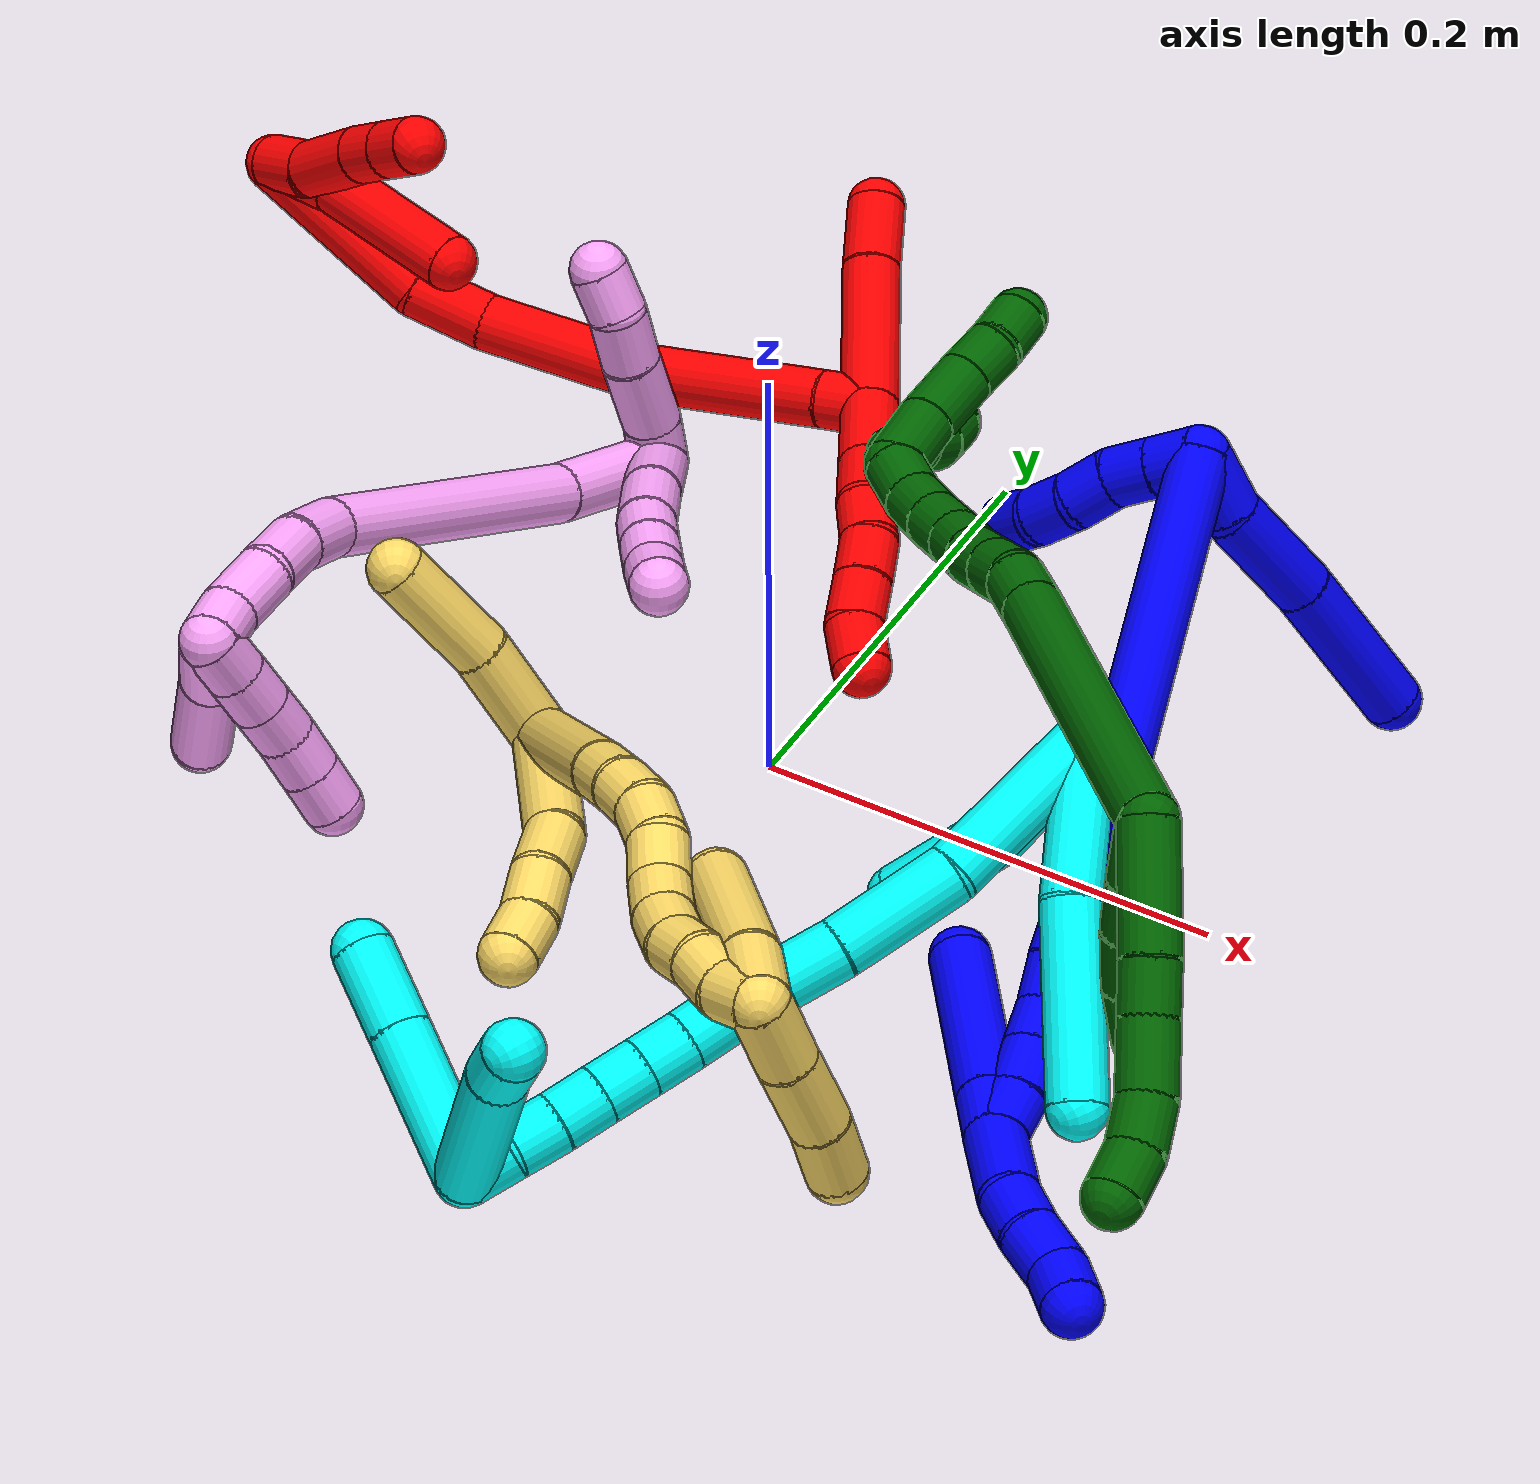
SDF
<sdf version="1.7">
 <world name="default">
  <plugin name="TubeGeneratorPlugin" filename="libtube_generator_plugin.so"/>
  <model name="photoneo_s_sensor">
   <static>1</static>
   <pose>0 0 2 1.57079 1.57079 3.14159</pose>
   <link name="link">
    <inertial><mass>0.1</mass></inertial>
    <sensor name="sensor" type="depth">
     <update_rate>30</update_rate>
     <camera>
      <horizontal_fov>1.22</horizontal_fov>
      <image><width>1920</width><height>1200</height><format>B8G8R8</format></image>
      <clip><near>0.1</near><far>4</far></clip>
      <depth_camera><output>points</output></depth_camera>
     </camera>
     <plugin name="camera_plugin" filename="libgazebo_ros_depth_camera.so">
      <baseline>0.2</baseline>
      <alwaysOn>1</alwaysOn>
      <updateRate>0.0</updateRate>
      <cameraName>camera_ir</cameraName>
      <imageTopicName>/camera/color/image_raw</imageTopicName>
      <cameraInfoTopicName>/camera/color/camera_info</cameraInfoTopicName>
      <depthImageTopicName>/camera/depth/image_raw</depthImageTopicName>
      <depthImageCameraInfoTopicName>/camera/depth/camera_info</depthImageCameraInfoTopicName>
      <pointCloudTopicName>/camera/depth/points</pointCloudTopicName>
      <frameName>fr_optical</frameName>
      <pointCloudCutoff>0.1</pointCloudCutoff>
      <pointCloudCutoffMax>2.0</pointCloudCutoffMax>
      <distortionK1>0</distortionK1>
      <distortionK2>0</distortionK2>
      <distortionK3>0</distortionK3>
      <distortionT1>0</distortionT1>
      <distortionT2>0</distortionT2>
      <CxPrime>0</CxPrime>
      <Cx>0</Cx>
      <Cy>0</Cy>
      <focalLength>0</focalLength>
      <hackBaseline>0</hackBaseline>
     </plugin>
    </sensor>
   </link>
  </model>
  <gravity>0 0 -9.8</gravity>
  <magnetic_field>6e-06 2.3e-05 -4.2e-05</magnetic_field>
  <atmosphere type="adiabatic"/>
  <physics name="default_physics" default="0" type="ode">
   <max_step_size>0.003</max_step_size>
   <real_time_factor>1</real_time_factor>
   <real_time_update_rate>1000</real_time_update_rate>
   <max_contacts>10000</max_contacts>
   <ode>
    <solver>
     <type>quick</type>
     <iters>100</iters>
     <sor>1.3</sor>
     <use_dynamic_moi_rescaling>0</use_dynamic_moi_rescaling>
    </solver>
    <constraints>
     <contact_max_correcting_vel>0</contact_max_correcting_vel>
     <contact_surface_layer>0.001</contact_surface_layer>
     <cfm>0</cfm>
     <erp>0.2</erp>
    </constraints>
   </ode>
  </physics>
  <scene><ambient>0.4 0.4 0.4 1</ambient><background>0.7 0.7 0.7 1</background><shadows>0</shadows></scene>
  <audio><device>default</device></audio>
  <spherical_coordinates>
   <surface_model>EARTH_WGS84</surface_model>
   <latitude_deg>0</latitude_deg>
   <longitude_deg>0</longitude_deg>
   <elevation>0</elevation>
   <heading_deg>0</heading_deg>
  </spherical_coordinates>
  <model name="bin">
   <static>1</static>
   <link name="bottom">
    <collision name="collision-bottom">
     <pose>0 0 -0.01 0 -0 0</pose>
     <geometry><box><size>0.8 0.6 0.02</size></box></geometry>
     <surface>
      <friction><ode><mu>100</mu><mu2>100</mu2></ode></friction>
      <contact><collide_bitmask>65535</collide_bitmask></contact>
     </surface>
    </collision>
   </link>
   <link name="west_wall">
    <collision name="collision-west_wall">
     <pose>-0.41 0 0.1 0 -0 0</pose>
     <geometry><box><size>0.02 0.6 0.2</size></box></geometry>
     <surface>
      <friction><ode><mu>100</mu><mu2>100</mu2></ode></friction>
      <contact><collide_bitmask>65535</collide_bitmask></contact>
     </surface>
    </collision>
   </link>
   <link name="east_wall">
    <collision name="collision-east_wall">
     <pose>0.41 0 0.1 0 -0 0</pose>
     <geometry><box><size>0.02 0.6 0.2</size></box></geometry>
     <surface>
      <friction><ode><mu>100</mu><mu2>100</mu2></ode></friction>
      <contact><collide_bitmask>65535</collide_bitmask></contact>
     </surface>
    </collision>
   </link>
   <link name="south_wall">
    <collision name="collision-south_wall">
     <pose>0 -0.31 0.1 0 -0 0</pose>
     <geometry><box><size>0.8 0.02 0.2</size></box></geometry>
     <surface>
      <friction><ode><mu>100</mu><mu2>100</mu2></ode></friction>
      <contact><collide_bitmask>65535</collide_bitmask></contact>
     </surface>
    </collision>
   </link>
   <link name="north_wall">
    <collision name="collision-north_wall">
     <pose>0 0.31 0.1 0 -0 0</pose>
     <geometry><box><size>0.8 0.02 0.2</size></box></geometry>
     <surface>
      <friction><ode><mu>100</mu><mu2>100</mu2></ode></friction>
      <contact><collide_bitmask>65535</collide_bitmask></contact>
     </surface>
    </collision>
   </link>
  </model>
  <model name="1">
   <static>0</static>
   <link name="1">
    <collision name="collision-cylinder-e_1_2_8">
     <pose>0.013261 -0.003113 0.002877 0.824707 1.26144 0.618354</pose>
     <geometry><cylinder><radius>0.0125</radius><length>0.027845</length></cylinder></geometry>
     <surface>
      <friction><ode><mu>1.16</mu><mu2>1.16</mu2><slip1>0</slip1><slip2>0</slip2></ode></friction>
      <contact><ode><kp>1e+06</kp><kd>1</kd><max_vel>0</max_vel><min_depth>0.001</min_depth></ode></contact>
     </surface>
    </collision>
    <visual name="visual-cylinder-e_1_2_8">
     <pose>0.013261 -0.003113 0.002877 0.824707 1.26144 0.618354</pose>
     <geometry><cylinder><radius>0.0125</radius><length>0.027845</length></cylinder></geometry>
     <material><ambient>0 0 1 1</ambient></material>
    </visual>
    <collision name="collision-cylinder-e_2_8_9">
     <pose>0.051782 -0.006153 0.006542 -0.09106 1.53947 -0.088254</pose>
     <geometry><cylinder><radius>0.0125</radius><length>0.050542</length></cylinder></geometry>
     <surface>
      <friction><ode><mu>1.16</mu><mu2>1.16</mu2><slip1>0</slip1><slip2>0</slip2></ode></friction>
      <contact><ode><kp>1e+06</kp><kd>1</kd><max_vel>0</max_vel><min_depth>0.001</min_depth></ode></contact>
     </surface>
    </collision>
    <visual name="visual-cylinder-e_2_8_9">
     <pose>0.051782 -0.006153 0.006542 -0.09106 1.53947 -0.088254</pose>
     <geometry><cylinder><radius>0.0125</radius><length>0.050542</length></cylinder></geometry>
     <material><ambient>0 0 1 1</ambient></material>
    </visual>
    <collision name="collision-cylinder-e_3_9_6">
     <pose>0.112717 -0.008671 0.008949 1.01225 1.48542 0.941441</pose>
     <geometry><cylinder><radius>0.0125</radius><length>0.071613</length></cylinder></geometry>
     <surface>
      <friction><ode><mu>1.16</mu><mu2>1.16</mu2><slip1>0</slip1><slip2>0</slip2></ode></friction>
      <contact><ode><kp>1e+06</kp><kd>1</kd><max_vel>0</max_vel><min_depth>0.001</min_depth></ode></contact>
     </surface>
    </collision>
    <visual name="visual-cylinder-e_3_9_6">
     <pose>0.112717 -0.008671 0.008949 1.01225 1.48542 0.941441</pose>
     <geometry><cylinder><radius>0.0125</radius><length>0.071613</length></cylinder></geometry>
     <material><ambient>0 0 1 1</ambient></material>
    </visual>
    <collision name="collision-cylinder-e_1_2_10">
     <pose>-0.000829 -0.00835 -0.00544 2.14825 -0.083003 -0.152934</pose>
     <geometry><cylinder><radius>0.0125</radius><length>0.02</length></cylinder></geometry>
     <surface>
      <friction><ode><mu>1.16</mu><mu2>1.16</mu2><slip1>0</slip1><slip2>0</slip2></ode></friction>
      <contact><ode><kp>1e+06</kp><kd>1</kd><max_vel>0</max_vel><min_depth>0.001</min_depth></ode></contact>
     </surface>
    </collision>
    <visual name="visual-cylinder-e_1_2_10">
     <pose>-0.000829 -0.00835 -0.00544 2.14825 -0.083003 -0.152934</pose>
     <geometry><cylinder><radius>0.0125</radius><length>0.02</length></cylinder></geometry>
     <material><ambient>0 0 1 1</ambient></material>
    </visual>
    <collision name="collision-cylinder-e_2_10_11">
     <pose>-0.002495 -0.024992 -0.016405 2.1585 -0.083751 -0.156207</pose>
     <geometry><cylinder><radius>0.0125</radius><length>0.02</length></cylinder></geometry>
     <surface>
      <friction><ode><mu>1.16</mu><mu2>1.16</mu2><slip1>0</slip1><slip2>0</slip2></ode></friction>
      <contact><ode><kp>1e+06</kp><kd>1</kd><max_vel>0</max_vel><min_depth>0.001</min_depth></ode></contact>
     </surface>
    </collision>
    <visual name="visual-cylinder-e_2_10_11">
     <pose>-0.002495 -0.024992 -0.016405 2.1585 -0.083751 -0.156207</pose>
     <geometry><cylinder><radius>0.0125</radius><length>0.02</length></cylinder></geometry>
     <material><ambient>0 0 1 1</ambient></material>
    </visual>
    <collision name="collision-cylinder-e_3_11_12">
     <pose>-0.002895 -0.042684 -0.025319 1.91683 0.043661 0.062144</pose>
     <geometry><cylinder><radius>0.0125</radius><length>0.02</length></cylinder></geometry>
     <surface>
      <friction><ode><mu>1.16</mu><mu2>1.16</mu2><slip1>0</slip1><slip2>0</slip2></ode></friction>
      <contact><ode><kp>1e+06</kp><kd>1</kd><max_vel>0</max_vel><min_depth>0.001</min_depth></ode></contact>
     </surface>
    </collision>
    <visual name="visual-cylinder-e_3_11_12">
     <pose>-0.002895 -0.042684 -0.025319 1.91683 0.043661 0.062144</pose>
     <geometry><cylinder><radius>0.0125</radius><length>0.02</length></cylinder></geometry>
     <material><ambient>0 0 1 1</ambient></material>
    </visual>
    <collision name="collision-cylinder-e_4_12_13">
     <pose>-0.001266 -0.060259 -0.034339 2.17392 0.119521 0.226738</pose>
     <geometry><cylinder><radius>0.0125</radius><length>0.02</length></cylinder></geometry>
     <surface>
      <friction><ode><mu>1.16</mu><mu2>1.16</mu2><slip1>0</slip1><slip2>0</slip2></ode></friction>
      <contact><ode><kp>1e+06</kp><kd>1</kd><max_vel>0</max_vel><min_depth>0.001</min_depth></ode></contact>
     </surface>
    </collision>
    <visual name="visual-cylinder-e_4_12_13">
     <pose>-0.001266 -0.060259 -0.034339 2.17392 0.119521 0.226738</pose>
     <geometry><cylinder><radius>0.0125</radius><length>0.02</length></cylinder></geometry>
     <material><ambient>0 0 1 1</ambient></material>
    </visual>
    <collision name="collision-cylinder-e_5_13_5">
     <pose>0.002262 -0.074625 -0.04747 2.4516 0.235685 0.636484</pose>
     <geometry><cylinder><radius>0.0125</radius><length>0.02</length></cylinder></geometry>
     <surface>
      <friction><ode><mu>1.16</mu><mu2>1.16</mu2><slip1>0</slip1><slip2>0</slip2></ode></friction>
      <contact><ode><kp>1e+06</kp><kd>1</kd><max_vel>0</max_vel><min_depth>0.001</min_depth></ode></contact>
     </surface>
    </collision>
    <visual name="visual-cylinder-e_5_13_5">
     <pose>0.002262 -0.074625 -0.04747 2.4516 0.235685 0.636484</pose>
     <geometry><cylinder><radius>0.0125</radius><length>0.02</length></cylinder></geometry>
     <material><ambient>0 0 1 1</ambient></material>
    </visual>
    <collision name="collision-cylinder-e_1_2_14">
     <pose>0.015512 -0.059479 0.052406 0.84853 0.193234 0.0875</pose>
     <geometry><cylinder><radius>0.0125</radius><length>0.161552</length></cylinder></geometry>
     <surface>
      <friction><ode><mu>1.16</mu><mu2>1.16</mu2><slip1>0</slip1><slip2>0</slip2></ode></friction>
      <contact><ode><kp>1e+06</kp><kd>1</kd><max_vel>0</max_vel><min_depth>0.001</min_depth></ode></contact>
     </surface>
    </collision>
    <visual name="visual-cylinder-e_1_2_14">
     <pose>0.015512 -0.059479 0.052406 0.84853 0.193234 0.0875</pose>
     <geometry><cylinder><radius>0.0125</radius><length>0.161552</length></cylinder></geometry>
     <material><ambient>0 0 1 1</ambient></material>
    </visual>
    <collision name="collision-cylinder-e_2_14_15">
     <pose>0.034984 -0.139911 0.122508 0.869474 0.143432 0.066695</pose>
     <geometry><cylinder><radius>0.0125</radius><length>0.055419</length></cylinder></geometry>
     <surface>
      <friction><ode><mu>1.16</mu><mu2>1.16</mu2><slip1>0</slip1><slip2>0</slip2></ode></friction>
      <contact><ode><kp>1e+06</kp><kd>1</kd><max_vel>0</max_vel><min_depth>0.001</min_depth></ode></contact>
     </surface>
    </collision>
    <visual name="visual-cylinder-e_2_14_15">
     <pose>0.034984 -0.139911 0.122508 0.869474 0.143432 0.066695</pose>
     <geometry><cylinder><radius>0.0125</radius><length>0.055419</length></cylinder></geometry>
     <material><ambient>0 0 1 1</ambient></material>
    </visual>
    <collision name="collision-cylinder-e_3_15_16">
     <pose>0.041139 -0.168295 0.146836 0.842132 0.216742 0.097373</pose>
     <geometry><cylinder><radius>0.0125</radius><length>0.020399</length></cylinder></geometry>
     <surface>
      <friction><ode><mu>1.16</mu><mu2>1.16</mu2><slip1>0</slip1><slip2>0</slip2></ode></friction>
      <contact><ode><kp>1e+06</kp><kd>1</kd><max_vel>0</max_vel><min_depth>0.001</min_depth></ode></contact>
     </surface>
    </collision>
    <visual name="visual-cylinder-e_3_15_16">
     <pose>0.041139 -0.168295 0.146836 0.842132 0.216742 0.097373</pose>
     <geometry><cylinder><radius>0.0125</radius><length>0.020399</length></cylinder></geometry>
     <material><ambient>0 0 1 1</ambient></material>
    </visual>
    <collision name="collision-cylinder-e_4_16_17">
     <pose>0.042715 -0.182274 0.161284 0.697366 -0.060461 -0.021986</pose>
     <geometry><cylinder><radius>0.0125</radius><length>0.020429</length></cylinder></geometry>
     <surface>
      <friction><ode><mu>1.16</mu><mu2>1.16</mu2><slip1>0</slip1><slip2>0</slip2></ode></friction>
      <contact><ode><kp>1e+06</kp><kd>1</kd><max_vel>0</max_vel><min_depth>0.001</min_depth></ode></contact>
     </surface>
    </collision>
    <visual name="visual-cylinder-e_4_16_17">
     <pose>0.042715 -0.182274 0.161284 0.697366 -0.060461 -0.021986</pose>
     <geometry><cylinder><radius>0.0125</radius><length>0.020429</length></cylinder></geometry>
     <material><ambient>0 0 1 1</ambient></material>
    </visual>
    <collision name="collision-cylinder-e_5_17_18">
     <pose>0.041174 -0.195551 0.177495 0.675667 -0.085612 -0.030092</pose>
     <geometry><cylinder><radius>0.0125</radius><length>0.021599</length></cylinder></geometry>
     <surface>
      <friction><ode><mu>1.16</mu><mu2>1.16</mu2><slip1>0</slip1><slip2>0</slip2></ode></friction>
      <contact><ode><kp>1e+06</kp><kd>1</kd><max_vel>0</max_vel><min_depth>0.001</min_depth></ode></contact>
     </surface>
    </collision>
    <visual name="visual-cylinder-e_5_17_18">
     <pose>0.041174 -0.195551 0.177495 0.675667 -0.085612 -0.030092</pose>
     <geometry><cylinder><radius>0.0125</radius><length>0.021599</length></cylinder></geometry>
     <material><ambient>0 0 1 1</ambient></material>
    </visual>
    <collision name="collision-cylinder-e_6_18_1">
     <pose>0.038522 -0.209396 0.193136 0.776357 -0.168634 -0.069095</pose>
     <geometry><cylinder><radius>0.0125</radius><length>0.020601</length></cylinder></geometry>
     <surface>
      <friction><ode><mu>1.16</mu><mu2>1.16</mu2><slip1>0</slip1><slip2>0</slip2></ode></friction>
      <contact><ode><kp>1e+06</kp><kd>1</kd><max_vel>0</max_vel><min_depth>0.001</min_depth></ode></contact>
     </surface>
    </collision>
    <visual name="visual-cylinder-e_6_18_1">
     <pose>0.038522 -0.209396 0.193136 0.776357 -0.168634 -0.069095</pose>
     <geometry><cylinder><radius>0.0125</radius><length>0.020601</length></cylinder></geometry>
     <material><ambient>0 0 1 1</ambient></material>
    </visual>
    <collision name="collision-cylinder-e_1_1_19">
     <pose>0.036603 -0.214112 0.190104 -2.91226 -0.017981 0.155813</pose>
     <geometry><cylinder><radius>0.0125</radius><length>0.02111</length></cylinder></geometry>
     <surface>
      <friction><ode><mu>1.16</mu><mu2>1.16</mu2><slip1>0</slip1><slip2>0</slip2></ode></friction>
      <contact><ode><kp>1e+06</kp><kd>1</kd><max_vel>0</max_vel><min_depth>0.001</min_depth></ode></contact>
     </surface>
    </collision>
    <visual name="visual-cylinder-e_1_1_19">
     <pose>0.036603 -0.214112 0.190104 -2.91226 -0.017981 0.155813</pose>
     <geometry><cylinder><radius>0.0125</radius><length>0.02111</length></cylinder></geometry>
     <material><ambient>0 0 1 1</ambient></material>
    </visual>
    <collision name="collision-cylinder-e_2_19_4">
     <pose>0.036031 -0.202897 0.141382 -2.91617 -0.009689 0.08555</pose>
     <geometry><cylinder><radius>0.0125</radius><length>0.07889</length></cylinder></geometry>
     <surface>
      <friction><ode><mu>1.16</mu><mu2>1.16</mu2><slip1>0</slip1><slip2>0</slip2></ode></friction>
      <contact><ode><kp>1e+06</kp><kd>1</kd><max_vel>0</max_vel><min_depth>0.001</min_depth></ode></contact>
     </surface>
    </collision>
    <visual name="visual-cylinder-e_2_19_4">
     <pose>0.036031 -0.202897 0.141382 -2.91617 -0.009689 0.08555</pose>
     <geometry><cylinder><radius>0.0125</radius><length>0.07889</length></cylinder></geometry>
     <material><ambient>0 0 1 1</ambient></material>
    </visual>
    <collision name="collision-cylinder-e_1_1_20">
     <pose>0.035162 -0.219349 0.219166 0.149931 -0.08565 -0.006437</pose>
     <geometry><cylinder><radius>0.0125</radius><length>0.038136</length></cylinder></geometry>
     <surface>
      <friction><ode><mu>1.16</mu><mu2>1.16</mu2><slip1>0</slip1><slip2>0</slip2></ode></friction>
      <contact><ode><kp>1e+06</kp><kd>1</kd><max_vel>0</max_vel><min_depth>0.001</min_depth></ode></contact>
     </surface>
    </collision>
    <visual name="visual-cylinder-e_1_1_20">
     <pose>0.035162 -0.219349 0.219166 0.149931 -0.08565 -0.006437</pose>
     <geometry><cylinder><radius>0.0125</radius><length>0.038136</length></cylinder></geometry>
     <material><ambient>0 0 1 1</ambient></material>
    </visual>
    <collision name="collision-cylinder-e_2_20_21">
     <pose>0.034996 -0.222496 0.247913 0.031114 0.146009 0.002276</pose>
     <geometry><cylinder><radius>0.0125</radius><length>0.020148</length></cylinder></geometry>
     <surface>
      <friction><ode><mu>1.16</mu><mu2>1.16</mu2><slip1>0</slip1><slip2>0</slip2></ode></friction>
      <contact><ode><kp>1e+06</kp><kd>1</kd><max_vel>0</max_vel><min_depth>0.001</min_depth></ode></contact>
     </surface>
    </collision>
    <visual name="visual-cylinder-e_2_20_21">
     <pose>0.034996 -0.222496 0.247913 0.031114 0.146009 0.002276</pose>
     <geometry><cylinder><radius>0.0125</radius><length>0.020148</length></cylinder></geometry>
     <material><ambient>0 0 1 1</ambient></material>
    </visual>
    <collision name="collision-cylinder-e_3_21_22">
     <pose>0.039646 -0.222348 0.268209 -0.044325 0.298632 -0.006669</pose>
     <geometry><cylinder><radius>0.0125</radius><length>0.021647</length></cylinder></geometry>
     <surface>
      <friction><ode><mu>1.16</mu><mu2>1.16</mu2><slip1>0</slip1><slip2>0</slip2></ode></friction>
      <contact><ode><kp>1e+06</kp><kd>1</kd><max_vel>0</max_vel><min_depth>0.001</min_depth></ode></contact>
     </surface>
    </collision>
    <visual name="visual-cylinder-e_3_21_22">
     <pose>0.039646 -0.222348 0.268209 -0.044325 0.298632 -0.006669</pose>
     <geometry><cylinder><radius>0.0125</radius><length>0.021647</length></cylinder></geometry>
     <material><ambient>0 0 1 1</ambient></material>
    </visual>
    <collision name="collision-cylinder-e_4_22_3">
     <pose>0.042789 -0.222651 0.288549 0.075906 -0.004134 -0.000157</pose>
     <geometry><cylinder><radius>0.0125</radius><length>0.020069</length></cylinder></geometry>
     <surface>
      <friction><ode><mu>1.16</mu><mu2>1.16</mu2><slip1>0</slip1><slip2>0</slip2></ode></friction>
      <contact><ode><kp>1e+06</kp><kd>1</kd><max_vel>0</max_vel><min_depth>0.001</min_depth></ode></contact>
     </surface>
    </collision>
    <visual name="visual-cylinder-e_4_22_3">
     <pose>0.042789 -0.222651 0.288549 0.075906 -0.004134 -0.000157</pose>
     <geometry><cylinder><radius>0.0125</radius><length>0.020069</length></cylinder></geometry>
     <material><ambient>0 0 1 1</ambient></material>
    </visual>
    <collision name="collision-sphere-3">
     <pose>0.042748 -0.223412 0.298555 0 -0 0</pose>
     <geometry><sphere><radius>0.0125</radius></sphere></geometry>
     <surface>
      <friction><ode><mu>1.16</mu><mu2>1.16</mu2><slip1>0</slip1><slip2>0</slip2></ode></friction>
      <contact><ode><kp>1e+06</kp><kd>1</kd><max_vel>0</max_vel><min_depth>0.001</min_depth></ode></contact>
     </surface>
    </collision>
    <visual name="visual-sphere-3">
     <pose>0.042748 -0.223412 0.298555 0 -0 0</pose>
     <geometry><sphere><radius>0.0125</radius></sphere></geometry>
     <material><ambient>0 0 1 1</ambient></material>
    </visual>
    <collision name="collision-sphere-22">
     <pose>0.042831 -0.22189 0.278544 0 -0 0</pose>
     <geometry><sphere><radius>0.0125</radius></sphere></geometry>
     <surface>
      <friction><ode><mu>1.16</mu><mu2>1.16</mu2><slip1>0</slip1><slip2>0</slip2></ode></friction>
      <contact><ode><kp>1e+06</kp><kd>1</kd><max_vel>0</max_vel><min_depth>0.001</min_depth></ode></contact>
     </surface>
    </collision>
    <visual name="visual-sphere-22">
     <pose>0.042831 -0.22189 0.278544 0 -0 0</pose>
     <geometry><sphere><radius>0.0125</radius></sphere></geometry>
     <material><ambient>0 0 1 1</ambient></material>
    </visual>
    <collision name="collision-sphere-21">
     <pose>0.036462 -0.222806 0.257875 0 -0 0</pose>
     <geometry><sphere><radius>0.0125</radius></sphere></geometry>
     <surface>
      <friction><ode><mu>1.16</mu><mu2>1.16</mu2><slip1>0</slip1><slip2>0</slip2></ode></friction>
      <contact><ode><kp>1e+06</kp><kd>1</kd><max_vel>0</max_vel><min_depth>0.001</min_depth></ode></contact>
     </surface>
    </collision>
    <visual name="visual-sphere-21">
     <pose>0.036462 -0.222806 0.257875 0 -0 0</pose>
     <geometry><sphere><radius>0.0125</radius></sphere></geometry>
     <material><ambient>0 0 1 1</ambient></material>
    </visual>
    <collision name="collision-sphere-20">
     <pose>0.033531 -0.222186 0.237951 0 -0 0</pose>
     <geometry><sphere><radius>0.0125</radius></sphere></geometry>
     <surface>
      <friction><ode><mu>1.16</mu><mu2>1.16</mu2><slip1>0</slip1><slip2>0</slip2></ode></friction>
      <contact><ode><kp>1e+06</kp><kd>1</kd><max_vel>0</max_vel><min_depth>0.001</min_depth></ode></contact>
     </surface>
    </collision>
    <visual name="visual-sphere-20">
     <pose>0.033531 -0.222186 0.237951 0 -0 0</pose>
     <geometry><sphere><radius>0.0125</radius></sphere></geometry>
     <material><ambient>0 0 1 1</ambient></material>
    </visual>
    <collision name="collision-sphere-4">
     <pose>0.035649 -0.19408 0.102937 0 -0 0</pose>
     <geometry><sphere><radius>0.0125</radius></sphere></geometry>
     <surface>
      <friction><ode><mu>1.16</mu><mu2>1.16</mu2><slip1>0</slip1><slip2>0</slip2></ode></friction>
      <contact><ode><kp>1e+06</kp><kd>1</kd><max_vel>0</max_vel><min_depth>0.001</min_depth></ode></contact>
     </surface>
    </collision>
    <visual name="visual-sphere-4">
     <pose>0.035649 -0.19408 0.102937 0 -0 0</pose>
     <geometry><sphere><radius>0.0125</radius></sphere></geometry>
     <material><ambient>0 0 1 1</ambient></material>
    </visual>
    <collision name="collision-sphere-11">
     <pose>-0.003331 -0.033285 -0.02193 0 -0 0</pose>
     <geometry><sphere><radius>0.0125</radius></sphere></geometry>
     <surface>
      <friction><ode><mu>1.16</mu><mu2>1.16</mu2><slip1>0</slip1><slip2>0</slip2></ode></friction>
      <contact><ode><kp>1e+06</kp><kd>1</kd><max_vel>0</max_vel><min_depth>0.001</min_depth></ode></contact>
     </surface>
    </collision>
    <visual name="visual-sphere-11">
     <pose>-0.003331 -0.033285 -0.02193 0 -0 0</pose>
     <geometry><sphere><radius>0.0125</radius></sphere></geometry>
     <material><ambient>0 0 1 1</ambient></material>
    </visual>
    <collision name="collision-sphere-10">
     <pose>-0.001658 -0.016699 -0.01088 0 -0 0</pose>
     <geometry><sphere><radius>0.0125</radius></sphere></geometry>
     <surface>
      <friction><ode><mu>1.16</mu><mu2>1.16</mu2><slip1>0</slip1><slip2>0</slip2></ode></friction>
      <contact><ode><kp>1e+06</kp><kd>1</kd><max_vel>0</max_vel><min_depth>0.001</min_depth></ode></contact>
     </surface>
    </collision>
    <visual name="visual-sphere-10">
     <pose>-0.001658 -0.016699 -0.01088 0 -0 0</pose>
     <geometry><sphere><radius>0.0125</radius></sphere></geometry>
     <material><ambient>0 0 1 1</ambient></material>
    </visual>
    <collision name="collision-sphere-6">
     <pose>0.148393 -0.01126 0.010567 0 -0 0</pose>
     <geometry><sphere><radius>0.0125</radius></sphere></geometry>
     <surface>
      <friction><ode><mu>1.16</mu><mu2>1.16</mu2><slip1>0</slip1><slip2>0</slip2></ode></friction>
      <contact><ode><kp>1e+06</kp><kd>1</kd><max_vel>0</max_vel><min_depth>0.001</min_depth></ode></contact>
     </surface>
    </collision>
    <visual name="visual-sphere-6">
     <pose>0.148393 -0.01126 0.010567 0 -0 0</pose>
     <geometry><sphere><radius>0.0125</radius></sphere></geometry>
     <material><ambient>0 0 1 1</ambient></material>
    </visual>
    <collision name="collision-sphere-9">
     <pose>0.07704 -0.006081 0.007331 0 -0 0</pose>
     <geometry><sphere><radius>0.0125</radius></sphere></geometry>
     <surface>
      <friction><ode><mu>1.16</mu><mu2>1.16</mu2><slip1>0</slip1><slip2>0</slip2></ode></friction>
      <contact><ode><kp>1e+06</kp><kd>1</kd><max_vel>0</max_vel><min_depth>0.001</min_depth></ode></contact>
     </surface>
    </collision>
    <visual name="visual-sphere-9">
     <pose>0.07704 -0.006081 0.007331 0 -0 0</pose>
     <geometry><sphere><radius>0.0125</radius></sphere></geometry>
     <material><ambient>0 0 1 1</ambient></material>
    </visual>
    <collision name="collision-sphere-2">
     <geometry><sphere><radius>0.0125</radius></sphere></geometry>
     <surface>
      <friction><ode><mu>1.16</mu><mu2>1.16</mu2><slip1>0</slip1><slip2>0</slip2></ode></friction>
      <contact><ode><kp>1e+06</kp><kd>1</kd><max_vel>0</max_vel><min_depth>0.001</min_depth></ode></contact>
     </surface>
    </collision>
    <visual name="visual-sphere-2">
     <geometry><sphere><radius>0.0125</radius></sphere></geometry>
     <material><ambient>0 0 1 1</ambient></material>
    </visual>
    <collision name="collision-sphere-19">
     <pose>0.036413 -0.211713 0.179827 0 -0 0</pose>
     <geometry><sphere><radius>0.0125</radius></sphere></geometry>
     <surface>
      <friction><ode><mu>1.16</mu><mu2>1.16</mu2><slip1>0</slip1><slip2>0</slip2></ode></friction>
      <contact><ode><kp>1e+06</kp><kd>1</kd><max_vel>0</max_vel><min_depth>0.001</min_depth></ode></contact>
     </surface>
    </collision>
    <visual name="visual-sphere-19">
     <pose>0.036413 -0.211713 0.179827 0 -0 0</pose>
     <geometry><sphere><radius>0.0125</radius></sphere></geometry>
     <material><ambient>0 0 1 1</ambient></material>
    </visual>
    <collision name="collision-sphere-8">
     <pose>0.026523 -0.006225 0.005754 0 -0 0</pose>
     <geometry><sphere><radius>0.0125</radius></sphere></geometry>
     <surface>
      <friction><ode><mu>1.16</mu><mu2>1.16</mu2><slip1>0</slip1><slip2>0</slip2></ode></friction>
      <contact><ode><kp>1e+06</kp><kd>1</kd><max_vel>0</max_vel><min_depth>0.001</min_depth></ode></contact>
     </surface>
    </collision>
    <visual name="visual-sphere-8">
     <pose>0.026523 -0.006225 0.005754 0 -0 0</pose>
     <geometry><sphere><radius>0.0125</radius></sphere></geometry>
     <material><ambient>0 0 1 1</ambient></material>
    </visual>
    <collision name="collision-sphere-12">
     <pose>-0.002458 -0.052082 -0.028707 0 -0 0</pose>
     <geometry><sphere><radius>0.0125</radius></sphere></geometry>
     <surface>
      <friction><ode><mu>1.16</mu><mu2>1.16</mu2><slip1>0</slip1><slip2>0</slip2></ode></friction>
      <contact><ode><kp>1e+06</kp><kd>1</kd><max_vel>0</max_vel><min_depth>0.001</min_depth></ode></contact>
     </surface>
    </collision>
    <visual name="visual-sphere-12">
     <pose>-0.002458 -0.052082 -0.028707 0 -0 0</pose>
     <geometry><sphere><radius>0.0125</radius></sphere></geometry>
     <material><ambient>0 0 1 1</ambient></material>
    </visual>
    <collision name="collision-sphere-13">
     <pose>-7.4e-05 -0.068436 -0.039971 0 -0 0</pose>
     <geometry><sphere><radius>0.0125</radius></sphere></geometry>
     <surface>
      <friction><ode><mu>1.16</mu><mu2>1.16</mu2><slip1>0</slip1><slip2>0</slip2></ode></friction>
      <contact><ode><kp>1e+06</kp><kd>1</kd><max_vel>0</max_vel><min_depth>0.001</min_depth></ode></contact>
     </surface>
    </collision>
    <visual name="visual-sphere-13">
     <pose>-7.4e-05 -0.068436 -0.039971 0 -0 0</pose>
     <geometry><sphere><radius>0.0125</radius></sphere></geometry>
     <material><ambient>0 0 1 1</ambient></material>
    </visual>
    <collision name="collision-sphere-5">
     <pose>0.004597 -0.080815 -0.054969 0 -0 0</pose>
     <geometry><sphere><radius>0.0125</radius></sphere></geometry>
     <surface>
      <friction><ode><mu>1.16</mu><mu2>1.16</mu2><slip1>0</slip1><slip2>0</slip2></ode></friction>
      <contact><ode><kp>1e+06</kp><kd>1</kd><max_vel>0</max_vel><min_depth>0.001</min_depth></ode></contact>
     </surface>
    </collision>
    <visual name="visual-sphere-5">
     <pose>0.004597 -0.080815 -0.054969 0 -0 0</pose>
     <geometry><sphere><radius>0.0125</radius></sphere></geometry>
     <material><ambient>0 0 1 1</ambient></material>
    </visual>
    <collision name="collision-sphere-14">
     <pose>0.031023 -0.118958 0.104812 0 -0 0</pose>
     <geometry><sphere><radius>0.0125</radius></sphere></geometry>
     <surface>
      <friction><ode><mu>1.16</mu><mu2>1.16</mu2><slip1>0</slip1><slip2>0</slip2></ode></friction>
      <contact><ode><kp>1e+06</kp><kd>1</kd><max_vel>0</max_vel><min_depth>0.001</min_depth></ode></contact>
     </surface>
    </collision>
    <visual name="visual-sphere-14">
     <pose>0.031023 -0.118958 0.104812 0 -0 0</pose>
     <geometry><sphere><radius>0.0125</radius></sphere></geometry>
     <material><ambient>0 0 1 1</ambient></material>
    </visual>
    <collision name="collision-sphere-15">
     <pose>0.038945 -0.160863 0.140203 0 -0 0</pose>
     <geometry><sphere><radius>0.0125</radius></sphere></geometry>
     <surface>
      <friction><ode><mu>1.16</mu><mu2>1.16</mu2><slip1>0</slip1><slip2>0</slip2></ode></friction>
      <contact><ode><kp>1e+06</kp><kd>1</kd><max_vel>0</max_vel><min_depth>0.001</min_depth></ode></contact>
     </surface>
    </collision>
    <visual name="visual-sphere-15">
     <pose>0.038945 -0.160863 0.140203 0 -0 0</pose>
     <geometry><sphere><radius>0.0125</radius></sphere></geometry>
     <material><ambient>0 0 1 1</ambient></material>
    </visual>
    <collision name="collision-sphere-16">
     <pose>0.043332 -0.175726 0.153469 0 -0 0</pose>
     <geometry><sphere><radius>0.0125</radius></sphere></geometry>
     <surface>
      <friction><ode><mu>1.16</mu><mu2>1.16</mu2><slip1>0</slip1><slip2>0</slip2></ode></friction>
      <contact><ode><kp>1e+06</kp><kd>1</kd><max_vel>0</max_vel><min_depth>0.001</min_depth></ode></contact>
     </surface>
    </collision>
    <visual name="visual-sphere-16">
     <pose>0.043332 -0.175726 0.153469 0 -0 0</pose>
     <geometry><sphere><radius>0.0125</radius></sphere></geometry>
     <material><ambient>0 0 1 1</ambient></material>
    </visual>
    <collision name="collision-sphere-17">
     <pose>0.042098 -0.188822 0.169099 0 -0 0</pose>
     <geometry><sphere><radius>0.0125</radius></sphere></geometry>
     <surface>
      <friction><ode><mu>1.16</mu><mu2>1.16</mu2><slip1>0</slip1><slip2>0</slip2></ode></friction>
      <contact><ode><kp>1e+06</kp><kd>1</kd><max_vel>0</max_vel><min_depth>0.001</min_depth></ode></contact>
     </surface>
    </collision>
    <visual name="visual-sphere-17">
     <pose>0.042098 -0.188822 0.169099 0 -0 0</pose>
     <geometry><sphere><radius>0.0125</radius></sphere></geometry>
     <material><ambient>0 0 1 1</ambient></material>
    </visual>
    <collision name="collision-sphere-18">
     <pose>0.040251 -0.202281 0.185891 0 -0 0</pose>
     <geometry><sphere><radius>0.0125</radius></sphere></geometry>
     <surface>
      <friction><ode><mu>1.16</mu><mu2>1.16</mu2><slip1>0</slip1><slip2>0</slip2></ode></friction>
      <contact><ode><kp>1e+06</kp><kd>1</kd><max_vel>0</max_vel><min_depth>0.001</min_depth></ode></contact>
     </surface>
    </collision>
    <visual name="visual-sphere-18">
     <pose>0.040251 -0.202281 0.185891 0 -0 0</pose>
     <geometry><sphere><radius>0.0125</radius></sphere></geometry>
     <material><ambient>0 0 1 1</ambient></material>
    </visual>
    <collision name="collision-sphere-1">
     <pose>0.036793 -0.216511 0.200381 0 -0 0</pose>
     <geometry><sphere><radius>0.0125</radius></sphere></geometry>
     <surface>
      <friction><ode><mu>1.16</mu><mu2>1.16</mu2><slip1>0</slip1><slip2>0</slip2></ode></friction>
      <contact><ode><kp>1e+06</kp><kd>1</kd><max_vel>0</max_vel><min_depth>0.001</min_depth></ode></contact>
     </surface>
    </collision>
    <visual name="visual-sphere-1">
     <pose>0.036793 -0.216511 0.200381 0 -0 0</pose>
     <geometry><sphere><radius>0.0125</radius></sphere></geometry>
     <material><ambient>0 0 1 1</ambient></material>
    </visual>
    <inertial>
     <pose>0.034896 -0.107933 0.090596 0 -0 0</pose>
     <mass>0.75</mass>
     <inertia>
      <ixx>0.000492</ixx>
      <ixy>0</ixy>
      <ixz>0</ixz>
      <iyy>0.000283</iyy>
      <iyz>0</iyz>
      <izz>0.000172</izz>
     </inertia>
    </inertial>
   </link>
   <pose>0.132482 0.112761 0.137069 1.32882 0.93811 0.617984</pose>
  </model>
  <model name="2">
   <static>0</static>
   <link name="2">
    <collision name="collision-cylinder-e_1_2_8">
     <pose>-0.006139 0.004583 -0.018216 -2.89512 -0.31589 1.81962</pose>
     <geometry><cylinder><radius>0.0125</radius><length>0.039522</length></cylinder></geometry>
     <surface>
      <friction><ode><mu>1.16</mu><mu2>1.16</mu2><slip1>0</slip1><slip2>0</slip2></ode></friction>
      <contact><ode><kp>1e+06</kp><kd>1</kd><max_vel>0</max_vel><min_depth>0.001</min_depth></ode></contact>
     </surface>
    </collision>
    <visual name="visual-cylinder-e_1_2_8">
     <pose>-0.006139 0.004583 -0.018216 -2.89512 -0.31589 1.81962</pose>
     <geometry><cylinder><radius>0.0125</radius><length>0.039522</length></cylinder></geometry>
     <material><ambient>1 0 0 1</ambient></material>
    </visual>
    <collision name="collision-cylinder-e_2_8_9">
     <pose>-0.01734 0.011184 -0.048871 -2.98071 -0.381958 2.35147</pose>
     <geometry><cylinder><radius>0.0125</radius><length>0.027163</length></cylinder></geometry>
     <surface>
      <friction><ode><mu>1.16</mu><mu2>1.16</mu2><slip1>0</slip1><slip2>0</slip2></ode></friction>
      <contact><ode><kp>1e+06</kp><kd>1</kd><max_vel>0</max_vel><min_depth>0.001</min_depth></ode></contact>
     </surface>
    </collision>
    <visual name="visual-cylinder-e_2_8_9">
     <pose>-0.01734 0.011184 -0.048871 -2.98071 -0.381958 2.35147</pose>
     <geometry><cylinder><radius>0.0125</radius><length>0.027163</length></cylinder></geometry>
     <material><ambient>1 0 0 1</ambient></material>
    </visual>
    <collision name="collision-cylinder-e_3_9_10">
     <pose>-0.024109 0.015788 -0.071044 -2.88204 -0.167821 1.14495</pose>
     <geometry><cylinder><radius>0.0125</radius><length>0.020426</length></cylinder></geometry>
     <surface>
      <friction><ode><mu>1.16</mu><mu2>1.16</mu2><slip1>0</slip1><slip2>0</slip2></ode></friction>
      <contact><ode><kp>1e+06</kp><kd>1</kd><max_vel>0</max_vel><min_depth>0.001</min_depth></ode></contact>
     </surface>
    </collision>
    <visual name="visual-cylinder-e_3_9_10">
     <pose>-0.024109 0.015788 -0.071044 -2.88204 -0.167821 1.14495</pose>
     <geometry><cylinder><radius>0.0125</radius><length>0.020426</length></cylinder></geometry>
     <material><ambient>1 0 0 1</ambient></material>
    </visual>
    <collision name="collision-cylinder-e_4_10_11">
     <pose>-0.028305 0.023386 -0.089693 -2.62938 -0.238748 0.859065</pose>
     <geometry><cylinder><radius>0.0125</radius><length>0.021058</length></cylinder></geometry>
     <surface>
      <friction><ode><mu>1.16</mu><mu2>1.16</mu2><slip1>0</slip1><slip2>0</slip2></ode></friction>
      <contact><ode><kp>1e+06</kp><kd>1</kd><max_vel>0</max_vel><min_depth>0.001</min_depth></ode></contact>
     </surface>
    </collision>
    <visual name="visual-cylinder-e_4_10_11">
     <pose>-0.028305 0.023386 -0.089693 -2.62938 -0.238748 0.859065</pose>
     <geometry><cylinder><radius>0.0125</radius><length>0.021058</length></cylinder></geometry>
     <material><ambient>1 0 0 1</ambient></material>
    </visual>
    <collision name="collision-cylinder-e_5_11_12">
     <pose>-0.033191 0.033938 -0.107368 -2.57771 -0.22729 0.750711</pose>
     <geometry><cylinder><radius>0.0125</radius><length>0.02127</length></cylinder></geometry>
     <surface>
      <friction><ode><mu>1.16</mu><mu2>1.16</mu2><slip1>0</slip1><slip2>0</slip2></ode></friction>
      <contact><ode><kp>1e+06</kp><kd>1</kd><max_vel>0</max_vel><min_depth>0.001</min_depth></ode></contact>
     </surface>
    </collision>
    <visual name="visual-cylinder-e_5_11_12">
     <pose>-0.033191 0.033938 -0.107368 -2.57771 -0.22729 0.750711</pose>
     <geometry><cylinder><radius>0.0125</radius><length>0.02127</length></cylinder></geometry>
     <material><ambient>1 0 0 1</ambient></material>
    </visual>
    <collision name="collision-cylinder-e_6_12_6">
     <pose>-0.035614 0.042862 -0.125832 -2.80595 -0.002583 0.015249</pose>
     <geometry><cylinder><radius>0.0125</radius><length>0.020561</length></cylinder></geometry>
     <surface>
      <friction><ode><mu>1.16</mu><mu2>1.16</mu2><slip1>0</slip1><slip2>0</slip2></ode></friction>
      <contact><ode><kp>1e+06</kp><kd>1</kd><max_vel>0</max_vel><min_depth>0.001</min_depth></ode></contact>
     </surface>
    </collision>
    <visual name="visual-cylinder-e_6_12_6">
     <pose>-0.035614 0.042862 -0.125832 -2.80595 -0.002583 0.015249</pose>
     <geometry><cylinder><radius>0.0125</radius><length>0.020561</length></cylinder></geometry>
     <material><ambient>1 0 0 1</ambient></material>
    </visual>
    <collision name="collision-cylinder-e_1_2_13">
     <pose>0.002562 -0.016148 0.029687 0.498183 0.075655 0.019253</pose>
     <geometry><cylinder><radius>0.0125</radius><length>0.067784</length></cylinder></geometry>
     <surface>
      <friction><ode><mu>1.16</mu><mu2>1.16</mu2><slip1>0</slip1><slip2>0</slip2></ode></friction>
      <contact><ode><kp>1e+06</kp><kd>1</kd><max_vel>0</max_vel><min_depth>0.001</min_depth></ode></contact>
     </surface>
    </collision>
    <visual name="visual-cylinder-e_1_2_13">
     <pose>0.002562 -0.016148 0.029687 0.498183 0.075655 0.019253</pose>
     <geometry><cylinder><radius>0.0125</radius><length>0.067784</length></cylinder></geometry>
     <material><ambient>1 0 0 1</ambient></material>
    </visual>
    <collision name="collision-cylinder-e_2_13_5">
     <pose>0.007592 -0.039866 0.073377 0.495562 0.153854 0.038994</pose>
     <geometry><cylinder><radius>0.0125</radius><length>0.032216</length></cylinder></geometry>
     <surface>
      <friction><ode><mu>1.16</mu><mu2>1.16</mu2><slip1>0</slip1><slip2>0</slip2></ode></friction>
      <contact><ode><kp>1e+06</kp><kd>1</kd><max_vel>0</max_vel><min_depth>0.001</min_depth></ode></contact>
     </surface>
    </collision>
    <visual name="visual-cylinder-e_2_13_5">
     <pose>0.007592 -0.039866 0.073377 0.495562 0.153854 0.038994</pose>
     <geometry><cylinder><radius>0.0125</radius><length>0.032216</length></cylinder></geometry>
     <material><ambient>1 0 0 1</ambient></material>
    </visual>
    <collision name="collision-cylinder-e_1_2_14">
     <pose>-0.005236 0.005671 0.007046 -0.677743 -0.524761 0.188764</pose>
     <geometry><cylinder><radius>0.0125</radius><length>0.020901</length></cylinder></geometry>
     <surface>
      <friction><ode><mu>1.16</mu><mu2>1.16</mu2><slip1>0</slip1><slip2>0</slip2></ode></friction>
      <contact><ode><kp>1e+06</kp><kd>1</kd><max_vel>0</max_vel><min_depth>0.001</min_depth></ode></contact>
     </surface>
    </collision>
    <visual name="visual-cylinder-e_1_2_14">
     <pose>-0.005236 0.005671 0.007046 -0.677743 -0.524761 0.188764</pose>
     <geometry><cylinder><radius>0.0125</radius><length>0.020901</length></cylinder></geometry>
     <material><ambient>1 0 0 1</ambient></material>
    </visual>
    <collision name="collision-cylinder-e_2_14_15">
     <pose>-0.028921 0.036188 0.045381 -0.671089 -0.432596 0.152958</pose>
     <geometry><cylinder><radius>0.0125</radius><length>0.088016</length></cylinder></geometry>
     <surface>
      <friction><ode><mu>1.16</mu><mu2>1.16</mu2><slip1>0</slip1><slip2>0</slip2></ode></friction>
      <contact><ode><kp>1e+06</kp><kd>1</kd><max_vel>0</max_vel><min_depth>0.001</min_depth></ode></contact>
     </surface>
    </collision>
    <visual name="visual-cylinder-e_2_14_15">
     <pose>-0.028921 0.036188 0.045381 -0.671089 -0.432596 0.152958</pose>
     <geometry><cylinder><radius>0.0125</radius><length>0.088016</length></cylinder></geometry>
     <material><ambient>1 0 0 1</ambient></material>
    </visual>
    <collision name="collision-cylinder-e_3_15_16">
     <pose>-0.067534 0.076394 0.103934 -0.513107 -0.572382 0.154088</pose>
     <geometry><cylinder><radius>0.0125</radius><length>0.074452</length></cylinder></geometry>
     <surface>
      <friction><ode><mu>1.16</mu><mu2>1.16</mu2><slip1>0</slip1><slip2>0</slip2></ode></friction>
      <contact><ode><kp>1e+06</kp><kd>1</kd><max_vel>0</max_vel><min_depth>0.001</min_depth></ode></contact>
     </surface>
    </collision>
    <visual name="visual-cylinder-e_3_15_16">
     <pose>-0.067534 0.076394 0.103934 -0.513107 -0.572382 0.154088</pose>
     <geometry><cylinder><radius>0.0125</radius><length>0.074452</length></cylinder></geometry>
     <material><ambient>1 0 0 1</ambient></material>
    </visual>
    <collision name="collision-cylinder-e_4_16_17">
     <pose>-0.100174 0.095825 0.142355 -0.349776 -0.810003 0.151208</pose>
     <geometry><cylinder><radius>0.0125</radius><length>0.034453</length></cylinder></geometry>
     <surface>
      <friction><ode><mu>1.16</mu><mu2>1.16</mu2><slip1>0</slip1><slip2>0</slip2></ode></friction>
      <contact><ode><kp>1e+06</kp><kd>1</kd><max_vel>0</max_vel><min_depth>0.001</min_depth></ode></contact>
     </surface>
    </collision>
    <visual name="visual-cylinder-e_4_16_17">
     <pose>-0.100174 0.095825 0.142355 -0.349776 -0.810003 0.151208</pose>
     <geometry><cylinder><radius>0.0125</radius><length>0.034453</length></cylinder></geometry>
     <material><ambient>1 0 0 1</ambient></material>
    </visual>
    <collision name="collision-cylinder-e_5_17_1">
     <pose>-0.140553 0.098528 0.183644 0.045348 -0.746516 -0.017762</pose>
     <geometry><cylinder><radius>0.0125</radius><length>0.082177</length></cylinder></geometry>
     <surface>
      <friction><ode><mu>1.16</mu><mu2>1.16</mu2><slip1>0</slip1><slip2>0</slip2></ode></friction>
      <contact><ode><kp>1e+06</kp><kd>1</kd><max_vel>0</max_vel><min_depth>0.001</min_depth></ode></contact>
     </surface>
    </collision>
    <visual name="visual-cylinder-e_5_17_1">
     <pose>-0.140553 0.098528 0.183644 0.045348 -0.746516 -0.017762</pose>
     <geometry><cylinder><radius>0.0125</radius><length>0.082177</length></cylinder></geometry>
     <material><ambient>1 0 0 1</ambient></material>
    </visual>
    <collision name="collision-cylinder-e_1_1_18">
     <pose>-0.161696 0.090486 0.200635 2.67153 0.43008 1.47896</pose>
     <geometry><cylinder><radius>0.0125</radius><length>0.032428</length></cylinder></geometry>
     <surface>
      <friction><ode><mu>1.16</mu><mu2>1.16</mu2><slip1>0</slip1><slip2>0</slip2></ode></friction>
      <contact><ode><kp>1e+06</kp><kd>1</kd><max_vel>0</max_vel><min_depth>0.001</min_depth></ode></contact>
     </surface>
    </collision>
    <visual name="visual-cylinder-e_1_1_18">
     <pose>-0.161696 0.090486 0.200635 2.67153 0.43008 1.47896</pose>
     <geometry><cylinder><radius>0.0125</radius><length>0.032428</length></cylinder></geometry>
     <material><ambient>1 0 0 1</ambient></material>
    </visual>
    <collision name="collision-cylinder-e_2_18_4">
     <pose>-0.14105 0.07661 0.157549 2.90564 0.423527 2.13386</pose>
     <geometry><cylinder><radius>0.0125</radius><length>0.067572</length></cylinder></geometry>
     <surface>
      <friction><ode><mu>1.16</mu><mu2>1.16</mu2><slip1>0</slip1><slip2>0</slip2></ode></friction>
      <contact><ode><kp>1e+06</kp><kd>1</kd><max_vel>0</max_vel><min_depth>0.001</min_depth></ode></contact>
     </surface>
    </collision>
    <visual name="visual-cylinder-e_2_18_4">
     <pose>-0.14105 0.07661 0.157549 2.90564 0.423527 2.13386</pose>
     <geometry><cylinder><radius>0.0125</radius><length>0.067572</length></cylinder></geometry>
     <material><ambient>1 0 0 1</ambient></material>
    </visual>
    <collision name="collision-cylinder-e_1_1_19">
     <pose>-0.1675 0.090423 0.203212 2.57377 0.076169 0.259693</pose>
     <geometry><cylinder><radius>0.0125</radius><length>0.02513</length></cylinder></geometry>
     <surface>
      <friction><ode><mu>1.16</mu><mu2>1.16</mu2><slip1>0</slip1><slip2>0</slip2></ode></friction>
      <contact><ode><kp>1e+06</kp><kd>1</kd><max_vel>0</max_vel><min_depth>0.001</min_depth></ode></contact>
     </surface>
    </collision>
    <visual name="visual-cylinder-e_1_1_19">
     <pose>-0.1675 0.090423 0.203212 2.57377 0.076169 0.259693</pose>
     <geometry><cylinder><radius>0.0125</radius><length>0.02513</length></cylinder></geometry>
     <material><ambient>1 0 0 1</ambient></material>
    </visual>
    <collision name="collision-cylinder-e_2_19_20">
     <pose>-0.166589 0.070608 0.181299 2.28564 -0.002634 -0.005774</pose>
     <geometry><cylinder><radius>0.0125</radius><length>0.034633</length></cylinder></geometry>
     <surface>
      <friction><ode><mu>1.16</mu><mu2>1.16</mu2><slip1>0</slip1><slip2>0</slip2></ode></friction>
      <contact><ode><kp>1e+06</kp><kd>1</kd><max_vel>0</max_vel><min_depth>0.001</min_depth></ode></contact>
     </surface>
    </collision>
    <visual name="visual-cylinder-e_2_19_20">
     <pose>-0.166589 0.070608 0.181299 2.28564 -0.002634 -0.005774</pose>
     <geometry><cylinder><radius>0.0125</radius><length>0.034633</length></cylinder></geometry>
     <material><ambient>1 0 0 1</ambient></material>
    </visual>
    <collision name="collision-cylinder-e_3_20_21">
     <pose>-0.166733 0.050559 0.162704 2.37532 -0.009799 -0.024311</pose>
     <geometry><cylinder><radius>0.0125</radius><length>0.020109</length></cylinder></geometry>
     <surface>
      <friction><ode><mu>1.16</mu><mu2>1.16</mu2><slip1>0</slip1><slip2>0</slip2></ode></friction>
      <contact><ode><kp>1e+06</kp><kd>1</kd><max_vel>0</max_vel><min_depth>0.001</min_depth></ode></contact>
     </surface>
    </collision>
    <visual name="visual-cylinder-e_3_20_21">
     <pose>-0.166733 0.050559 0.162704 2.37532 -0.009799 -0.024311</pose>
     <geometry><cylinder><radius>0.0125</radius><length>0.020109</length></cylinder></geometry>
     <material><ambient>1 0 0 1</ambient></material>
    </visual>
    <collision name="collision-cylinder-e_4_21_3">
     <pose>-0.167327 0.036816 0.14803 2.40259 -0.04926 -0.127045</pose>
     <geometry><cylinder><radius>0.0125</radius><length>0.020128</length></cylinder></geometry>
     <surface>
      <friction><ode><mu>1.16</mu><mu2>1.16</mu2><slip1>0</slip1><slip2>0</slip2></ode></friction>
      <contact><ode><kp>1e+06</kp><kd>1</kd><max_vel>0</max_vel><min_depth>0.001</min_depth></ode></contact>
     </surface>
    </collision>
    <visual name="visual-cylinder-e_4_21_3">
     <pose>-0.167327 0.036816 0.14803 2.40259 -0.04926 -0.127045</pose>
     <geometry><cylinder><radius>0.0125</radius><length>0.020128</length></cylinder></geometry>
     <material><ambient>1 0 0 1</ambient></material>
    </visual>
    <collision name="collision-sphere-3">
     <pose>-0.167823 0.030046 0.1406 0 -0 0</pose>
     <geometry><sphere><radius>0.0125</radius></sphere></geometry>
     <surface>
      <friction><ode><mu>1.16</mu><mu2>1.16</mu2><slip1>0</slip1><slip2>0</slip2></ode></friction>
      <contact><ode><kp>1e+06</kp><kd>1</kd><max_vel>0</max_vel><min_depth>0.001</min_depth></ode></contact>
     </surface>
    </collision>
    <visual name="visual-sphere-3">
     <pose>-0.167823 0.030046 0.1406 0 -0 0</pose>
     <geometry><sphere><radius>0.0125</radius></sphere></geometry>
     <material><ambient>1 0 0 1</ambient></material>
    </visual>
    <collision name="collision-sphere-21">
     <pose>-0.166832 0.043587 0.15546 0 -0 0</pose>
     <geometry><sphere><radius>0.0125</radius></sphere></geometry>
     <surface>
      <friction><ode><mu>1.16</mu><mu2>1.16</mu2><slip1>0</slip1><slip2>0</slip2></ode></friction>
      <contact><ode><kp>1e+06</kp><kd>1</kd><max_vel>0</max_vel><min_depth>0.001</min_depth></ode></contact>
     </surface>
    </collision>
    <visual name="visual-sphere-21">
     <pose>-0.166832 0.043587 0.15546 0 -0 0</pose>
     <geometry><sphere><radius>0.0125</radius></sphere></geometry>
     <material><ambient>1 0 0 1</ambient></material>
    </visual>
    <collision name="collision-sphere-20">
     <pose>-0.166635 0.057531 0.169948 0 -0 0</pose>
     <geometry><sphere><radius>0.0125</radius></sphere></geometry>
     <surface>
      <friction><ode><mu>1.16</mu><mu2>1.16</mu2><slip1>0</slip1><slip2>0</slip2></ode></friction>
      <contact><ode><kp>1e+06</kp><kd>1</kd><max_vel>0</max_vel><min_depth>0.001</min_depth></ode></contact>
     </surface>
    </collision>
    <visual name="visual-sphere-20">
     <pose>-0.166635 0.057531 0.169948 0 -0 0</pose>
     <geometry><sphere><radius>0.0125</radius></sphere></geometry>
     <material><ambient>1 0 0 1</ambient></material>
    </visual>
    <collision name="collision-sphere-19">
     <pose>-0.166544 0.083685 0.19265 0 -0 0</pose>
     <geometry><sphere><radius>0.0125</radius></sphere></geometry>
     <surface>
      <friction><ode><mu>1.16</mu><mu2>1.16</mu2><slip1>0</slip1><slip2>0</slip2></ode></friction>
      <contact><ode><kp>1e+06</kp><kd>1</kd><max_vel>0</max_vel><min_depth>0.001</min_depth></ode></contact>
     </surface>
    </collision>
    <visual name="visual-sphere-19">
     <pose>-0.166544 0.083685 0.19265 0 -0 0</pose>
     <geometry><sphere><radius>0.0125</radius></sphere></geometry>
     <material><ambient>1 0 0 1</ambient></material>
    </visual>
    <collision name="collision-sphere-12">
     <pose>-0.035587 0.039476 -0.116125 0 -0 0</pose>
     <geometry><sphere><radius>0.0125</radius></sphere></geometry>
     <surface>
      <friction><ode><mu>1.16</mu><mu2>1.16</mu2><slip1>0</slip1><slip2>0</slip2></ode></friction>
      <contact><ode><kp>1e+06</kp><kd>1</kd><max_vel>0</max_vel><min_depth>0.001</min_depth></ode></contact>
     </surface>
    </collision>
    <visual name="visual-sphere-12">
     <pose>-0.035587 0.039476 -0.116125 0 -0 0</pose>
     <geometry><sphere><radius>0.0125</radius></sphere></geometry>
     <material><ambient>1 0 0 1</ambient></material>
    </visual>
    <collision name="collision-sphere-11">
     <pose>-0.030795 0.0284 -0.098611 0 -0 0</pose>
     <geometry><sphere><radius>0.0125</radius></sphere></geometry>
     <surface>
      <friction><ode><mu>1.16</mu><mu2>1.16</mu2><slip1>0</slip1><slip2>0</slip2></ode></friction>
      <contact><ode><kp>1e+06</kp><kd>1</kd><max_vel>0</max_vel><min_depth>0.001</min_depth></ode></contact>
     </surface>
    </collision>
    <visual name="visual-sphere-11">
     <pose>-0.030795 0.0284 -0.098611 0 -0 0</pose>
     <geometry><sphere><radius>0.0125</radius></sphere></geometry>
     <material><ambient>1 0 0 1</ambient></material>
    </visual>
    <collision name="collision-sphere-10">
     <pose>-0.025815 0.018372 -0.080776 0 -0 0</pose>
     <geometry><sphere><radius>0.0125</radius></sphere></geometry>
     <surface>
      <friction><ode><mu>1.16</mu><mu2>1.16</mu2><slip1>0</slip1><slip2>0</slip2></ode></friction>
      <contact><ode><kp>1e+06</kp><kd>1</kd><max_vel>0</max_vel><min_depth>0.001</min_depth></ode></contact>
     </surface>
    </collision>
    <visual name="visual-sphere-10">
     <pose>-0.025815 0.018372 -0.080776 0 -0 0</pose>
     <geometry><sphere><radius>0.0125</radius></sphere></geometry>
     <material><ambient>1 0 0 1</ambient></material>
    </visual>
    <collision name="collision-sphere-9">
     <pose>-0.022403 0.013203 -0.061311 0 -0 0</pose>
     <geometry><sphere><radius>0.0125</radius></sphere></geometry>
     <surface>
      <friction><ode><mu>1.16</mu><mu2>1.16</mu2><slip1>0</slip1><slip2>0</slip2></ode></friction>
      <contact><ode><kp>1e+06</kp><kd>1</kd><max_vel>0</max_vel><min_depth>0.001</min_depth></ode></contact>
     </surface>
    </collision>
    <visual name="visual-sphere-9">
     <pose>-0.022403 0.013203 -0.061311 0 -0 0</pose>
     <geometry><sphere><radius>0.0125</radius></sphere></geometry>
     <material><ambient>1 0 0 1</ambient></material>
    </visual>
    <collision name="collision-sphere-2">
     <geometry><sphere><radius>0.0125</radius></sphere></geometry>
     <surface>
      <friction><ode><mu>1.16</mu><mu2>1.16</mu2><slip1>0</slip1><slip2>0</slip2></ode></friction>
      <contact><ode><kp>1e+06</kp><kd>1</kd><max_vel>0</max_vel><min_depth>0.001</min_depth></ode></contact>
     </surface>
    </collision>
    <visual name="visual-sphere-2">
     <geometry><sphere><radius>0.0125</radius></sphere></geometry>
     <material><ambient>1 0 0 1</ambient></material>
    </visual>
    <collision name="collision-sphere-8">
     <pose>-0.012278 0.009166 -0.036431 0 -0 0</pose>
     <geometry><sphere><radius>0.0125</radius></sphere></geometry>
     <surface>
      <friction><ode><mu>1.16</mu><mu2>1.16</mu2><slip1>0</slip1><slip2>0</slip2></ode></friction>
      <contact><ode><kp>1e+06</kp><kd>1</kd><max_vel>0</max_vel><min_depth>0.001</min_depth></ode></contact>
     </surface>
    </collision>
    <visual name="visual-sphere-8">
     <pose>-0.012278 0.009166 -0.036431 0 -0 0</pose>
     <geometry><sphere><radius>0.0125</radius></sphere></geometry>
     <material><ambient>1 0 0 1</ambient></material>
    </visual>
    <collision name="collision-sphere-6">
     <pose>-0.035641 0.046248 -0.135539 0 -0 0</pose>
     <geometry><sphere><radius>0.0125</radius></sphere></geometry>
     <surface>
      <friction><ode><mu>1.16</mu><mu2>1.16</mu2><slip1>0</slip1><slip2>0</slip2></ode></friction>
      <contact><ode><kp>1e+06</kp><kd>1</kd><max_vel>0</max_vel><min_depth>0.001</min_depth></ode></contact>
     </surface>
    </collision>
    <visual name="visual-sphere-6">
     <pose>-0.035641 0.046248 -0.135539 0 -0 0</pose>
     <geometry><sphere><radius>0.0125</radius></sphere></geometry>
     <material><ambient>1 0 0 1</ambient></material>
    </visual>
    <collision name="collision-sphere-13">
     <pose>0.005123 -0.032296 0.059374 0 -0 0</pose>
     <geometry><sphere><radius>0.0125</radius></sphere></geometry>
     <surface>
      <friction><ode><mu>1.16</mu><mu2>1.16</mu2><slip1>0</slip1><slip2>0</slip2></ode></friction>
      <contact><ode><kp>1e+06</kp><kd>1</kd><max_vel>0</max_vel><min_depth>0.001</min_depth></ode></contact>
     </surface>
    </collision>
    <visual name="visual-sphere-13">
     <pose>0.005123 -0.032296 0.059374 0 -0 0</pose>
     <geometry><sphere><radius>0.0125</radius></sphere></geometry>
     <material><ambient>1 0 0 1</ambient></material>
    </visual>
    <collision name="collision-sphere-5">
     <pose>0.01006 -0.047435 0.08738 0 -0 0</pose>
     <geometry><sphere><radius>0.0125</radius></sphere></geometry>
     <surface>
      <friction><ode><mu>1.16</mu><mu2>1.16</mu2><slip1>0</slip1><slip2>0</slip2></ode></friction>
      <contact><ode><kp>1e+06</kp><kd>1</kd><max_vel>0</max_vel><min_depth>0.001</min_depth></ode></contact>
     </surface>
    </collision>
    <visual name="visual-sphere-5">
     <pose>0.01006 -0.047435 0.08738 0 -0 0</pose>
     <geometry><sphere><radius>0.0125</radius></sphere></geometry>
     <material><ambient>1 0 0 1</ambient></material>
    </visual>
    <collision name="collision-sphere-14">
     <pose>-0.010472 0.011342 0.014091 0 -0 0</pose>
     <geometry><sphere><radius>0.0125</radius></sphere></geometry>
     <surface>
      <friction><ode><mu>1.16</mu><mu2>1.16</mu2><slip1>0</slip1><slip2>0</slip2></ode></friction>
      <contact><ode><kp>1e+06</kp><kd>1</kd><max_vel>0</max_vel><min_depth>0.001</min_depth></ode></contact>
     </surface>
    </collision>
    <visual name="visual-sphere-14">
     <pose>-0.010472 0.011342 0.014091 0 -0 0</pose>
     <geometry><sphere><radius>0.0125</radius></sphere></geometry>
     <material><ambient>1 0 0 1</ambient></material>
    </visual>
    <collision name="collision-sphere-15">
     <pose>-0.047371 0.061033 0.076671 0 -0 0</pose>
     <geometry><sphere><radius>0.0125</radius></sphere></geometry>
     <surface>
      <friction><ode><mu>1.16</mu><mu2>1.16</mu2><slip1>0</slip1><slip2>0</slip2></ode></friction>
      <contact><ode><kp>1e+06</kp><kd>1</kd><max_vel>0</max_vel><min_depth>0.001</min_depth></ode></contact>
     </surface>
    </collision>
    <visual name="visual-sphere-15">
     <pose>-0.047371 0.061033 0.076671 0 -0 0</pose>
     <geometry><sphere><radius>0.0125</radius></sphere></geometry>
     <material><ambient>1 0 0 1</ambient></material>
    </visual>
    <collision name="collision-sphere-16">
     <pose>-0.087696 0.091755 0.131197 0 -0 0</pose>
     <geometry><sphere><radius>0.0125</radius></sphere></geometry>
     <surface>
      <friction><ode><mu>1.16</mu><mu2>1.16</mu2><slip1>0</slip1><slip2>0</slip2></ode></friction>
      <contact><ode><kp>1e+06</kp><kd>1</kd><max_vel>0</max_vel><min_depth>0.001</min_depth></ode></contact>
     </surface>
    </collision>
    <visual name="visual-sphere-16">
     <pose>-0.087696 0.091755 0.131197 0 -0 0</pose>
     <geometry><sphere><radius>0.0125</radius></sphere></geometry>
     <material><ambient>1 0 0 1</ambient></material>
    </visual>
    <collision name="collision-sphere-17">
     <pose>-0.112651 0.099895 0.153514 0 -0 0</pose>
     <geometry><sphere><radius>0.0125</radius></sphere></geometry>
     <surface>
      <friction><ode><mu>1.16</mu><mu2>1.16</mu2><slip1>0</slip1><slip2>0</slip2></ode></friction>
      <contact><ode><kp>1e+06</kp><kd>1</kd><max_vel>0</max_vel><min_depth>0.001</min_depth></ode></contact>
     </surface>
    </collision>
    <visual name="visual-sphere-17">
     <pose>-0.112651 0.099895 0.153514 0 -0 0</pose>
     <geometry><sphere><radius>0.0125</radius></sphere></geometry>
     <material><ambient>1 0 0 1</ambient></material>
    </visual>
    <collision name="collision-sphere-1">
     <pose>-0.168456 0.097161 0.213775 0 -0 0</pose>
     <geometry><sphere><radius>0.0125</radius></sphere></geometry>
     <surface>
      <friction><ode><mu>1.16</mu><mu2>1.16</mu2><slip1>0</slip1><slip2>0</slip2></ode></friction>
      <contact><ode><kp>1e+06</kp><kd>1</kd><max_vel>0</max_vel><min_depth>0.001</min_depth></ode></contact>
     </surface>
    </collision>
    <visual name="visual-sphere-1">
     <pose>-0.168456 0.097161 0.213775 0 -0 0</pose>
     <geometry><sphere><radius>0.0125</radius></sphere></geometry>
     <material><ambient>1 0 0 1</ambient></material>
    </visual>
    <collision name="collision-sphere-18">
     <pose>-0.154935 0.08381 0.187496 0 -0 0</pose>
     <geometry><sphere><radius>0.0125</radius></sphere></geometry>
     <surface>
      <friction><ode><mu>1.16</mu><mu2>1.16</mu2><slip1>0</slip1><slip2>0</slip2></ode></friction>
      <contact><ode><kp>1e+06</kp><kd>1</kd><max_vel>0</max_vel><min_depth>0.001</min_depth></ode></contact>
     </surface>
    </collision>
    <visual name="visual-sphere-18">
     <pose>-0.154935 0.08381 0.187496 0 -0 0</pose>
     <geometry><sphere><radius>0.0125</radius></sphere></geometry>
     <material><ambient>1 0 0 1</ambient></material>
    </visual>
    <collision name="collision-sphere-4">
     <pose>-0.127165 0.06941 0.127602 0 -0 0</pose>
     <geometry><sphere><radius>0.0125</radius></sphere></geometry>
     <surface>
      <friction><ode><mu>1.16</mu><mu2>1.16</mu2><slip1>0</slip1><slip2>0</slip2></ode></friction>
      <contact><ode><kp>1e+06</kp><kd>1</kd><max_vel>0</max_vel><min_depth>0.001</min_depth></ode></contact>
     </surface>
    </collision>
    <visual name="visual-sphere-4">
     <pose>-0.127165 0.06941 0.127602 0 -0 0</pose>
     <geometry><sphere><radius>0.0125</radius></sphere></geometry>
     <material><ambient>1 0 0 1</ambient></material>
    </visual>
    <inertial>
     <pose>-0.075974 0.047333 0.081044 0 -0 0</pose>
     <mass>0.75</mass>
     <inertia>
      <ixx>0.000195</ixx>
      <ixy>0</ixy>
      <ixz>0</ixz>
      <iyy>0.000229</iyy>
      <iyz>0</iyz>
      <izz>4.8e-05</izz>
     </inertia>
    </inertial>
   </link>
   <pose>-0.060709 0.190141 0.029012 -1.5431 0.649817 0.902084</pose>
  </model>
  <model name="3">
   <static>0</static>
   <link name="3">
    <collision name="collision-cylinder-e_1_2_8">
     <pose>0.020871 0.015498 0.021859 -0.616726 0.661724 -0.217951</pose>
     <geometry><cylinder><radius>0.0125</radius><length>0.067929</length></cylinder></geometry>
     <surface>
      <friction><ode><mu>1.16</mu><mu2>1.16</mu2><slip1>0</slip1><slip2>0</slip2></ode></friction>
      <contact><ode><kp>1e+06</kp><kd>1</kd><max_vel>0</max_vel><min_depth>0.001</min_depth></ode></contact>
     </surface>
    </collision>
    <visual name="visual-cylinder-e_1_2_8">
     <pose>0.020871 0.015498 0.021859 -0.616726 0.661724 -0.217951</pose>
     <geometry><cylinder><radius>0.0125</radius><length>0.067929</length></cylinder></geometry>
     <material><ambient>0.003922 1 0.996078 1</ambient></material>
    </visual>
    <collision name="collision-cylinder-e_2_8_6">
     <pose>0.070008 0.051264 0.065493 -0.749596 0.75989 -0.311655</pose>
     <geometry><cylinder><radius>0.0125</radius><length>0.082071</length></cylinder></geometry>
     <surface>
      <friction><ode><mu>1.16</mu><mu2>1.16</mu2><slip1>0</slip1><slip2>0</slip2></ode></friction>
      <contact><ode><kp>1e+06</kp><kd>1</kd><max_vel>0</max_vel><min_depth>0.001</min_depth></ode></contact>
     </surface>
    </collision>
    <visual name="visual-cylinder-e_2_8_6">
     <pose>0.070008 0.051264 0.065493 -0.749596 0.75989 -0.311655</pose>
     <geometry><cylinder><radius>0.0125</radius><length>0.082071</length></cylinder></geometry>
     <material><ambient>0.003922 1 0.996078 1</ambient></material>
    </visual>
    <collision name="collision-cylinder-e_1_2_9">
     <pose>0.015586 -0.009627 0.018823 0.472749 0.635254 0.158051</pose>
     <geometry><cylinder><radius>0.0125</radius><length>0.052532</length></cylinder></geometry>
     <surface>
      <friction><ode><mu>1.16</mu><mu2>1.16</mu2><slip1>0</slip1><slip2>0</slip2></ode></friction>
      <contact><ode><kp>1e+06</kp><kd>1</kd><max_vel>0</max_vel><min_depth>0.001</min_depth></ode></contact>
     </surface>
    </collision>
    <visual name="visual-cylinder-e_1_2_9">
     <pose>0.015586 -0.009627 0.018823 0.472749 0.635254 0.158051</pose>
     <geometry><cylinder><radius>0.0125</radius><length>0.052532</length></cylinder></geometry>
     <material><ambient>0.003922 1 0.996078 1</ambient></material>
    </visual>
    <collision name="collision-cylinder-e_2_9_5">
     <pose>0.041839 -0.034058 0.052822 0.773028 0.466179 0.192643</pose>
     <geometry><cylinder><radius>0.0125</radius><length>0.047468</length></cylinder></geometry>
     <surface>
      <friction><ode><mu>1.16</mu><mu2>1.16</mu2><slip1>0</slip1><slip2>0</slip2></ode></friction>
      <contact><ode><kp>1e+06</kp><kd>1</kd><max_vel>0</max_vel><min_depth>0.001</min_depth></ode></contact>
     </surface>
    </collision>
    <visual name="visual-cylinder-e_2_9_5">
     <pose>0.041839 -0.034058 0.052822 0.773028 0.466179 0.192643</pose>
     <geometry><cylinder><radius>0.0125</radius><length>0.047468</length></cylinder></geometry>
     <material><ambient>0.003922 1 0.996078 1</ambient></material>
    </visual>
    <collision name="collision-cylinder-e_1_2_10">
     <pose>0.012628 -0.001421 0.036139 0.039298 0.335935 0.006664</pose>
     <geometry><cylinder><radius>0.0125</radius><length>0.076616</length></cylinder></geometry>
     <surface>
      <friction><ode><mu>1.16</mu><mu2>1.16</mu2><slip1>0</slip1><slip2>0</slip2></ode></friction>
      <contact><ode><kp>1e+06</kp><kd>1</kd><max_vel>0</max_vel><min_depth>0.001</min_depth></ode></contact>
     </surface>
    </collision>
    <visual name="visual-cylinder-e_1_2_10">
     <pose>0.012628 -0.001421 0.036139 0.039298 0.335935 0.006664</pose>
     <geometry><cylinder><radius>0.0125</radius><length>0.076616</length></cylinder></geometry>
     <material><ambient>0.003922 1 0.996078 1</ambient></material>
    </visual>
    <collision name="collision-cylinder-e_2_10_11">
     <pose>0.032173 -0.009675 0.09688 0.270918 0.264508 0.036259</pose>
     <geometry><cylinder><radius>0.0125</radius><length>0.052909</length></cylinder></geometry>
     <surface>
      <friction><ode><mu>1.16</mu><mu2>1.16</mu2><slip1>0</slip1><slip2>0</slip2></ode></friction>
      <contact><ode><kp>1e+06</kp><kd>1</kd><max_vel>0</max_vel><min_depth>0.001</min_depth></ode></contact>
     </surface>
    </collision>
    <visual name="visual-cylinder-e_2_10_11">
     <pose>0.032173 -0.009675 0.09688 0.270918 0.264508 0.036259</pose>
     <geometry><cylinder><radius>0.0125</radius><length>0.052909</length></cylinder></geometry>
     <material><ambient>0.003922 1 0.996078 1</ambient></material>
    </visual>
    <collision name="collision-cylinder-e_3_11_12">
     <pose>0.042379 -0.021461 0.135464 0.340417 0.21833 0.03767</pose>
     <geometry><cylinder><radius>0.0125</radius><length>0.030384</length></cylinder></geometry>
     <surface>
      <friction><ode><mu>1.16</mu><mu2>1.16</mu2><slip1>0</slip1><slip2>0</slip2></ode></friction>
      <contact><ode><kp>1e+06</kp><kd>1</kd><max_vel>0</max_vel><min_depth>0.001</min_depth></ode></contact>
     </surface>
    </collision>
    <visual name="visual-cylinder-e_3_11_12">
     <pose>0.042379 -0.021461 0.135464 0.340417 0.21833 0.03767</pose>
     <geometry><cylinder><radius>0.0125</radius><length>0.030384</length></cylinder></geometry>
     <material><ambient>0.003922 1 0.996078 1</ambient></material>
    </visual>
    <collision name="collision-cylinder-e_4_12_13">
     <pose>0.04697 -0.027763 0.15928 0.136486 0.130198 0.008911</pose>
     <geometry><cylinder><radius>0.0125</radius><length>0.020026</length></cylinder></geometry>
     <surface>
      <friction><ode><mu>1.16</mu><mu2>1.16</mu2><slip1>0</slip1><slip2>0</slip2></ode></friction>
      <contact><ode><kp>1e+06</kp><kd>1</kd><max_vel>0</max_vel><min_depth>0.001</min_depth></ode></contact>
     </surface>
    </collision>
    <visual name="visual-cylinder-e_4_12_13">
     <pose>0.04697 -0.027763 0.15928 0.136486 0.130198 0.008911</pose>
     <geometry><cylinder><radius>0.0125</radius><length>0.020026</length></cylinder></geometry>
     <material><ambient>0.003922 1 0.996078 1</ambient></material>
    </visual>
    <collision name="collision-cylinder-e_5_13_14">
     <pose>0.050397 -0.030947 0.178725 0.188486 0.214056 0.02031</pose>
     <geometry><cylinder><radius>0.0125</radius><length>0.020023</length></cylinder></geometry>
     <surface>
      <friction><ode><mu>1.16</mu><mu2>1.16</mu2><slip1>0</slip1><slip2>0</slip2></ode></friction>
      <contact><ode><kp>1e+06</kp><kd>1</kd><max_vel>0</max_vel><min_depth>0.001</min_depth></ode></contact>
     </surface>
    </collision>
    <visual name="visual-cylinder-e_5_13_14">
     <pose>0.050397 -0.030947 0.178725 0.188486 0.214056 0.02031</pose>
     <geometry><cylinder><radius>0.0125</radius><length>0.020023</length></cylinder></geometry>
     <material><ambient>0.003922 1 0.996078 1</ambient></material>
    </visual>
    <collision name="collision-cylinder-e_6_14_15">
     <pose>0.054257 -0.034546 0.198035 0.180017 0.17411 0.015753</pose>
     <geometry><cylinder><radius>0.0125</radius><length>0.020021</length></cylinder></geometry>
     <surface>
      <friction><ode><mu>1.16</mu><mu2>1.16</mu2><slip1>0</slip1><slip2>0</slip2></ode></friction>
      <contact><ode><kp>1e+06</kp><kd>1</kd><max_vel>0</max_vel><min_depth>0.001</min_depth></ode></contact>
     </surface>
    </collision>
    <visual name="visual-cylinder-e_6_14_15">
     <pose>0.054257 -0.034546 0.198035 0.180017 0.17411 0.015753</pose>
     <geometry><cylinder><radius>0.0125</radius><length>0.020021</length></cylinder></geometry>
     <material><ambient>0.003922 1 0.996078 1</ambient></material>
    </visual>
    <collision name="collision-cylinder-e_7_15_16">
     <pose>0.057724 -0.038074 0.217426 0.179978 0.174126 0.015751</pose>
     <geometry><cylinder><radius>0.0125</radius><length>0.020003</length></cylinder></geometry>
     <surface>
      <friction><ode><mu>1.16</mu><mu2>1.16</mu2><slip1>0</slip1><slip2>0</slip2></ode></friction>
      <contact><ode><kp>1e+06</kp><kd>1</kd><max_vel>0</max_vel><min_depth>0.001</min_depth></ode></contact>
     </surface>
    </collision>
    <visual name="visual-cylinder-e_7_15_16">
     <pose>0.057724 -0.038074 0.217426 0.179978 0.174126 0.015751</pose>
     <geometry><cylinder><radius>0.0125</radius><length>0.020003</length></cylinder></geometry>
     <material><ambient>0.003922 1 0.996078 1</ambient></material>
    </visual>
    <collision name="collision-cylinder-e_8_16_17">
     <pose>0.061273 -0.041588 0.2368 0.178839 0.182476 0.016406</pose>
     <geometry><cylinder><radius>0.0125</radius><length>0.020013</length></cylinder></geometry>
     <surface>
      <friction><ode><mu>1.16</mu><mu2>1.16</mu2><slip1>0</slip1><slip2>0</slip2></ode></friction>
      <contact><ode><kp>1e+06</kp><kd>1</kd><max_vel>0</max_vel><min_depth>0.001</min_depth></ode></contact>
     </surface>
    </collision>
    <visual name="visual-cylinder-e_8_16_17">
     <pose>0.061273 -0.041588 0.2368 0.178839 0.182476 0.016406</pose>
     <geometry><cylinder><radius>0.0125</radius><length>0.020013</length></cylinder></geometry>
     <material><ambient>0.003922 1 0.996078 1</ambient></material>
    </visual>
    <collision name="collision-cylinder-e_9_17_18">
     <pose>0.064614 -0.045467 0.256138 0.217041 0.153088 0.016711</pose>
     <geometry><cylinder><radius>0.0125</radius><length>0.020006</length></cylinder></geometry>
     <surface>
      <friction><ode><mu>1.16</mu><mu2>1.16</mu2><slip1>0</slip1><slip2>0</slip2></ode></friction>
      <contact><ode><kp>1e+06</kp><kd>1</kd><max_vel>0</max_vel><min_depth>0.001</min_depth></ode></contact>
     </surface>
    </collision>
    <visual name="visual-cylinder-e_9_17_18">
     <pose>0.064614 -0.045467 0.256138 0.217041 0.153088 0.016711</pose>
     <geometry><cylinder><radius>0.0125</radius><length>0.020006</length></cylinder></geometry>
     <material><ambient>0.003922 1 0.996078 1</ambient></material>
    </visual>
    <collision name="collision-cylinder-e_10_18_1">
     <pose>0.068807 -0.051274 0.2747 0.391554 0.270085 0.053877</pose>
     <geometry><cylinder><radius>0.0125</radius><length>0.02</length></cylinder></geometry>
     <surface>
      <friction><ode><mu>1.16</mu><mu2>1.16</mu2><slip1>0</slip1><slip2>0</slip2></ode></friction>
      <contact><ode><kp>1e+06</kp><kd>1</kd><max_vel>0</max_vel><min_depth>0.001</min_depth></ode></contact>
     </surface>
    </collision>
    <visual name="visual-cylinder-e_10_18_1">
     <pose>0.068807 -0.051274 0.2747 0.391554 0.270085 0.053877</pose>
     <geometry><cylinder><radius>0.0125</radius><length>0.02</length></cylinder></geometry>
     <material><ambient>0.003922 1 0.996078 1</ambient></material>
    </visual>
    <collision name="collision-cylinder-e_1_1_19">
     <pose>0.040301 -0.031973 0.285011 -1.50981 -0.934725 0.886533</pose>
     <geometry><cylinder><radius>0.0125</radius><length>0.077507</length></cylinder></geometry>
     <surface>
      <friction><ode><mu>1.16</mu><mu2>1.16</mu2><slip1>0</slip1><slip2>0</slip2></ode></friction>
      <contact><ode><kp>1e+06</kp><kd>1</kd><max_vel>0</max_vel><min_depth>0.001</min_depth></ode></contact>
     </surface>
    </collision>
    <visual name="visual-cylinder-e_1_1_19">
     <pose>0.040301 -0.031973 0.285011 -1.50981 -0.934725 0.886533</pose>
     <geometry><cylinder><radius>0.0125</radius><length>0.077507</length></cylinder></geometry>
     <material><ambient>0.003922 1 0.996078 1</ambient></material>
    </visual>
    <collision name="collision-cylinder-e_2_19_4">
     <pose>0.001011 -0.001211 0.286605 -1.54625 -0.806064 0.788498</pose>
     <geometry><cylinder><radius>0.0125</radius><length>0.022493</length></cylinder></geometry>
     <surface>
      <friction><ode><mu>1.16</mu><mu2>1.16</mu2><slip1>0</slip1><slip2>0</slip2></ode></friction>
      <contact><ode><kp>1e+06</kp><kd>1</kd><max_vel>0</max_vel><min_depth>0.001</min_depth></ode></contact>
     </surface>
    </collision>
    <visual name="visual-cylinder-e_2_19_4">
     <pose>0.001011 -0.001211 0.286605 -1.54625 -0.806064 0.788498</pose>
     <geometry><cylinder><radius>0.0125</radius><length>0.022493</length></cylinder></geometry>
     <material><ambient>0.003922 1 0.996078 1</ambient></material>
    </visual>
    <collision name="collision-cylinder-e_1_1_20">
     <pose>0.050947 -0.077996 0.277129 1.84487 -0.708881 -0.908745</pose>
     <geometry><cylinder><radius>0.0125</radius><length>0.063069</length></cylinder></geometry>
     <surface>
      <friction><ode><mu>1.16</mu><mu2>1.16</mu2><slip1>0</slip1><slip2>0</slip2></ode></friction>
      <contact><ode><kp>1e+06</kp><kd>1</kd><max_vel>0</max_vel><min_depth>0.001</min_depth></ode></contact>
     </surface>
    </collision>
    <visual name="visual-cylinder-e_1_1_20">
     <pose>0.050947 -0.077996 0.277129 1.84487 -0.708881 -0.908745</pose>
     <geometry><cylinder><radius>0.0125</radius><length>0.063069</length></cylinder></geometry>
     <material><ambient>0.003922 1 0.996078 1</ambient></material>
    </visual>
    <collision name="collision-cylinder-e_2_20_3">
     <pose>0.018529 -0.114649 0.266853 1.84292 -0.699553 -0.895848</pose>
     <geometry><cylinder><radius>0.0125</radius><length>0.036931</length></cylinder></geometry>
     <surface>
      <friction><ode><mu>1.16</mu><mu2>1.16</mu2><slip1>0</slip1><slip2>0</slip2></ode></friction>
      <contact><ode><kp>1e+06</kp><kd>1</kd><max_vel>0</max_vel><min_depth>0.001</min_depth></ode></contact>
     </surface>
    </collision>
    <visual name="visual-cylinder-e_2_20_3">
     <pose>0.018529 -0.114649 0.266853 1.84292 -0.699553 -0.895848</pose>
     <geometry><cylinder><radius>0.0125</radius><length>0.036931</length></cylinder></geometry>
     <material><ambient>0.003922 1 0.996078 1</ambient></material>
    </visual>
    <collision name="collision-sphere-3">
     <pose>0.00664 -0.128257 0.263056 0 -0 0</pose>
     <geometry><sphere><radius>0.0125</radius></sphere></geometry>
     <surface>
      <friction><ode><mu>1.16</mu><mu2>1.16</mu2><slip1>0</slip1><slip2>0</slip2></ode></friction>
      <contact><ode><kp>1e+06</kp><kd>1</kd><max_vel>0</max_vel><min_depth>0.001</min_depth></ode></contact>
     </surface>
    </collision>
    <visual name="visual-sphere-3">
     <pose>0.00664 -0.128257 0.263056 0 -0 0</pose>
     <geometry><sphere><radius>0.0125</radius></sphere></geometry>
     <material><ambient>0.003922 1 0.996078 1</ambient></material>
    </visual>
    <collision name="collision-sphere-20">
     <pose>0.030419 -0.10104 0.27065 0 -0 0</pose>
     <geometry><sphere><radius>0.0125</radius></sphere></geometry>
     <surface>
      <friction><ode><mu>1.16</mu><mu2>1.16</mu2><slip1>0</slip1><slip2>0</slip2></ode></friction>
      <contact><ode><kp>1e+06</kp><kd>1</kd><max_vel>0</max_vel><min_depth>0.001</min_depth></ode></contact>
     </surface>
    </collision>
    <visual name="visual-sphere-20">
     <pose>0.030419 -0.10104 0.27065 0 -0 0</pose>
     <geometry><sphere><radius>0.0125</radius></sphere></geometry>
     <material><ambient>0.003922 1 0.996078 1</ambient></material>
    </visual>
    <collision name="collision-sphere-4">
     <pose>-0.007104 0.006573 0.286796 0 -0 0</pose>
     <geometry><sphere><radius>0.0125</radius></sphere></geometry>
     <surface>
      <friction><ode><mu>1.16</mu><mu2>1.16</mu2><slip1>0</slip1><slip2>0</slip2></ode></friction>
      <contact><ode><kp>1e+06</kp><kd>1</kd><max_vel>0</max_vel><min_depth>0.001</min_depth></ode></contact>
     </surface>
    </collision>
    <visual name="visual-sphere-4">
     <pose>-0.007104 0.006573 0.286796 0 -0 0</pose>
     <geometry><sphere><radius>0.0125</radius></sphere></geometry>
     <material><ambient>0.003922 1 0.996078 1</ambient></material>
    </visual>
    <collision name="collision-sphere-10">
     <pose>0.025256 -0.002842 0.072277 0 -0 0</pose>
     <geometry><sphere><radius>0.0125</radius></sphere></geometry>
     <surface>
      <friction><ode><mu>1.16</mu><mu2>1.16</mu2><slip1>0</slip1><slip2>0</slip2></ode></friction>
      <contact><ode><kp>1e+06</kp><kd>1</kd><max_vel>0</max_vel><min_depth>0.001</min_depth></ode></contact>
     </surface>
    </collision>
    <visual name="visual-sphere-10">
     <pose>0.025256 -0.002842 0.072277 0 -0 0</pose>
     <geometry><sphere><radius>0.0125</radius></sphere></geometry>
     <material><ambient>0.003922 1 0.996078 1</ambient></material>
    </visual>
    <collision name="collision-sphere-5">
     <pose>0.052507 -0.048864 0.067998 0 -0 0</pose>
     <geometry><sphere><radius>0.0125</radius></sphere></geometry>
     <surface>
      <friction><ode><mu>1.16</mu><mu2>1.16</mu2><slip1>0</slip1><slip2>0</slip2></ode></friction>
      <contact><ode><kp>1e+06</kp><kd>1</kd><max_vel>0</max_vel><min_depth>0.001</min_depth></ode></contact>
     </surface>
    </collision>
    <visual name="visual-sphere-5">
     <pose>0.052507 -0.048864 0.067998 0 -0 0</pose>
     <geometry><sphere><radius>0.0125</radius></sphere></geometry>
     <material><ambient>0.003922 1 0.996078 1</ambient></material>
    </visual>
    <collision name="collision-sphere-6">
     <pose>0.098275 0.071532 0.087266 0 -0 0</pose>
     <geometry><sphere><radius>0.0125</radius></sphere></geometry>
     <surface>
      <friction><ode><mu>1.16</mu><mu2>1.16</mu2><slip1>0</slip1><slip2>0</slip2></ode></friction>
      <contact><ode><kp>1e+06</kp><kd>1</kd><max_vel>0</max_vel><min_depth>0.001</min_depth></ode></contact>
     </surface>
    </collision>
    <visual name="visual-sphere-6">
     <pose>0.098275 0.071532 0.087266 0 -0 0</pose>
     <geometry><sphere><radius>0.0125</radius></sphere></geometry>
     <material><ambient>0.003922 1 0.996078 1</ambient></material>
    </visual>
    <collision name="collision-sphere-9">
     <pose>0.031171 -0.019253 0.037646 0 -0 0</pose>
     <geometry><sphere><radius>0.0125</radius></sphere></geometry>
     <surface>
      <friction><ode><mu>1.16</mu><mu2>1.16</mu2><slip1>0</slip1><slip2>0</slip2></ode></friction>
      <contact><ode><kp>1e+06</kp><kd>1</kd><max_vel>0</max_vel><min_depth>0.001</min_depth></ode></contact>
     </surface>
    </collision>
    <visual name="visual-sphere-9">
     <pose>0.031171 -0.019253 0.037646 0 -0 0</pose>
     <geometry><sphere><radius>0.0125</radius></sphere></geometry>
     <material><ambient>0.003922 1 0.996078 1</ambient></material>
    </visual>
    <collision name="collision-sphere-2">
     <geometry><sphere><radius>0.0125</radius></sphere></geometry>
     <surface>
      <friction><ode><mu>1.16</mu><mu2>1.16</mu2><slip1>0</slip1><slip2>0</slip2></ode></friction>
      <contact><ode><kp>1e+06</kp><kd>1</kd><max_vel>0</max_vel><min_depth>0.001</min_depth></ode></contact>
     </surface>
    </collision>
    <visual name="visual-sphere-2">
     <geometry><sphere><radius>0.0125</radius></sphere></geometry>
     <material><ambient>0.003922 1 0.996078 1</ambient></material>
    </visual>
    <collision name="collision-sphere-19">
     <pose>0.009126 -0.008995 0.286414 0 -0 0</pose>
     <geometry><sphere><radius>0.0125</radius></sphere></geometry>
     <surface>
      <friction><ode><mu>1.16</mu><mu2>1.16</mu2><slip1>0</slip1><slip2>0</slip2></ode></friction>
      <contact><ode><kp>1e+06</kp><kd>1</kd><max_vel>0</max_vel><min_depth>0.001</min_depth></ode></contact>
     </surface>
    </collision>
    <visual name="visual-sphere-19">
     <pose>0.009126 -0.008995 0.286414 0 -0 0</pose>
     <geometry><sphere><radius>0.0125</radius></sphere></geometry>
     <material><ambient>0.003922 1 0.996078 1</ambient></material>
    </visual>
    <collision name="collision-sphere-8">
     <pose>0.041741 0.030996 0.043719 0 -0 0</pose>
     <geometry><sphere><radius>0.0125</radius></sphere></geometry>
     <surface>
      <friction><ode><mu>1.16</mu><mu2>1.16</mu2><slip1>0</slip1><slip2>0</slip2></ode></friction>
      <contact><ode><kp>1e+06</kp><kd>1</kd><max_vel>0</max_vel><min_depth>0.001</min_depth></ode></contact>
     </surface>
    </collision>
    <visual name="visual-sphere-8">
     <pose>0.041741 0.030996 0.043719 0 -0 0</pose>
     <geometry><sphere><radius>0.0125</radius></sphere></geometry>
     <material><ambient>0.003922 1 0.996078 1</ambient></material>
    </visual>
    <collision name="collision-sphere-11">
     <pose>0.039089 -0.016509 0.121484 0 -0 0</pose>
     <geometry><sphere><radius>0.0125</radius></sphere></geometry>
     <surface>
      <friction><ode><mu>1.16</mu><mu2>1.16</mu2><slip1>0</slip1><slip2>0</slip2></ode></friction>
      <contact><ode><kp>1e+06</kp><kd>1</kd><max_vel>0</max_vel><min_depth>0.001</min_depth></ode></contact>
     </surface>
    </collision>
    <visual name="visual-sphere-11">
     <pose>0.039089 -0.016509 0.121484 0 -0 0</pose>
     <geometry><sphere><radius>0.0125</radius></sphere></geometry>
     <material><ambient>0.003922 1 0.996078 1</ambient></material>
    </visual>
    <collision name="collision-sphere-12">
     <pose>0.04567 -0.026412 0.149444 0 -0 0</pose>
     <geometry><sphere><radius>0.0125</radius></sphere></geometry>
     <surface>
      <friction><ode><mu>1.16</mu><mu2>1.16</mu2><slip1>0</slip1><slip2>0</slip2></ode></friction>
      <contact><ode><kp>1e+06</kp><kd>1</kd><max_vel>0</max_vel><min_depth>0.001</min_depth></ode></contact>
     </surface>
    </collision>
    <visual name="visual-sphere-12">
     <pose>0.04567 -0.026412 0.149444 0 -0 0</pose>
     <geometry><sphere><radius>0.0125</radius></sphere></geometry>
     <material><ambient>0.003922 1 0.996078 1</ambient></material>
    </visual>
    <collision name="collision-sphere-13">
     <pose>0.04827 -0.029114 0.169115 0 -0 0</pose>
     <geometry><sphere><radius>0.0125</radius></sphere></geometry>
     <surface>
      <friction><ode><mu>1.16</mu><mu2>1.16</mu2><slip1>0</slip1><slip2>0</slip2></ode></friction>
      <contact><ode><kp>1e+06</kp><kd>1</kd><max_vel>0</max_vel><min_depth>0.001</min_depth></ode></contact>
     </surface>
    </collision>
    <visual name="visual-sphere-13">
     <pose>0.04827 -0.029114 0.169115 0 -0 0</pose>
     <geometry><sphere><radius>0.0125</radius></sphere></geometry>
     <material><ambient>0.003922 1 0.996078 1</ambient></material>
    </visual>
    <collision name="collision-sphere-14">
     <pose>0.052523 -0.03278 0.188335 0 -0 0</pose>
     <geometry><sphere><radius>0.0125</radius></sphere></geometry>
     <surface>
      <friction><ode><mu>1.16</mu><mu2>1.16</mu2><slip1>0</slip1><slip2>0</slip2></ode></friction>
      <contact><ode><kp>1e+06</kp><kd>1</kd><max_vel>0</max_vel><min_depth>0.001</min_depth></ode></contact>
     </surface>
    </collision>
    <visual name="visual-sphere-14">
     <pose>0.052523 -0.03278 0.188335 0 -0 0</pose>
     <geometry><sphere><radius>0.0125</radius></sphere></geometry>
     <material><ambient>0.003922 1 0.996078 1</ambient></material>
    </visual>
    <collision name="collision-sphere-15">
     <pose>0.055992 -0.036311 0.207735 0 -0 0</pose>
     <geometry><sphere><radius>0.0125</radius></sphere></geometry>
     <surface>
      <friction><ode><mu>1.16</mu><mu2>1.16</mu2><slip1>0</slip1><slip2>0</slip2></ode></friction>
      <contact><ode><kp>1e+06</kp><kd>1</kd><max_vel>0</max_vel><min_depth>0.001</min_depth></ode></contact>
     </surface>
    </collision>
    <visual name="visual-sphere-15">
     <pose>0.055992 -0.036311 0.207735 0 -0 0</pose>
     <geometry><sphere><radius>0.0125</radius></sphere></geometry>
     <material><ambient>0.003922 1 0.996078 1</ambient></material>
    </visual>
    <collision name="collision-sphere-16">
     <pose>0.059457 -0.039837 0.227117 0 -0 0</pose>
     <geometry><sphere><radius>0.0125</radius></sphere></geometry>
     <surface>
      <friction><ode><mu>1.16</mu><mu2>1.16</mu2><slip1>0</slip1><slip2>0</slip2></ode></friction>
      <contact><ode><kp>1e+06</kp><kd>1</kd><max_vel>0</max_vel><min_depth>0.001</min_depth></ode></contact>
     </surface>
    </collision>
    <visual name="visual-sphere-16">
     <pose>0.059457 -0.039837 0.227117 0 -0 0</pose>
     <geometry><sphere><radius>0.0125</radius></sphere></geometry>
     <material><ambient>0.003922 1 0.996078 1</ambient></material>
    </visual>
    <collision name="collision-sphere-17">
     <pose>0.063089 -0.043338 0.246484 0 -0 0</pose>
     <geometry><sphere><radius>0.0125</radius></sphere></geometry>
     <surface>
      <friction><ode><mu>1.16</mu><mu2>1.16</mu2><slip1>0</slip1><slip2>0</slip2></ode></friction>
      <contact><ode><kp>1e+06</kp><kd>1</kd><max_vel>0</max_vel><min_depth>0.001</min_depth></ode></contact>
     </surface>
    </collision>
    <visual name="visual-sphere-17">
     <pose>0.063089 -0.043338 0.246484 0 -0 0</pose>
     <geometry><sphere><radius>0.0125</radius></sphere></geometry>
     <material><ambient>0.003922 1 0.996078 1</ambient></material>
    </visual>
    <collision name="collision-sphere-18">
     <pose>0.066139 -0.047596 0.265791 0 -0 0</pose>
     <geometry><sphere><radius>0.0125</radius></sphere></geometry>
     <surface>
      <friction><ode><mu>1.16</mu><mu2>1.16</mu2><slip1>0</slip1><slip2>0</slip2></ode></friction>
      <contact><ode><kp>1e+06</kp><kd>1</kd><max_vel>0</max_vel><min_depth>0.001</min_depth></ode></contact>
     </surface>
    </collision>
    <visual name="visual-sphere-18">
     <pose>0.066139 -0.047596 0.265791 0 -0 0</pose>
     <geometry><sphere><radius>0.0125</radius></sphere></geometry>
     <material><ambient>0.003922 1 0.996078 1</ambient></material>
    </visual>
    <collision name="collision-sphere-1">
     <pose>0.071476 -0.054952 0.283608 0 -0 0</pose>
     <geometry><sphere><radius>0.0125</radius></sphere></geometry>
     <surface>
      <friction><ode><mu>1.16</mu><mu2>1.16</mu2><slip1>0</slip1><slip2>0</slip2></ode></friction>
      <contact><ode><kp>1e+06</kp><kd>1</kd><max_vel>0</max_vel><min_depth>0.001</min_depth></ode></contact>
     </surface>
    </collision>
    <visual name="visual-sphere-1">
     <pose>0.071476 -0.054952 0.283608 0 -0 0</pose>
     <geometry><sphere><radius>0.0125</radius></sphere></geometry>
     <material><ambient>0.003922 1 0.996078 1</ambient></material>
    </visual>
    <inertial>
     <pose>0.03874 -0.020253 0.144902 0 -0 0</pose>
     <mass>0.75</mass>
     <inertia><ixx>0.00017</ixx><ixy>0</ixy><ixz>0</ixz><iyy>0.000182</iyy><iyz>0</iyz><izz>-2e-05</izz></inertia>
    </inertial>
   </link>
   <pose>0.150277 -0.013954 0.092073 1.52395 1.27116 -0.401116</pose>
  </model>
  <model name="4">
   <static>0</static>
   <link name="4">
    <collision name="collision-cylinder-e_1_2_8">
     <pose>0.006279 -0.02337 0.012584 1.07684 0.232285 0.139143</pose>
     <geometry><cylinder><radius>0.0125</radius><length>0.05455</length></cylinder></geometry>
     <surface>
      <friction><ode><mu>1.16</mu><mu2>1.16</mu2><slip1>0</slip1><slip2>0</slip2></ode></friction>
      <contact><ode><kp>1e+06</kp><kd>1</kd><max_vel>0</max_vel><min_depth>0.001</min_depth></ode></contact>
     </surface>
    </collision>
    <visual name="visual-cylinder-e_1_2_8">
     <pose>0.006279 -0.02337 0.012584 1.07684 0.232285 0.139143</pose>
     <geometry><cylinder><radius>0.0125</radius><length>0.05455</length></cylinder></geometry>
     <material><ambient>1 0.65098 0.996078 1</ambient></material>
    </visual>
    <collision name="collision-cylinder-e_2_8_9">
     <pose>0.016654 -0.062086 0.031181 1.19739 0.243571 0.166609</pose>
     <geometry><cylinder><radius>0.0125</radius><length>0.033968</length></cylinder></geometry>
     <surface>
      <friction><ode><mu>1.16</mu><mu2>1.16</mu2><slip1>0</slip1><slip2>0</slip2></ode></friction>
      <contact><ode><kp>1e+06</kp><kd>1</kd><max_vel>0</max_vel><min_depth>0.001</min_depth></ode></contact>
     </surface>
    </collision>
    <visual name="visual-cylinder-e_2_8_9">
     <pose>0.016654 -0.062086 0.031181 1.19739 0.243571 0.166609</pose>
     <geometry><cylinder><radius>0.0125</radius><length>0.033968</length></cylinder></geometry>
     <material><ambient>1 0.65098 0.996078 1</ambient></material>
    </visual>
    <collision name="collision-cylinder-e_3_9_10">
     <pose>0.024607 -0.08686 0.040261 1.25619 0.371079 0.270942</pose>
     <geometry><cylinder><radius>0.0125</radius><length>0.021275</length></cylinder></geometry>
     <surface>
      <friction><ode><mu>1.16</mu><mu2>1.16</mu2><slip1>0</slip1><slip2>0</slip2></ode></friction>
      <contact><ode><kp>1e+06</kp><kd>1</kd><max_vel>0</max_vel><min_depth>0.001</min_depth></ode></contact>
     </surface>
    </collision>
    <visual name="visual-cylinder-e_3_9_10">
     <pose>0.024607 -0.08686 0.040261 1.25619 0.371079 0.270942</pose>
     <geometry><cylinder><radius>0.0125</radius><length>0.021275</length></cylinder></geometry>
     <material><ambient>1 0.65098 0.996078 1</ambient></material>
    </visual>
    <collision name="collision-cylinder-e_4_10_11">
     <pose>0.032291 -0.105216 0.045774 1.30352 0.39192 0.300632</pose>
     <geometry><cylinder><radius>0.0125</radius><length>0.020036</length></cylinder></geometry>
     <surface>
      <friction><ode><mu>1.16</mu><mu2>1.16</mu2><slip1>0</slip1><slip2>0</slip2></ode></friction>
      <contact><ode><kp>1e+06</kp><kd>1</kd><max_vel>0</max_vel><min_depth>0.001</min_depth></ode></contact>
     </surface>
    </collision>
    <visual name="visual-cylinder-e_4_10_11">
     <pose>0.032291 -0.105216 0.045774 1.30352 0.39192 0.300632</pose>
     <geometry><cylinder><radius>0.0125</radius><length>0.020036</length></cylinder></geometry>
     <material><ambient>1 0.65098 0.996078 1</ambient></material>
    </visual>
    <collision name="collision-cylinder-e_5_11_6">
     <pose>0.040013 -0.122572 0.052162 1.13313 0.396548 0.254237</pose>
     <geometry><cylinder><radius>0.0125</radius><length>0.020171</length></cylinder></geometry>
     <surface>
      <friction><ode><mu>1.16</mu><mu2>1.16</mu2><slip1>0</slip1><slip2>0</slip2></ode></friction>
      <contact><ode><kp>1e+06</kp><kd>1</kd><max_vel>0</max_vel><min_depth>0.001</min_depth></ode></contact>
     </surface>
    </collision>
    <visual name="visual-cylinder-e_5_11_6">
     <pose>0.040013 -0.122572 0.052162 1.13313 0.396548 0.254237</pose>
     <geometry><cylinder><radius>0.0125</radius><length>0.020171</length></cylinder></geometry>
     <material><ambient>1 0.65098 0.996078 1</ambient></material>
    </visual>
    <collision name="collision-cylinder-e_1_2_12">
     <pose>-0.001452 0.000924 0.010187 -0.090463 -0.141048 0.006395</pose>
     <geometry><cylinder><radius>0.0125</radius><length>0.020664</length></cylinder></geometry>
     <surface>
      <friction><ode><mu>1.16</mu><mu2>1.16</mu2><slip1>0</slip1><slip2>0</slip2></ode></friction>
      <contact><ode><kp>1e+06</kp><kd>1</kd><max_vel>0</max_vel><min_depth>0.001</min_depth></ode></contact>
     </surface>
    </collision>
    <visual name="visual-cylinder-e_1_2_12">
     <pose>-0.001452 0.000924 0.010187 -0.090463 -0.141048 0.006395</pose>
     <geometry><cylinder><radius>0.0125</radius><length>0.020664</length></cylinder></geometry>
     <material><ambient>1 0.65098 0.996078 1</ambient></material>
    </visual>
    <collision name="collision-cylinder-e_2_12_13">
     <pose>-0.006373 0.000906 0.037267 0.055709 -0.202171 -0.005652</pose>
     <geometry><cylinder><radius>0.0125</radius><length>0.034541</length></cylinder></geometry>
     <surface>
      <friction><ode><mu>1.16</mu><mu2>1.16</mu2><slip1>0</slip1><slip2>0</slip2></ode></friction>
      <contact><ode><kp>1e+06</kp><kd>1</kd><max_vel>0</max_vel><min_depth>0.001</min_depth></ode></contact>
     </surface>
    </collision>
    <visual name="visual-cylinder-e_2_12_13">
     <pose>-0.006373 0.000906 0.037267 0.055709 -0.202171 -0.005652</pose>
     <geometry><cylinder><radius>0.0125</radius><length>0.034541</length></cylinder></geometry>
     <material><ambient>1 0.65098 0.996078 1</ambient></material>
    </visual>
    <collision name="collision-cylinder-e_3_13_14">
     <pose>-0.012339 0.000562 0.066076 -0.050166 -0.206414 0.005197</pose>
     <geometry><cylinder><radius>0.0125</radius><length>0.02438</length></cylinder></geometry>
     <surface>
      <friction><ode><mu>1.16</mu><mu2>1.16</mu2><slip1>0</slip1><slip2>0</slip2></ode></friction>
      <contact><ode><kp>1e+06</kp><kd>1</kd><max_vel>0</max_vel><min_depth>0.001</min_depth></ode></contact>
     </surface>
    </collision>
    <visual name="visual-cylinder-e_3_13_14">
     <pose>-0.012339 0.000562 0.066076 -0.050166 -0.206414 0.005197</pose>
     <geometry><cylinder><radius>0.0125</radius><length>0.02438</length></cylinder></geometry>
     <material><ambient>1 0.65098 0.996078 1</ambient></material>
    </visual>
    <collision name="collision-cylinder-e_4_14_5">
     <pose>-0.019212 0.003497 0.086914 -0.256067 -0.442943 0.057958</pose>
     <geometry><cylinder><radius>0.0125</radius><length>0.020416</length></cylinder></geometry>
     <surface>
      <friction><ode><mu>1.16</mu><mu2>1.16</mu2><slip1>0</slip1><slip2>0</slip2></ode></friction>
      <contact><ode><kp>1e+06</kp><kd>1</kd><max_vel>0</max_vel><min_depth>0.001</min_depth></ode></contact>
     </surface>
    </collision>
    <visual name="visual-cylinder-e_4_14_5">
     <pose>-0.019212 0.003497 0.086914 -0.256067 -0.442943 0.057958</pose>
     <geometry><cylinder><radius>0.0125</radius><length>0.020416</length></cylinder></geometry>
     <material><ambient>1 0.65098 0.996078 1</ambient></material>
    </visual>
    <collision name="collision-cylinder-e_1_2_15">
     <pose>-0.01308 -0.026073 0.010687 1.18179 -0.434585 -0.294082</pose>
     <geometry><cylinder><radius>0.0125</radius><length>0.062132</length></cylinder></geometry>
     <surface>
      <friction><ode><mu>1.16</mu><mu2>1.16</mu2><slip1>0</slip1><slip2>0</slip2></ode></friction>
      <contact><ode><kp>1e+06</kp><kd>1</kd><max_vel>0</max_vel><min_depth>0.001</min_depth></ode></contact>
     </surface>
    </collision>
    <visual name="visual-cylinder-e_1_2_15">
     <pose>-0.01308 -0.026073 0.010687 1.18179 -0.434585 -0.294082</pose>
     <geometry><cylinder><radius>0.0125</radius><length>0.062132</length></cylinder></geometry>
     <material><ambient>1 0.65098 0.996078 1</ambient></material>
    </visual>
    <collision name="collision-cylinder-e_2_15_16">
     <pose>-0.055896 -0.104277 0.050851 1.05618 -0.460874 -0.272024</pose>
     <geometry><cylinder><radius>0.0125</radius><length>0.133728</length></cylinder></geometry>
     <surface>
      <friction><ode><mu>1.16</mu><mu2>1.16</mu2><slip1>0</slip1><slip2>0</slip2></ode></friction>
      <contact><ode><kp>1e+06</kp><kd>1</kd><max_vel>0</max_vel><min_depth>0.001</min_depth></ode></contact>
     </surface>
    </collision>
    <visual name="visual-cylinder-e_2_15_16">
     <pose>-0.055896 -0.104277 0.050851 1.05618 -0.460874 -0.272024</pose>
     <geometry><cylinder><radius>0.0125</radius><length>0.133728</length></cylinder></geometry>
     <material><ambient>1 0.65098 0.996078 1</ambient></material>
    </visual>
    <collision name="collision-cylinder-e_3_16_17">
     <pose>-0.088252 -0.16944 0.086752 1.11284 -0.178339 -0.111103</pose>
     <geometry><cylinder><radius>0.0125</radius><length>0.029527</length></cylinder></geometry>
     <surface>
      <friction><ode><mu>1.16</mu><mu2>1.16</mu2><slip1>0</slip1><slip2>0</slip2></ode></friction>
      <contact><ode><kp>1e+06</kp><kd>1</kd><max_vel>0</max_vel><min_depth>0.001</min_depth></ode></contact>
     </surface>
    </collision>
    <visual name="visual-cylinder-e_3_16_17">
     <pose>-0.088252 -0.16944 0.086752 1.11284 -0.178339 -0.111103</pose>
     <geometry><cylinder><radius>0.0125</radius><length>0.029527</length></cylinder></geometry>
     <material><ambient>1 0.65098 0.996078 1</ambient></material>
    </visual>
    <collision name="collision-cylinder-e_4_17_18">
     <pose>-0.092012 -0.195856 0.096881 1.30066 -0.081997 -0.062392</pose>
     <geometry><cylinder><radius>0.0125</radius><length>0.027867</length></cylinder></geometry>
     <surface>
      <friction><ode><mu>1.16</mu><mu2>1.16</mu2><slip1>0</slip1><slip2>0</slip2></ode></friction>
      <contact><ode><kp>1e+06</kp><kd>1</kd><max_vel>0</max_vel><min_depth>0.001</min_depth></ode></contact>
     </surface>
    </collision>
    <visual name="visual-cylinder-e_4_17_18">
     <pose>-0.092012 -0.195856 0.096881 1.30066 -0.081997 -0.062392</pose>
     <geometry><cylinder><radius>0.0125</radius><length>0.027867</length></cylinder></geometry>
     <material><ambient>1 0.65098 0.996078 1</ambient></material>
    </visual>
    <collision name="collision-cylinder-e_5_18_19">
     <pose>-0.096223 -0.222189 0.100954 1.54244 -0.232665 -0.226215</pose>
     <geometry><cylinder><radius>0.0125</radius><length>0.026628</length></cylinder></geometry>
     <surface>
      <friction><ode><mu>1.16</mu><mu2>1.16</mu2><slip1>0</slip1><slip2>0</slip2></ode></friction>
      <contact><ode><kp>1e+06</kp><kd>1</kd><max_vel>0</max_vel><min_depth>0.001</min_depth></ode></contact>
     </surface>
    </collision>
    <visual name="visual-cylinder-e_5_18_19">
     <pose>-0.096223 -0.222189 0.100954 1.54244 -0.232665 -0.226215</pose>
     <geometry><cylinder><radius>0.0125</radius><length>0.026628</length></cylinder></geometry>
     <material><ambient>1 0.65098 0.996078 1</ambient></material>
    </visual>
    <collision name="collision-cylinder-e_6_19_1">
     <pose>-0.099458 -0.245121 0.102549 1.44848 -0.016413 -0.014519</pose>
     <geometry><cylinder><radius>0.0125</radius><length>0.020118</length></cylinder></geometry>
     <surface>
      <friction><ode><mu>1.16</mu><mu2>1.16</mu2><slip1>0</slip1><slip2>0</slip2></ode></friction>
      <contact><ode><kp>1e+06</kp><kd>1</kd><max_vel>0</max_vel><min_depth>0.001</min_depth></ode></contact>
     </surface>
    </collision>
    <visual name="visual-cylinder-e_6_19_1">
     <pose>-0.099458 -0.245121 0.102549 1.44848 -0.016413 -0.014519</pose>
     <geometry><cylinder><radius>0.0125</radius><length>0.020118</length></cylinder></geometry>
     <material><ambient>1 0.65098 0.996078 1</ambient></material>
    </visual>
    <collision name="collision-cylinder-e_1_1_20">
     <pose>-0.104584 -0.245972 0.084278 -2.70358 -0.226472 0.944724</pose>
     <geometry><cylinder><radius>0.0125</radius><length>0.04419</length></cylinder></geometry>
     <surface>
      <friction><ode><mu>1.16</mu><mu2>1.16</mu2><slip1>0</slip1><slip2>0</slip2></ode></friction>
      <contact><ode><kp>1e+06</kp><kd>1</kd><max_vel>0</max_vel><min_depth>0.001</min_depth></ode></contact>
     </surface>
    </collision>
    <visual name="visual-cylinder-e_1_1_20">
     <pose>-0.104584 -0.245972 0.084278 -2.70358 -0.226472 0.944724</pose>
     <geometry><cylinder><radius>0.0125</radius><length>0.04419</length></cylinder></geometry>
     <material><ambient>1 0.65098 0.996078 1</ambient></material>
    </visual>
    <collision name="collision-cylinder-e_2_20_4">
     <pose>-0.116459 -0.229792 0.03868 -2.87784 -0.250364 1.51816</pose>
     <geometry><cylinder><radius>0.0125</radius><length>0.05581</length></cylinder></geometry>
     <surface>
      <friction><ode><mu>1.16</mu><mu2>1.16</mu2><slip1>0</slip1><slip2>0</slip2></ode></friction>
      <contact><ode><kp>1e+06</kp><kd>1</kd><max_vel>0</max_vel><min_depth>0.001</min_depth></ode></contact>
     </surface>
    </collision>
    <visual name="visual-cylinder-e_2_20_4">
     <pose>-0.116459 -0.229792 0.03868 -2.87784 -0.250364 1.51816</pose>
     <geometry><cylinder><radius>0.0125</radius><length>0.05581</length></cylinder></geometry>
     <material><ambient>1 0.65098 0.996078 1</ambient></material>
    </visual>
    <collision name="collision-cylinder-e_1_1_21">
     <pose>-0.095924 -0.25323 0.094676 -2.93852 0.378943 -2.16485</pose>
     <geometry><cylinder><radius>0.0125</radius><length>0.02</length></cylinder></geometry>
     <surface>
      <friction><ode><mu>1.16</mu><mu2>1.16</mu2><slip1>0</slip1><slip2>0</slip2></ode></friction>
      <contact><ode><kp>1e+06</kp><kd>1</kd><max_vel>0</max_vel><min_depth>0.001</min_depth></ode></contact>
     </surface>
    </collision>
    <visual name="visual-cylinder-e_1_1_21">
     <pose>-0.095924 -0.25323 0.094676 -2.93852 0.378943 -2.16485</pose>
     <geometry><cylinder><radius>0.0125</radius><length>0.02</length></cylinder></geometry>
     <material><ambient>1 0.65098 0.996078 1</ambient></material>
    </visual>
    <collision name="collision-cylinder-e_2_21_22">
     <pose>-0.088347 -0.249738 0.076502 -2.96508 0.39814 -2.31491</pose>
     <geometry><cylinder><radius>0.0125</radius><length>0.02</length></cylinder></geometry>
     <surface>
      <friction><ode><mu>1.16</mu><mu2>1.16</mu2><slip1>0</slip1><slip2>0</slip2></ode></friction>
      <contact><ode><kp>1e+06</kp><kd>1</kd><max_vel>0</max_vel><min_depth>0.001</min_depth></ode></contact>
     </surface>
    </collision>
    <visual name="visual-cylinder-e_2_21_22">
     <pose>-0.088347 -0.249738 0.076502 -2.96508 0.39814 -2.31491</pose>
     <geometry><cylinder><radius>0.0125</radius><length>0.02</length></cylinder></geometry>
     <material><ambient>1 0.65098 0.996078 1</ambient></material>
    </visual>
    <collision name="collision-cylinder-e_3_22_23">
     <pose>-0.080671 -0.246448 0.058329 -2.95998 0.389745 -2.27711</pose>
     <geometry><cylinder><radius>0.0125</radius><length>0.02</length></cylinder></geometry>
     <surface>
      <friction><ode><mu>1.16</mu><mu2>1.16</mu2><slip1>0</slip1><slip2>0</slip2></ode></friction>
      <contact><ode><kp>1e+06</kp><kd>1</kd><max_vel>0</max_vel><min_depth>0.001</min_depth></ode></contact>
     </surface>
    </collision>
    <visual name="visual-cylinder-e_3_22_23">
     <pose>-0.080671 -0.246448 0.058329 -2.95998 0.389745 -2.27711</pose>
     <geometry><cylinder><radius>0.0125</radius><length>0.02</length></cylinder></geometry>
     <material><ambient>1 0.65098 0.996078 1</ambient></material>
    </visual>
    <collision name="collision-cylinder-e_4_23_24">
     <pose>-0.07254 -0.244521 0.040222 -3.11308 0.447932 -3.0166</pose>
     <geometry><cylinder><radius>0.0125</radius><length>0.02</length></cylinder></geometry>
     <surface>
      <friction><ode><mu>1.16</mu><mu2>1.16</mu2><slip1>0</slip1><slip2>0</slip2></ode></friction>
      <contact><ode><kp>1e+06</kp><kd>1</kd><max_vel>0</max_vel><min_depth>0.001</min_depth></ode></contact>
     </surface>
    </collision>
    <visual name="visual-cylinder-e_4_23_24">
     <pose>-0.07254 -0.244521 0.040222 -3.11308 0.447932 -3.0166</pose>
     <geometry><cylinder><radius>0.0125</radius><length>0.02</length></cylinder></geometry>
     <material><ambient>1 0.65098 0.996078 1</ambient></material>
    </visual>
    <collision name="collision-cylinder-e_5_24_3">
     <pose>-0.063821 -0.244153 0.022227 -3.12925 0.454227 -3.08818</pose>
     <geometry><cylinder><radius>0.0125</radius><length>0.02</length></cylinder></geometry>
     <surface>
      <friction><ode><mu>1.16</mu><mu2>1.16</mu2><slip1>0</slip1><slip2>0</slip2></ode></friction>
      <contact><ode><kp>1e+06</kp><kd>1</kd><max_vel>0</max_vel><min_depth>0.001</min_depth></ode></contact>
     </surface>
    </collision>
    <visual name="visual-cylinder-e_5_24_3">
     <pose>-0.063821 -0.244153 0.022227 -3.12925 0.454227 -3.08818</pose>
     <geometry><cylinder><radius>0.0125</radius><length>0.02</length></cylinder></geometry>
     <material><ambient>1 0.65098 0.996078 1</ambient></material>
    </visual>
    <collision name="collision-sphere-3">
     <pose>-0.059434 -0.244042 0.013241 0 -0 0</pose>
     <geometry><sphere><radius>0.0125</radius></sphere></geometry>
     <surface>
      <friction><ode><mu>1.16</mu><mu2>1.16</mu2><slip1>0</slip1><slip2>0</slip2></ode></friction>
      <contact><ode><kp>1e+06</kp><kd>1</kd><max_vel>0</max_vel><min_depth>0.001</min_depth></ode></contact>
     </surface>
    </collision>
    <visual name="visual-sphere-3">
     <pose>-0.059434 -0.244042 0.013241 0 -0 0</pose>
     <geometry><sphere><radius>0.0125</radius></sphere></geometry>
     <material><ambient>1 0.65098 0.996078 1</ambient></material>
    </visual>
    <collision name="collision-sphere-24">
     <pose>-0.068209 -0.244264 0.031212 0 -0 0</pose>
     <geometry><sphere><radius>0.0125</radius></sphere></geometry>
     <surface>
      <friction><ode><mu>1.16</mu><mu2>1.16</mu2><slip1>0</slip1><slip2>0</slip2></ode></friction>
      <contact><ode><kp>1e+06</kp><kd>1</kd><max_vel>0</max_vel><min_depth>0.001</min_depth></ode></contact>
     </surface>
    </collision>
    <visual name="visual-sphere-24">
     <pose>-0.068209 -0.244264 0.031212 0 -0 0</pose>
     <geometry><sphere><radius>0.0125</radius></sphere></geometry>
     <material><ambient>1 0.65098 0.996078 1</ambient></material>
    </visual>
    <collision name="collision-sphere-23">
     <pose>-0.076871 -0.244778 0.049232 0 -0 0</pose>
     <geometry><sphere><radius>0.0125</radius></sphere></geometry>
     <surface>
      <friction><ode><mu>1.16</mu><mu2>1.16</mu2><slip1>0</slip1><slip2>0</slip2></ode></friction>
      <contact><ode><kp>1e+06</kp><kd>1</kd><max_vel>0</max_vel><min_depth>0.001</min_depth></ode></contact>
     </surface>
    </collision>
    <visual name="visual-sphere-23">
     <pose>-0.076871 -0.244778 0.049232 0 -0 0</pose>
     <geometry><sphere><radius>0.0125</radius></sphere></geometry>
     <material><ambient>1 0.65098 0.996078 1</ambient></material>
    </visual>
    <collision name="collision-sphere-22">
     <pose>-0.08447 -0.248119 0.067427 0 -0 0</pose>
     <geometry><sphere><radius>0.0125</radius></sphere></geometry>
     <surface>
      <friction><ode><mu>1.16</mu><mu2>1.16</mu2><slip1>0</slip1><slip2>0</slip2></ode></friction>
      <contact><ode><kp>1e+06</kp><kd>1</kd><max_vel>0</max_vel><min_depth>0.001</min_depth></ode></contact>
     </surface>
    </collision>
    <visual name="visual-sphere-22">
     <pose>-0.08447 -0.248119 0.067427 0 -0 0</pose>
     <geometry><sphere><radius>0.0125</radius></sphere></geometry>
     <material><ambient>1 0.65098 0.996078 1</ambient></material>
    </visual>
    <collision name="collision-sphere-21">
     <pose>-0.092224 -0.251356 0.085577 0 -0 0</pose>
     <geometry><sphere><radius>0.0125</radius></sphere></geometry>
     <surface>
      <friction><ode><mu>1.16</mu><mu2>1.16</mu2><slip1>0</slip1><slip2>0</slip2></ode></friction>
      <contact><ode><kp>1e+06</kp><kd>1</kd><max_vel>0</max_vel><min_depth>0.001</min_depth></ode></contact>
     </surface>
    </collision>
    <visual name="visual-sphere-21">
     <pose>-0.092224 -0.251356 0.085577 0 -0 0</pose>
     <geometry><sphere><radius>0.0125</radius></sphere></geometry>
     <material><ambient>1 0.65098 0.996078 1</ambient></material>
    </visual>
    <collision name="collision-sphere-4">
     <pose>-0.123373 -0.222744 0.012579 0 -0 0</pose>
     <geometry><sphere><radius>0.0125</radius></sphere></geometry>
     <surface>
      <friction><ode><mu>1.16</mu><mu2>1.16</mu2><slip1>0</slip1><slip2>0</slip2></ode></friction>
      <contact><ode><kp>1e+06</kp><kd>1</kd><max_vel>0</max_vel><min_depth>0.001</min_depth></ode></contact>
     </surface>
    </collision>
    <visual name="visual-sphere-4">
     <pose>-0.123373 -0.222744 0.012579 0 -0 0</pose>
     <geometry><sphere><radius>0.0125</radius></sphere></geometry>
     <material><ambient>1 0.65098 0.996078 1</ambient></material>
    </visual>
    <collision name="collision-sphere-20">
     <pose>-0.109545 -0.23684 0.06478 0 -0 0</pose>
     <geometry><sphere><radius>0.0125</radius></sphere></geometry>
     <surface>
      <friction><ode><mu>1.16</mu><mu2>1.16</mu2><slip1>0</slip1><slip2>0</slip2></ode></friction>
      <contact><ode><kp>1e+06</kp><kd>1</kd><max_vel>0</max_vel><min_depth>0.001</min_depth></ode></contact>
     </surface>
    </collision>
    <visual name="visual-sphere-20">
     <pose>-0.109545 -0.23684 0.06478 0 -0 0</pose>
     <geometry><sphere><radius>0.0125</radius></sphere></geometry>
     <material><ambient>1 0.65098 0.996078 1</ambient></material>
    </visual>
    <collision name="collision-sphere-6">
     <pose>0.043908 -0.130998 0.056105 0 -0 0</pose>
     <geometry><sphere><radius>0.0125</radius></sphere></geometry>
     <surface>
      <friction><ode><mu>1.16</mu><mu2>1.16</mu2><slip1>0</slip1><slip2>0</slip2></ode></friction>
      <contact><ode><kp>1e+06</kp><kd>1</kd><max_vel>0</max_vel><min_depth>0.001</min_depth></ode></contact>
     </surface>
    </collision>
    <visual name="visual-sphere-6">
     <pose>0.043908 -0.130998 0.056105 0 -0 0</pose>
     <geometry><sphere><radius>0.0125</radius></sphere></geometry>
     <material><ambient>1 0.65098 0.996078 1</ambient></material>
    </visual>
    <collision name="collision-sphere-11">
     <pose>0.036117 -0.114146 0.048219 0 -0 0</pose>
     <geometry><sphere><radius>0.0125</radius></sphere></geometry>
     <surface>
      <friction><ode><mu>1.16</mu><mu2>1.16</mu2><slip1>0</slip1><slip2>0</slip2></ode></friction>
      <contact><ode><kp>1e+06</kp><kd>1</kd><max_vel>0</max_vel><min_depth>0.001</min_depth></ode></contact>
     </surface>
    </collision>
    <visual name="visual-sphere-11">
     <pose>0.036117 -0.114146 0.048219 0 -0 0</pose>
     <geometry><sphere><radius>0.0125</radius></sphere></geometry>
     <material><ambient>1 0.65098 0.996078 1</ambient></material>
    </visual>
    <collision name="collision-sphere-10">
     <pose>0.028464 -0.096287 0.043329 0 -0 0</pose>
     <geometry><sphere><radius>0.0125</radius></sphere></geometry>
     <surface>
      <friction><ode><mu>1.16</mu><mu2>1.16</mu2><slip1>0</slip1><slip2>0</slip2></ode></friction>
      <contact><ode><kp>1e+06</kp><kd>1</kd><max_vel>0</max_vel><min_depth>0.001</min_depth></ode></contact>
     </surface>
    </collision>
    <visual name="visual-sphere-10">
     <pose>0.028464 -0.096287 0.043329 0 -0 0</pose>
     <geometry><sphere><radius>0.0125</radius></sphere></geometry>
     <material><ambient>1 0.65098 0.996078 1</ambient></material>
    </visual>
    <collision name="collision-sphere-9">
     <pose>0.02075 -0.077433 0.037194 0 -0 0</pose>
     <geometry><sphere><radius>0.0125</radius></sphere></geometry>
     <surface>
      <friction><ode><mu>1.16</mu><mu2>1.16</mu2><slip1>0</slip1><slip2>0</slip2></ode></friction>
      <contact><ode><kp>1e+06</kp><kd>1</kd><max_vel>0</max_vel><min_depth>0.001</min_depth></ode></contact>
     </surface>
    </collision>
    <visual name="visual-sphere-9">
     <pose>0.02075 -0.077433 0.037194 0 -0 0</pose>
     <geometry><sphere><radius>0.0125</radius></sphere></geometry>
     <material><ambient>1 0.65098 0.996078 1</ambient></material>
    </visual>
    <collision name="collision-sphere-2">
     <geometry><sphere><radius>0.0125</radius></sphere></geometry>
     <surface>
      <friction><ode><mu>1.16</mu><mu2>1.16</mu2><slip1>0</slip1><slip2>0</slip2></ode></friction>
      <contact><ode><kp>1e+06</kp><kd>1</kd><max_vel>0</max_vel><min_depth>0.001</min_depth></ode></contact>
     </surface>
    </collision>
    <visual name="visual-sphere-2">
     <geometry><sphere><radius>0.0125</radius></sphere></geometry>
     <material><ambient>1 0.65098 0.996078 1</ambient></material>
    </visual>
    <collision name="collision-sphere-19">
     <pose>-0.099293 -0.235139 0.101322 0 -0 0</pose>
     <geometry><sphere><radius>0.0125</radius></sphere></geometry>
     <surface>
      <friction><ode><mu>1.16</mu><mu2>1.16</mu2><slip1>0</slip1><slip2>0</slip2></ode></friction>
      <contact><ode><kp>1e+06</kp><kd>1</kd><max_vel>0</max_vel><min_depth>0.001</min_depth></ode></contact>
     </surface>
    </collision>
    <visual name="visual-sphere-19">
     <pose>-0.099293 -0.235139 0.101322 0 -0 0</pose>
     <geometry><sphere><radius>0.0125</radius></sphere></geometry>
     <material><ambient>1 0.65098 0.996078 1</ambient></material>
    </visual>
    <collision name="collision-sphere-8">
     <pose>0.012558 -0.04674 0.025168 0 -0 0</pose>
     <geometry><sphere><radius>0.0125</radius></sphere></geometry>
     <surface>
      <friction><ode><mu>1.16</mu><mu2>1.16</mu2><slip1>0</slip1><slip2>0</slip2></ode></friction>
      <contact><ode><kp>1e+06</kp><kd>1</kd><max_vel>0</max_vel><min_depth>0.001</min_depth></ode></contact>
     </surface>
    </collision>
    <visual name="visual-sphere-8">
     <pose>0.012558 -0.04674 0.025168 0 -0 0</pose>
     <geometry><sphere><radius>0.0125</radius></sphere></geometry>
     <material><ambient>1 0.65098 0.996078 1</ambient></material>
    </visual>
    <collision name="collision-sphere-12">
     <pose>-0.002905 0.001848 0.020375 0 -0 0</pose>
     <geometry><sphere><radius>0.0125</radius></sphere></geometry>
     <surface>
      <friction><ode><mu>1.16</mu><mu2>1.16</mu2><slip1>0</slip1><slip2>0</slip2></ode></friction>
      <contact><ode><kp>1e+06</kp><kd>1</kd><max_vel>0</max_vel><min_depth>0.001</min_depth></ode></contact>
     </surface>
    </collision>
    <visual name="visual-sphere-12">
     <pose>-0.002905 0.001848 0.020375 0 -0 0</pose>
     <geometry><sphere><radius>0.0125</radius></sphere></geometry>
     <material><ambient>1 0.65098 0.996078 1</ambient></material>
    </visual>
    <collision name="collision-sphere-13">
     <pose>-0.009841 -3.6e-05 0.05416 0 -0 0</pose>
     <geometry><sphere><radius>0.0125</radius></sphere></geometry>
     <surface>
      <friction><ode><mu>1.16</mu><mu2>1.16</mu2><slip1>0</slip1><slip2>0</slip2></ode></friction>
      <contact><ode><kp>1e+06</kp><kd>1</kd><max_vel>0</max_vel><min_depth>0.001</min_depth></ode></contact>
     </surface>
    </collision>
    <visual name="visual-sphere-13">
     <pose>-0.009841 -3.6e-05 0.05416 0 -0 0</pose>
     <geometry><sphere><radius>0.0125</radius></sphere></geometry>
     <material><ambient>1 0.65098 0.996078 1</ambient></material>
    </visual>
    <collision name="collision-sphere-14">
     <pose>-0.014837 0.001161 0.077992 0 -0 0</pose>
     <geometry><sphere><radius>0.0125</radius></sphere></geometry>
     <surface>
      <friction><ode><mu>1.16</mu><mu2>1.16</mu2><slip1>0</slip1><slip2>0</slip2></ode></friction>
      <contact><ode><kp>1e+06</kp><kd>1</kd><max_vel>0</max_vel><min_depth>0.001</min_depth></ode></contact>
     </surface>
    </collision>
    <visual name="visual-sphere-14">
     <pose>-0.014837 0.001161 0.077992 0 -0 0</pose>
     <geometry><sphere><radius>0.0125</radius></sphere></geometry>
     <material><ambient>1 0.65098 0.996078 1</ambient></material>
    </visual>
    <collision name="collision-sphere-5">
     <pose>-0.023587 0.005833 0.095836 0 -0 0</pose>
     <geometry><sphere><radius>0.0125</radius></sphere></geometry>
     <surface>
      <friction><ode><mu>1.16</mu><mu2>1.16</mu2><slip1>0</slip1><slip2>0</slip2></ode></friction>
      <contact><ode><kp>1e+06</kp><kd>1</kd><max_vel>0</max_vel><min_depth>0.001</min_depth></ode></contact>
     </surface>
    </collision>
    <visual name="visual-sphere-5">
     <pose>-0.023587 0.005833 0.095836 0 -0 0</pose>
     <geometry><sphere><radius>0.0125</radius></sphere></geometry>
     <material><ambient>1 0.65098 0.996078 1</ambient></material>
    </visual>
    <collision name="collision-sphere-15">
     <pose>-0.02616 -0.052146 0.021374 0 -0 0</pose>
     <geometry><sphere><radius>0.0125</radius></sphere></geometry>
     <surface>
      <friction><ode><mu>1.16</mu><mu2>1.16</mu2><slip1>0</slip1><slip2>0</slip2></ode></friction>
      <contact><ode><kp>1e+06</kp><kd>1</kd><max_vel>0</max_vel><min_depth>0.001</min_depth></ode></contact>
     </surface>
    </collision>
    <visual name="visual-sphere-15">
     <pose>-0.02616 -0.052146 0.021374 0 -0 0</pose>
     <geometry><sphere><radius>0.0125</radius></sphere></geometry>
     <material><ambient>1 0.65098 0.996078 1</ambient></material>
    </visual>
    <collision name="collision-sphere-16">
     <pose>-0.085633 -0.156408 0.080328 0 -0 0</pose>
     <geometry><sphere><radius>0.0125</radius></sphere></geometry>
     <surface>
      <friction><ode><mu>1.16</mu><mu2>1.16</mu2><slip1>0</slip1><slip2>0</slip2></ode></friction>
      <contact><ode><kp>1e+06</kp><kd>1</kd><max_vel>0</max_vel><min_depth>0.001</min_depth></ode></contact>
     </surface>
    </collision>
    <visual name="visual-sphere-16">
     <pose>-0.085633 -0.156408 0.080328 0 -0 0</pose>
     <geometry><sphere><radius>0.0125</radius></sphere></geometry>
     <material><ambient>1 0.65098 0.996078 1</ambient></material>
    </visual>
    <collision name="collision-sphere-17">
     <pose>-0.090871 -0.182472 0.093175 0 -0 0</pose>
     <geometry><sphere><radius>0.0125</radius></sphere></geometry>
     <surface>
      <friction><ode><mu>1.16</mu><mu2>1.16</mu2><slip1>0</slip1><slip2>0</slip2></ode></friction>
      <contact><ode><kp>1e+06</kp><kd>1</kd><max_vel>0</max_vel><min_depth>0.001</min_depth></ode></contact>
     </surface>
    </collision>
    <visual name="visual-sphere-17">
     <pose>-0.090871 -0.182472 0.093175 0 -0 0</pose>
     <geometry><sphere><radius>0.0125</radius></sphere></geometry>
     <material><ambient>1 0.65098 0.996078 1</ambient></material>
    </visual>
    <collision name="collision-sphere-18">
     <pose>-0.093153 -0.209239 0.100587 0 -0 0</pose>
     <geometry><sphere><radius>0.0125</radius></sphere></geometry>
     <surface>
      <friction><ode><mu>1.16</mu><mu2>1.16</mu2><slip1>0</slip1><slip2>0</slip2></ode></friction>
      <contact><ode><kp>1e+06</kp><kd>1</kd><max_vel>0</max_vel><min_depth>0.001</min_depth></ode></contact>
     </surface>
    </collision>
    <visual name="visual-sphere-18">
     <pose>-0.093153 -0.209239 0.100587 0 -0 0</pose>
     <geometry><sphere><radius>0.0125</radius></sphere></geometry>
     <material><ambient>1 0.65098 0.996078 1</ambient></material>
    </visual>
    <collision name="collision-sphere-1">
     <pose>-0.099623 -0.255104 0.103776 0 -0 0</pose>
     <geometry><sphere><radius>0.0125</radius></sphere></geometry>
     <surface>
      <friction><ode><mu>1.16</mu><mu2>1.16</mu2><slip1>0</slip1><slip2>0</slip2></ode></friction>
      <contact><ode><kp>1e+06</kp><kd>1</kd><max_vel>0</max_vel><min_depth>0.001</min_depth></ode></contact>
     </surface>
    </collision>
    <visual name="visual-sphere-1">
     <pose>-0.099623 -0.255104 0.103776 0 -0 0</pose>
     <geometry><sphere><radius>0.0125</radius></sphere></geometry>
     <material><ambient>1 0.65098 0.996078 1</ambient></material>
    </visual>
    <inertial>
     <pose>-0.046967 -0.126675 0.051538 0 -0 0</pose>
     <mass>0.75</mass>
     <inertia>
      <ixx>0.000203</ixx>
      <ixy>0</ixy>
      <ixz>0</ixz>
      <iyy>9.6e-05</iyy>
      <iyz>0</iyz>
      <izz>0.000307</izz>
     </inertia>
    </inertial>
   </link>
   <pose>-0.130326 0.132762 0.011683 0.04606 -0.020195 0.225324</pose>
  </model>
  <model name="5">
   <static>0</static>
   <link name="5">
    <collision name="collision-cylinder-e_1_2_8">
     <pose>0.001968 -0.001836 0.039155 0.046865 0.050165 0.001176</pose>
     <geometry><cylinder><radius>0.0125</radius><length>0.078495</length></cylinder></geometry>
     <surface>
      <friction><ode><mu>1.16</mu><mu2>1.16</mu2><slip1>0</slip1><slip2>0</slip2></ode></friction>
      <contact><ode><kp>1e+06</kp><kd>1</kd><max_vel>0</max_vel><min_depth>0.001</min_depth></ode></contact>
     </surface>
    </collision>
    <visual name="visual-cylinder-e_1_2_8">
     <pose>0.001968 -0.001836 0.039155 0.046865 0.050165 0.001176</pose>
     <geometry><cylinder><radius>0.0125</radius><length>0.078495</length></cylinder></geometry>
     <material><ambient>1 0.858824 0.4 1</ambient></material>
    </visual>
    <collision name="collision-cylinder-e_2_8_9">
     <pose>0.001041 -0.00269 0.091989 -0.071714 -0.208021 0.007489</pose>
     <geometry><cylinder><radius>0.0125</radius><length>0.028033</length></cylinder></geometry>
     <surface>
      <friction><ode><mu>1.16</mu><mu2>1.16</mu2><slip1>0</slip1><slip2>0</slip2></ode></friction>
      <contact><ode><kp>1e+06</kp><kd>1</kd><max_vel>0</max_vel><min_depth>0.001</min_depth></ode></contact>
     </surface>
    </collision>
    <visual name="visual-cylinder-e_2_8_9">
     <pose>0.001041 -0.00269 0.091989 -0.071714 -0.208021 0.007489</pose>
     <geometry><cylinder><radius>0.0125</radius><length>0.028033</length></cylinder></geometry>
     <material><ambient>1 0.858824 0.4 1</ambient></material>
    </visual>
    <collision name="collision-cylinder-e_3_9_10">
     <pose>-0.005547 -0.002788 0.116708 0.097568 -0.32143 -0.015829</pose>
     <geometry><cylinder><radius>0.0125</radius><length>0.023382</length></cylinder></geometry>
     <surface>
      <friction><ode><mu>1.16</mu><mu2>1.16</mu2><slip1>0</slip1><slip2>0</slip2></ode></friction>
      <contact><ode><kp>1e+06</kp><kd>1</kd><max_vel>0</max_vel><min_depth>0.001</min_depth></ode></contact>
     </surface>
    </collision>
    <visual name="visual-cylinder-e_3_9_10">
     <pose>-0.005547 -0.002788 0.116708 0.097568 -0.32143 -0.015829</pose>
     <geometry><cylinder><radius>0.0125</radius><length>0.023382</length></cylinder></geometry>
     <material><ambient>1 0.858824 0.4 1</ambient></material>
    </visual>
    <collision name="collision-cylinder-e_4_10_6">
     <pose>-0.013868 -0.003385 0.13665 -0.054215 -0.478712 0.013233</pose>
     <geometry><cylinder><radius>0.0125</radius><length>0.02009</length></cylinder></geometry>
     <surface>
      <friction><ode><mu>1.16</mu><mu2>1.16</mu2><slip1>0</slip1><slip2>0</slip2></ode></friction>
      <contact><ode><kp>1e+06</kp><kd>1</kd><max_vel>0</max_vel><min_depth>0.001</min_depth></ode></contact>
     </surface>
    </collision>
    <visual name="visual-cylinder-e_4_10_6">
     <pose>-0.013868 -0.003385 0.13665 -0.054215 -0.478712 0.013233</pose>
     <geometry><cylinder><radius>0.0125</radius><length>0.02009</length></cylinder></geometry>
     <material><ambient>1 0.858824 0.4 1</ambient></material>
    </visual>
    <collision name="collision-cylinder-e_1_2_11">
     <pose>0.003389 0.023644 0.000895 -1.53297 0.142258 -0.136993</pose>
     <geometry><cylinder><radius>0.0125</radius><length>0.047805</length></cylinder></geometry>
     <surface>
      <friction><ode><mu>1.16</mu><mu2>1.16</mu2><slip1>0</slip1><slip2>0</slip2></ode></friction>
      <contact><ode><kp>1e+06</kp><kd>1</kd><max_vel>0</max_vel><min_depth>0.001</min_depth></ode></contact>
     </surface>
    </collision>
    <visual name="visual-cylinder-e_1_2_11">
     <pose>0.003389 0.023644 0.000895 -1.53297 0.142258 -0.136993</pose>
     <geometry><cylinder><radius>0.0125</radius><length>0.047805</length></cylinder></geometry>
     <material><ambient>1 0.858824 0.4 1</ambient></material>
    </visual>
    <collision name="collision-cylinder-e_2_11_5">
     <pose>0.006852 0.073246 0.004488 -1.46722 0.002858 -0.002576</pose>
     <geometry><cylinder><radius>0.0125</radius><length>0.052195</length></cylinder></geometry>
     <surface>
      <friction><ode><mu>1.16</mu><mu2>1.16</mu2><slip1>0</slip1><slip2>0</slip2></ode></friction>
      <contact><ode><kp>1e+06</kp><kd>1</kd><max_vel>0</max_vel><min_depth>0.001</min_depth></ode></contact>
     </surface>
    </collision>
    <visual name="visual-cylinder-e_2_11_5">
     <pose>0.006852 0.073246 0.004488 -1.46722 0.002858 -0.002576</pose>
     <geometry><cylinder><radius>0.0125</radius><length>0.052195</length></cylinder></geometry>
     <material><ambient>1 0.858824 0.4 1</ambient></material>
    </visual>
    <collision name="collision-cylinder-e_1_2_12">
     <pose>0.023489 0.009771 0.052199 -0.18505 0.416435 -0.039204</pose>
     <geometry><cylinder><radius>0.0125</radius><length>0.116136</length></cylinder></geometry>
     <surface>
      <friction><ode><mu>1.16</mu><mu2>1.16</mu2><slip1>0</slip1><slip2>0</slip2></ode></friction>
      <contact><ode><kp>1e+06</kp><kd>1</kd><max_vel>0</max_vel><min_depth>0.001</min_depth></ode></contact>
     </surface>
    </collision>
    <visual name="visual-cylinder-e_1_2_12">
     <pose>0.023489 0.009771 0.052199 -0.18505 0.416435 -0.039204</pose>
     <geometry><cylinder><radius>0.0125</radius><length>0.116136</length></cylinder></geometry>
     <material><ambient>1 0.858824 0.4 1</ambient></material>
    </visual>
    <collision name="collision-cylinder-e_2_12_13">
     <pose>0.051697 0.019284 0.11486 0.024703 0.423629 0.005312</pose>
     <geometry><cylinder><radius>0.0125</radius><length>0.02296</length></cylinder></geometry>
     <surface>
      <friction><ode><mu>1.16</mu><mu2>1.16</mu2><slip1>0</slip1><slip2>0</slip2></ode></friction>
      <contact><ode><kp>1e+06</kp><kd>1</kd><max_vel>0</max_vel><min_depth>0.001</min_depth></ode></contact>
     </surface>
    </collision>
    <visual name="visual-cylinder-e_2_12_13">
     <pose>0.051697 0.019284 0.11486 0.024703 0.423629 0.005312</pose>
     <geometry><cylinder><radius>0.0125</radius><length>0.02296</length></cylinder></geometry>
     <material><ambient>1 0.858824 0.4 1</ambient></material>
    </visual>
    <collision name="collision-cylinder-e_3_13_14">
     <pose>0.060154 0.016747 0.134476 0.243919 0.377298 0.046792</pose>
     <geometry><cylinder><radius>0.0125</radius><length>0.020295</length></cylinder></geometry>
     <surface>
      <friction><ode><mu>1.16</mu><mu2>1.16</mu2><slip1>0</slip1><slip2>0</slip2></ode></friction>
      <contact><ode><kp>1e+06</kp><kd>1</kd><max_vel>0</max_vel><min_depth>0.001</min_depth></ode></contact>
     </surface>
    </collision>
    <visual name="visual-cylinder-e_3_13_14">
     <pose>0.060154 0.016747 0.134476 0.243919 0.377298 0.046792</pose>
     <geometry><cylinder><radius>0.0125</radius><length>0.020295</length></cylinder></geometry>
     <material><ambient>1 0.858824 0.4 1</ambient></material>
    </visual>
    <collision name="collision-cylinder-e_4_14_15">
     <pose>0.064813 0.011657 0.153294 0.283193 0.091239 0.013015</pose>
     <geometry><cylinder><radius>0.0125</radius><length>0.020213</length></cylinder></geometry>
     <surface>
      <friction><ode><mu>1.16</mu><mu2>1.16</mu2><slip1>0</slip1><slip2>0</slip2></ode></friction>
      <contact><ode><kp>1e+06</kp><kd>1</kd><max_vel>0</max_vel><min_depth>0.001</min_depth></ode></contact>
     </surface>
    </collision>
    <visual name="visual-cylinder-e_4_14_15">
     <pose>0.064813 0.011657 0.153294 0.283193 0.091239 0.013015</pose>
     <geometry><cylinder><radius>0.0125</radius><length>0.020213</length></cylinder></geometry>
     <material><ambient>1 0.858824 0.4 1</ambient></material>
    </visual>
    <collision name="collision-cylinder-e_5_15_16">
     <pose>0.063243 0.005425 0.172235 0.353102 -0.246792 -0.044247</pose>
     <geometry><cylinder><radius>0.0125</radius><length>0.020392</length></cylinder></geometry>
     <surface>
      <friction><ode><mu>1.16</mu><mu2>1.16</mu2><slip1>0</slip1><slip2>0</slip2></ode></friction>
      <contact><ode><kp>1e+06</kp><kd>1</kd><max_vel>0</max_vel><min_depth>0.001</min_depth></ode></contact>
     </surface>
    </collision>
    <visual name="visual-cylinder-e_5_15_16">
     <pose>0.063243 0.005425 0.172235 0.353102 -0.246792 -0.044247</pose>
     <geometry><cylinder><radius>0.0125</radius><length>0.020392</length></cylinder></geometry>
     <material><ambient>1 0.858824 0.4 1</ambient></material>
    </visual>
    <collision name="collision-cylinder-e_6_16_17">
     <pose>0.060419 0.00058 0.191404 0.143213 -0.033293 -0.002388</pose>
     <geometry><cylinder><radius>0.0125</radius><length>0.02</length></cylinder></geometry>
     <surface>
      <friction><ode><mu>1.16</mu><mu2>1.16</mu2><slip1>0</slip1><slip2>0</slip2></ode></friction>
      <contact><ode><kp>1e+06</kp><kd>1</kd><max_vel>0</max_vel><min_depth>0.001</min_depth></ode></contact>
     </surface>
    </collision>
    <visual name="visual-cylinder-e_6_16_17">
     <pose>0.060419 0.00058 0.191404 0.143213 -0.033293 -0.002388</pose>
     <geometry><cylinder><radius>0.0125</radius><length>0.02</length></cylinder></geometry>
     <material><ambient>1 0.858824 0.4 1</ambient></material>
    </visual>
    <collision name="collision-cylinder-e_7_17_18">
     <pose>0.061837 -0.002041 0.21107 0.121617 0.175886 0.010736</pose>
     <geometry><cylinder><radius>0.0125</radius><length>0.020002</length></cylinder></geometry>
     <surface>
      <friction><ode><mu>1.16</mu><mu2>1.16</mu2><slip1>0</slip1><slip2>0</slip2></ode></friction>
      <contact><ode><kp>1e+06</kp><kd>1</kd><max_vel>0</max_vel><min_depth>0.001</min_depth></ode></contact>
     </surface>
    </collision>
    <visual name="visual-cylinder-e_7_17_18">
     <pose>0.061837 -0.002041 0.21107 0.121617 0.175886 0.010736</pose>
     <geometry><cylinder><radius>0.0125</radius><length>0.020002</length></cylinder></geometry>
     <material><ambient>1 0.858824 0.4 1</ambient></material>
    </visual>
    <collision name="collision-cylinder-e_8_18_19">
     <pose>0.068223 -0.004783 0.229569 0.175436 0.482046 0.043227</pose>
     <geometry><cylinder><radius>0.0125</radius><length>0.020002</length></cylinder></geometry>
     <surface>
      <friction><ode><mu>1.16</mu><mu2>1.16</mu2><slip1>0</slip1><slip2>0</slip2></ode></friction>
      <contact><ode><kp>1e+06</kp><kd>1</kd><max_vel>0</max_vel><min_depth>0.001</min_depth></ode></contact>
     </surface>
    </collision>
    <visual name="visual-cylinder-e_8_18_19">
     <pose>0.068223 -0.004783 0.229569 0.175436 0.482046 0.043227</pose>
     <geometry><cylinder><radius>0.0125</radius><length>0.020002</length></cylinder></geometry>
     <material><ambient>1 0.858824 0.4 1</ambient></material>
    </visual>
    <collision name="collision-cylinder-e_9_19_20">
     <pose>0.075985 -0.009629 0.247201 0.35484 0.317943 0.057478</pose>
     <geometry><cylinder><radius>0.0125</radius><length>0.02</length></cylinder></geometry>
     <surface>
      <friction><ode><mu>1.16</mu><mu2>1.16</mu2><slip1>0</slip1><slip2>0</slip2></ode></friction>
      <contact><ode><kp>1e+06</kp><kd>1</kd><max_vel>0</max_vel><min_depth>0.001</min_depth></ode></contact>
     </surface>
    </collision>
    <visual name="visual-cylinder-e_9_19_20">
     <pose>0.075985 -0.009629 0.247201 0.35484 0.317943 0.057478</pose>
     <geometry><cylinder><radius>0.0125</radius><length>0.02</length></cylinder></geometry>
     <material><ambient>1 0.858824 0.4 1</ambient></material>
    </visual>
    <collision name="collision-cylinder-e_10_20_1">
     <pose>0.085087 -0.015368 0.263747 0.309022 0.640443 0.103214</pose>
     <geometry><cylinder><radius>0.0125</radius><length>0.02</length></cylinder></geometry>
     <surface>
      <friction><ode><mu>1.16</mu><mu2>1.16</mu2><slip1>0</slip1><slip2>0</slip2></ode></friction>
      <contact><ode><kp>1e+06</kp><kd>1</kd><max_vel>0</max_vel><min_depth>0.001</min_depth></ode></contact>
     </surface>
    </collision>
    <visual name="visual-cylinder-e_10_20_1">
     <pose>0.085087 -0.015368 0.263747 0.309022 0.640443 0.103214</pose>
     <geometry><cylinder><radius>0.0125</radius><length>0.02</length></cylinder></geometry>
     <material><ambient>1 0.858824 0.4 1</ambient></material>
    </visual>
    <collision name="collision-cylinder-e_1_1_21">
     <pose>0.090419 -0.016537 0.256937 -3.05395 -0.04433 0.936151</pose>
     <geometry><cylinder><radius>0.0125</radius><length>0.029038</length></cylinder></geometry>
     <surface>
      <friction><ode><mu>1.16</mu><mu2>1.16</mu2><slip1>0</slip1><slip2>0</slip2></ode></friction>
      <contact><ode><kp>1e+06</kp><kd>1</kd><max_vel>0</max_vel><min_depth>0.001</min_depth></ode></contact>
     </surface>
    </collision>
    <visual name="visual-cylinder-e_1_1_21">
     <pose>0.090419 -0.016537 0.256937 -3.05395 -0.04433 0.936151</pose>
     <geometry><cylinder><radius>0.0125</radius><length>0.029038</length></cylinder></geometry>
     <material><ambient>1 0.858824 0.4 1</ambient></material>
    </visual>
    <collision name="collision-cylinder-e_2_21_4">
     <pose>0.082881 -0.014707 0.207688 -3.12548 -0.195562 2.97771</pose>
     <geometry><cylinder><radius>0.0125</radius><length>0.070962</length></cylinder></geometry>
     <surface>
      <friction><ode><mu>1.16</mu><mu2>1.16</mu2><slip1>0</slip1><slip2>0</slip2></ode></friction>
      <contact><ode><kp>1e+06</kp><kd>1</kd><max_vel>0</max_vel><min_depth>0.001</min_depth></ode></contact>
     </surface>
    </collision>
    <visual name="visual-cylinder-e_2_21_4">
     <pose>0.082881 -0.014707 0.207688 -3.12548 -0.195562 2.97771</pose>
     <geometry><cylinder><radius>0.0125</radius><length>0.070962</length></cylinder></geometry>
     <material><ambient>1 0.858824 0.4 1</ambient></material>
    </visual>
    <collision name="collision-cylinder-e_1_1_22">
     <pose>0.085926 -0.032605 0.268291 1.77694 -0.327531 -0.401276</pose>
     <geometry><cylinder><radius>0.0125</radius><length>0.031934</length></cylinder></geometry>
     <surface>
      <friction><ode><mu>1.16</mu><mu2>1.16</mu2><slip1>0</slip1><slip2>0</slip2></ode></friction>
      <contact><ode><kp>1e+06</kp><kd>1</kd><max_vel>0</max_vel><min_depth>0.001</min_depth></ode></contact>
     </surface>
    </collision>
    <visual name="visual-cylinder-e_1_1_22">
     <pose>0.085926 -0.032605 0.268291 1.77694 -0.327531 -0.401276</pose>
     <geometry><cylinder><radius>0.0125</radius><length>0.031934</length></cylinder></geometry>
     <material><ambient>1 0.858824 0.4 1</ambient></material>
    </visual>
    <collision name="collision-cylinder-e_2_22_23">
     <pose>0.074974 -0.064677 0.26035 1.84432 -0.313467 -0.411047</pose>
     <geometry><cylinder><radius>0.0125</radius><length>0.03772</length></cylinder></geometry>
     <surface>
      <friction><ode><mu>1.16</mu><mu2>1.16</mu2><slip1>0</slip1><slip2>0</slip2></ode></friction>
      <contact><ode><kp>1e+06</kp><kd>1</kd><max_vel>0</max_vel><min_depth>0.001</min_depth></ode></contact>
     </surface>
    </collision>
    <visual name="visual-cylinder-e_2_22_23">
     <pose>0.074974 -0.064677 0.26035 1.84432 -0.313467 -0.411047</pose>
     <geometry><cylinder><radius>0.0125</radius><length>0.03772</length></cylinder></geometry>
     <material><ambient>1 0.858824 0.4 1</ambient></material>
    </visual>
    <collision name="collision-cylinder-e_3_23_3">
     <pose>0.063099 -0.095215 0.25131 1.87709 -0.410752 -0.554094</pose>
     <geometry><cylinder><radius>0.0125</radius><length>0.030346</length></cylinder></geometry>
     <surface>
      <friction><ode><mu>1.16</mu><mu2>1.16</mu2><slip1>0</slip1><slip2>0</slip2></ode></friction>
      <contact><ode><kp>1e+06</kp><kd>1</kd><max_vel>0</max_vel><min_depth>0.001</min_depth></ode></contact>
     </surface>
    </collision>
    <visual name="visual-cylinder-e_3_23_3">
     <pose>0.063099 -0.095215 0.25131 1.87709 -0.410752 -0.554094</pose>
     <geometry><cylinder><radius>0.0125</radius><length>0.030346</length></cylinder></geometry>
     <material><ambient>1 0.858824 0.4 1</ambient></material>
    </visual>
    <collision name="collision-sphere-3">
     <pose>0.057041 -0.108478 0.247115 0 -0 0</pose>
     <geometry><sphere><radius>0.0125</radius></sphere></geometry>
     <surface>
      <friction><ode><mu>1.16</mu><mu2>1.16</mu2><slip1>0</slip1><slip2>0</slip2></ode></friction>
      <contact><ode><kp>1e+06</kp><kd>1</kd><max_vel>0</max_vel><min_depth>0.001</min_depth></ode></contact>
     </surface>
    </collision>
    <visual name="visual-sphere-3">
     <pose>0.057041 -0.108478 0.247115 0 -0 0</pose>
     <geometry><sphere><radius>0.0125</radius></sphere></geometry>
     <material><ambient>1 0.858824 0.4 1</ambient></material>
    </visual>
    <collision name="collision-sphere-23">
     <pose>0.069158 -0.081951 0.255504 0 -0 0</pose>
     <geometry><sphere><radius>0.0125</radius></sphere></geometry>
     <surface>
      <friction><ode><mu>1.16</mu><mu2>1.16</mu2><slip1>0</slip1><slip2>0</slip2></ode></friction>
      <contact><ode><kp>1e+06</kp><kd>1</kd><max_vel>0</max_vel><min_depth>0.001</min_depth></ode></contact>
     </surface>
    </collision>
    <visual name="visual-sphere-23">
     <pose>0.069158 -0.081951 0.255504 0 -0 0</pose>
     <geometry><sphere><radius>0.0125</radius></sphere></geometry>
     <material><ambient>1 0.858824 0.4 1</ambient></material>
    </visual>
    <collision name="collision-sphere-22">
     <pose>0.080789 -0.047403 0.265197 0 -0 0</pose>
     <geometry><sphere><radius>0.0125</radius></sphere></geometry>
     <surface>
      <friction><ode><mu>1.16</mu><mu2>1.16</mu2><slip1>0</slip1><slip2>0</slip2></ode></friction>
      <contact><ode><kp>1e+06</kp><kd>1</kd><max_vel>0</max_vel><min_depth>0.001</min_depth></ode></contact>
     </surface>
    </collision>
    <visual name="visual-sphere-22">
     <pose>0.080789 -0.047403 0.265197 0 -0 0</pose>
     <geometry><sphere><radius>0.0125</radius></sphere></geometry>
     <material><ambient>1 0.858824 0.4 1</ambient></material>
    </visual>
    <collision name="collision-sphere-4">
     <pose>0.075987 -0.014146 0.172887 0 -0 0</pose>
     <geometry><sphere><radius>0.0125</radius></sphere></geometry>
     <surface>
      <friction><ode><mu>1.16</mu><mu2>1.16</mu2><slip1>0</slip1><slip2>0</slip2></ode></friction>
      <contact><ode><kp>1e+06</kp><kd>1</kd><max_vel>0</max_vel><min_depth>0.001</min_depth></ode></contact>
     </surface>
    </collision>
    <visual name="visual-sphere-4">
     <pose>0.075987 -0.014146 0.172887 0 -0 0</pose>
     <geometry><sphere><radius>0.0125</radius></sphere></geometry>
     <material><ambient>1 0.858824 0.4 1</ambient></material>
    </visual>
    <collision name="collision-sphere-21">
     <pose>0.089776 -0.015268 0.242488 0 -0 0</pose>
     <geometry><sphere><radius>0.0125</radius></sphere></geometry>
     <surface>
      <friction><ode><mu>1.16</mu><mu2>1.16</mu2><slip1>0</slip1><slip2>0</slip2></ode></friction>
      <contact><ode><kp>1e+06</kp><kd>1</kd><max_vel>0</max_vel><min_depth>0.001</min_depth></ode></contact>
     </surface>
    </collision>
    <visual name="visual-sphere-21">
     <pose>0.089776 -0.015268 0.242488 0 -0 0</pose>
     <geometry><sphere><radius>0.0125</radius></sphere></geometry>
     <material><ambient>1 0.858824 0.4 1</ambient></material>
    </visual>
    <collision name="collision-sphere-1">
     <pose>0.091063 -0.017807 0.271386 0 -0 0</pose>
     <geometry><sphere><radius>0.0125</radius></sphere></geometry>
     <surface>
      <friction><ode><mu>1.16</mu><mu2>1.16</mu2><slip1>0</slip1><slip2>0</slip2></ode></friction>
      <contact><ode><kp>1e+06</kp><kd>1</kd><max_vel>0</max_vel><min_depth>0.001</min_depth></ode></contact>
     </surface>
    </collision>
    <visual name="visual-sphere-1">
     <pose>0.091063 -0.017807 0.271386 0 -0 0</pose>
     <geometry><sphere><radius>0.0125</radius></sphere></geometry>
     <material><ambient>1 0.858824 0.4 1</ambient></material>
    </visual>
    <collision name="collision-sphere-11">
     <pose>0.006778 0.047288 0.00179 0 -0 0</pose>
     <geometry><sphere><radius>0.0125</radius></sphere></geometry>
     <surface>
      <friction><ode><mu>1.16</mu><mu2>1.16</mu2><slip1>0</slip1><slip2>0</slip2></ode></friction>
      <contact><ode><kp>1e+06</kp><kd>1</kd><max_vel>0</max_vel><min_depth>0.001</min_depth></ode></contact>
     </surface>
    </collision>
    <visual name="visual-sphere-11">
     <pose>0.006778 0.047288 0.00179 0 -0 0</pose>
     <geometry><sphere><radius>0.0125</radius></sphere></geometry>
     <material><ambient>1 0.858824 0.4 1</ambient></material>
    </visual>
    <collision name="collision-sphere-6">
     <pose>-0.018495 -0.002902 0.145553 0 -0 0</pose>
     <geometry><sphere><radius>0.0125</radius></sphere></geometry>
     <surface>
      <friction><ode><mu>1.16</mu><mu2>1.16</mu2><slip1>0</slip1><slip2>0</slip2></ode></friction>
      <contact><ode><kp>1e+06</kp><kd>1</kd><max_vel>0</max_vel><min_depth>0.001</min_depth></ode></contact>
     </surface>
    </collision>
    <visual name="visual-sphere-6">
     <pose>-0.018495 -0.002902 0.145553 0 -0 0</pose>
     <geometry><sphere><radius>0.0125</radius></sphere></geometry>
     <material><ambient>1 0.858824 0.4 1</ambient></material>
    </visual>
    <collision name="collision-sphere-10">
     <pose>-0.009241 -0.003868 0.127748 0 -0 0</pose>
     <geometry><sphere><radius>0.0125</radius></sphere></geometry>
     <surface>
      <friction><ode><mu>1.16</mu><mu2>1.16</mu2><slip1>0</slip1><slip2>0</slip2></ode></friction>
      <contact><ode><kp>1e+06</kp><kd>1</kd><max_vel>0</max_vel><min_depth>0.001</min_depth></ode></contact>
     </surface>
    </collision>
    <visual name="visual-sphere-10">
     <pose>-0.009241 -0.003868 0.127748 0 -0 0</pose>
     <geometry><sphere><radius>0.0125</radius></sphere></geometry>
     <material><ambient>1 0.858824 0.4 1</ambient></material>
    </visual>
    <collision name="collision-sphere-9">
     <pose>-0.001854 -0.001707 0.105668 0 -0 0</pose>
     <geometry><sphere><radius>0.0125</radius></sphere></geometry>
     <surface>
      <friction><ode><mu>1.16</mu><mu2>1.16</mu2><slip1>0</slip1><slip2>0</slip2></ode></friction>
      <contact><ode><kp>1e+06</kp><kd>1</kd><max_vel>0</max_vel><min_depth>0.001</min_depth></ode></contact>
     </surface>
    </collision>
    <visual name="visual-sphere-9">
     <pose>-0.001854 -0.001707 0.105668 0 -0 0</pose>
     <geometry><sphere><radius>0.0125</radius></sphere></geometry>
     <material><ambient>1 0.858824 0.4 1</ambient></material>
    </visual>
    <collision name="collision-sphere-2">
     <geometry><sphere><radius>0.0125</radius></sphere></geometry>
     <surface>
      <friction><ode><mu>1.16</mu><mu2>1.16</mu2><slip1>0</slip1><slip2>0</slip2></ode></friction>
      <contact><ode><kp>1e+06</kp><kd>1</kd><max_vel>0</max_vel><min_depth>0.001</min_depth></ode></contact>
     </surface>
    </collision>
    <visual name="visual-sphere-2">
     <geometry><sphere><radius>0.0125</radius></sphere></geometry>
     <material><ambient>1 0.858824 0.4 1</ambient></material>
    </visual>
    <collision name="collision-sphere-19">
     <pose>0.072859 -0.006329 0.238294 0 -0 0</pose>
     <geometry><sphere><radius>0.0125</radius></sphere></geometry>
     <surface>
      <friction><ode><mu>1.16</mu><mu2>1.16</mu2><slip1>0</slip1><slip2>0</slip2></ode></friction>
      <contact><ode><kp>1e+06</kp><kd>1</kd><max_vel>0</max_vel><min_depth>0.001</min_depth></ode></contact>
     </surface>
    </collision>
    <visual name="visual-sphere-19">
     <pose>0.072859 -0.006329 0.238294 0 -0 0</pose>
     <geometry><sphere><radius>0.0125</radius></sphere></geometry>
     <material><ambient>1 0.858824 0.4 1</ambient></material>
    </visual>
    <collision name="collision-sphere-8">
     <pose>0.003936 -0.003673 0.07831 0 -0 0</pose>
     <geometry><sphere><radius>0.0125</radius></sphere></geometry>
     <surface>
      <friction><ode><mu>1.16</mu><mu2>1.16</mu2><slip1>0</slip1><slip2>0</slip2></ode></friction>
      <contact><ode><kp>1e+06</kp><kd>1</kd><max_vel>0</max_vel><min_depth>0.001</min_depth></ode></contact>
     </surface>
    </collision>
    <visual name="visual-sphere-8">
     <pose>0.003936 -0.003673 0.07831 0 -0 0</pose>
     <geometry><sphere><radius>0.0125</radius></sphere></geometry>
     <material><ambient>1 0.858824 0.4 1</ambient></material>
    </visual>
    <collision name="collision-sphere-5">
     <pose>0.006927 0.099203 0.007186 0 -0 0</pose>
     <geometry><sphere><radius>0.0125</radius></sphere></geometry>
     <surface>
      <friction><ode><mu>1.16</mu><mu2>1.16</mu2><slip1>0</slip1><slip2>0</slip2></ode></friction>
      <contact><ode><kp>1e+06</kp><kd>1</kd><max_vel>0</max_vel><min_depth>0.001</min_depth></ode></contact>
     </surface>
    </collision>
    <visual name="visual-sphere-5">
     <pose>0.006927 0.099203 0.007186 0 -0 0</pose>
     <geometry><sphere><radius>0.0125</radius></sphere></geometry>
     <material><ambient>1 0.858824 0.4 1</ambient></material>
    </visual>
    <collision name="collision-sphere-12">
     <pose>0.046978 0.019542 0.104398 0 -0 0</pose>
     <geometry><sphere><radius>0.0125</radius></sphere></geometry>
     <surface>
      <friction><ode><mu>1.16</mu><mu2>1.16</mu2><slip1>0</slip1><slip2>0</slip2></ode></friction>
      <contact><ode><kp>1e+06</kp><kd>1</kd><max_vel>0</max_vel><min_depth>0.001</min_depth></ode></contact>
     </surface>
    </collision>
    <visual name="visual-sphere-12">
     <pose>0.046978 0.019542 0.104398 0 -0 0</pose>
     <geometry><sphere><radius>0.0125</radius></sphere></geometry>
     <material><ambient>1 0.858824 0.4 1</ambient></material>
    </visual>
    <collision name="collision-sphere-13">
     <pose>0.056416 0.019025 0.125321 0 -0 0</pose>
     <geometry><sphere><radius>0.0125</radius></sphere></geometry>
     <surface>
      <friction><ode><mu>1.16</mu><mu2>1.16</mu2><slip1>0</slip1><slip2>0</slip2></ode></friction>
      <contact><ode><kp>1e+06</kp><kd>1</kd><max_vel>0</max_vel><min_depth>0.001</min_depth></ode></contact>
     </surface>
    </collision>
    <visual name="visual-sphere-13">
     <pose>0.056416 0.019025 0.125321 0 -0 0</pose>
     <geometry><sphere><radius>0.0125</radius></sphere></geometry>
     <material><ambient>1 0.858824 0.4 1</ambient></material>
    </visual>
    <collision name="collision-sphere-14">
     <pose>0.063892 0.014469 0.14363 0 -0 0</pose>
     <geometry><sphere><radius>0.0125</radius></sphere></geometry>
     <surface>
      <friction><ode><mu>1.16</mu><mu2>1.16</mu2><slip1>0</slip1><slip2>0</slip2></ode></friction>
      <contact><ode><kp>1e+06</kp><kd>1</kd><max_vel>0</max_vel><min_depth>0.001</min_depth></ode></contact>
     </surface>
    </collision>
    <visual name="visual-sphere-14">
     <pose>0.063892 0.014469 0.14363 0 -0 0</pose>
     <geometry><sphere><radius>0.0125</radius></sphere></geometry>
     <material><ambient>1 0.858824 0.4 1</ambient></material>
    </visual>
    <collision name="collision-sphere-15">
     <pose>0.065734 0.008844 0.162958 0 -0 0</pose>
     <geometry><sphere><radius>0.0125</radius></sphere></geometry>
     <surface>
      <friction><ode><mu>1.16</mu><mu2>1.16</mu2><slip1>0</slip1><slip2>0</slip2></ode></friction>
      <contact><ode><kp>1e+06</kp><kd>1</kd><max_vel>0</max_vel><min_depth>0.001</min_depth></ode></contact>
     </surface>
    </collision>
    <visual name="visual-sphere-15">
     <pose>0.065734 0.008844 0.162958 0 -0 0</pose>
     <geometry><sphere><radius>0.0125</radius></sphere></geometry>
     <material><ambient>1 0.858824 0.4 1</ambient></material>
    </visual>
    <collision name="collision-sphere-16">
     <pose>0.060752 0.002006 0.181512 0 -0 0</pose>
     <geometry><sphere><radius>0.0125</radius></sphere></geometry>
     <surface>
      <friction><ode><mu>1.16</mu><mu2>1.16</mu2><slip1>0</slip1><slip2>0</slip2></ode></friction>
      <contact><ode><kp>1e+06</kp><kd>1</kd><max_vel>0</max_vel><min_depth>0.001</min_depth></ode></contact>
     </surface>
    </collision>
    <visual name="visual-sphere-16">
     <pose>0.060752 0.002006 0.181512 0 -0 0</pose>
     <geometry><sphere><radius>0.0125</radius></sphere></geometry>
     <material><ambient>1 0.858824 0.4 1</ambient></material>
    </visual>
    <collision name="collision-sphere-17">
     <pose>0.060087 -0.000847 0.201296 0 -0 0</pose>
     <geometry><sphere><radius>0.0125</radius></sphere></geometry>
     <surface>
      <friction><ode><mu>1.16</mu><mu2>1.16</mu2><slip1>0</slip1><slip2>0</slip2></ode></friction>
      <contact><ode><kp>1e+06</kp><kd>1</kd><max_vel>0</max_vel><min_depth>0.001</min_depth></ode></contact>
     </surface>
    </collision>
    <visual name="visual-sphere-17">
     <pose>0.060087 -0.000847 0.201296 0 -0 0</pose>
     <geometry><sphere><radius>0.0125</radius></sphere></geometry>
     <material><ambient>1 0.858824 0.4 1</ambient></material>
    </visual>
    <collision name="collision-sphere-18">
     <pose>0.063587 -0.003236 0.220844 0 -0 0</pose>
     <geometry><sphere><radius>0.0125</radius></sphere></geometry>
     <surface>
      <friction><ode><mu>1.16</mu><mu2>1.16</mu2><slip1>0</slip1><slip2>0</slip2></ode></friction>
      <contact><ode><kp>1e+06</kp><kd>1</kd><max_vel>0</max_vel><min_depth>0.001</min_depth></ode></contact>
     </surface>
    </collision>
    <visual name="visual-sphere-18">
     <pose>0.063587 -0.003236 0.220844 0 -0 0</pose>
     <geometry><sphere><radius>0.0125</radius></sphere></geometry>
     <material><ambient>1 0.858824 0.4 1</ambient></material>
    </visual>
    <collision name="collision-sphere-20">
     <pose>0.079111 -0.01293 0.256108 0 -0 0</pose>
     <geometry><sphere><radius>0.0125</radius></sphere></geometry>
     <surface>
      <friction><ode><mu>1.16</mu><mu2>1.16</mu2><slip1>0</slip1><slip2>0</slip2></ode></friction>
      <contact><ode><kp>1e+06</kp><kd>1</kd><max_vel>0</max_vel><min_depth>0.001</min_depth></ode></contact>
     </surface>
    </collision>
    <visual name="visual-sphere-20">
     <pose>0.079111 -0.01293 0.256108 0 -0 0</pose>
     <geometry><sphere><radius>0.0125</radius></sphere></geometry>
     <material><ambient>1 0.858824 0.4 1</ambient></material>
    </visual>
    <inertial>
     <pose>0.041407 -0.002206 0.134022 0 -0 0</pose>
     <mass>0.75</mass>
     <inertia>
      <ixx>0.000191</ixx>
      <ixy>0</ixy>
      <ixz>0</ixz>
      <iyy>0.000223</iyy>
      <iyz>0</iyz>
      <izz>-5.7e-05</izz>
     </inertia>
    </inertial>
   </link>
   <pose>-0.083029 -0.040646 0.012069 1.3213 -0.653201 0.698418</pose>
  </model>
  <model name="6">
   <static>0</static>
   <link name="6">
    <collision name="collision-cylinder-e_1_2_8">
     <pose>0.016891 0.004229 -0.020496 -2.93812 0.679052 -2.57887</pose>
     <geometry><cylinder><radius>0.0125</radius><length>0.053787</length></cylinder></geometry>
     <surface>
      <friction><ode><mu>1.16</mu><mu2>1.16</mu2><slip1>0</slip1><slip2>0</slip2></ode></friction>
      <contact><ode><kp>1e+06</kp><kd>1</kd><max_vel>0</max_vel><min_depth>0.001</min_depth></ode></contact>
     </surface>
    </collision>
    <visual name="visual-cylinder-e_1_2_8">
     <pose>0.016891 0.004229 -0.020496 -2.93812 0.679052 -2.57887</pose>
     <geometry><cylinder><radius>0.0125</radius><length>0.053787</length></cylinder></geometry>
     <material><ambient>0 0.392157 0.003922 1</ambient></material>
    </visual>
    <collision name="collision-cylinder-e_2_8_9">
     <pose>0.040942 0.011165 -0.049287 -2.82608 0.687177 -2.30485</pose>
     <geometry><cylinder><radius>0.0125</radius><length>0.022574</length></cylinder></geometry>
     <surface>
      <friction><ode><mu>1.16</mu><mu2>1.16</mu2><slip1>0</slip1><slip2>0</slip2></ode></friction>
      <contact><ode><kp>1e+06</kp><kd>1</kd><max_vel>0</max_vel><min_depth>0.001</min_depth></ode></contact>
     </surface>
    </collision>
    <visual name="visual-cylinder-e_2_8_9">
     <pose>0.040942 0.011165 -0.049287 -2.82608 0.687177 -2.30485</pose>
     <geometry><cylinder><radius>0.0125</radius><length>0.022574</length></cylinder></geometry>
     <material><ambient>0 0.392157 0.003922 1</ambient></material>
    </visual>
    <collision name="collision-cylinder-e_3_9_10">
     <pose>0.057041 0.01613 -0.069877 -2.96001 0.620805 -2.58851</pose>
     <geometry><cylinder><radius>0.0125</radius><length>0.030736</length></cylinder></geometry>
     <surface>
      <friction><ode><mu>1.16</mu><mu2>1.16</mu2><slip1>0</slip1><slip2>0</slip2></ode></friction>
      <contact><ode><kp>1e+06</kp><kd>1</kd><max_vel>0</max_vel><min_depth>0.001</min_depth></ode></contact>
     </surface>
    </collision>
    <visual name="visual-cylinder-e_3_9_10">
     <pose>0.057041 0.01613 -0.069877 -2.96001 0.620805 -2.58851</pose>
     <geometry><cylinder><radius>0.0125</radius><length>0.030736</length></cylinder></geometry>
     <material><ambient>0 0.392157 0.003922 1</ambient></material>
    </visual>
    <collision name="collision-cylinder-e_4_10_11">
     <pose>0.070167 0.020225 -0.092126 -2.95907 0.39216 -2.27812</pose>
     <geometry><cylinder><radius>0.0125</radius><length>0.021906</length></cylinder></geometry>
     <surface>
      <friction><ode><mu>1.16</mu><mu2>1.16</mu2><slip1>0</slip1><slip2>0</slip2></ode></friction>
      <contact><ode><kp>1e+06</kp><kd>1</kd><max_vel>0</max_vel><min_depth>0.001</min_depth></ode></contact>
     </surface>
    </collision>
    <visual name="visual-cylinder-e_4_10_11">
     <pose>0.070167 0.020225 -0.092126 -2.95907 0.39216 -2.27812</pose>
     <geometry><cylinder><radius>0.0125</radius><length>0.021906</length></cylinder></geometry>
     <material><ambient>0 0.392157 0.003922 1</ambient></material>
    </visual>
    <collision name="collision-cylinder-e_5_11_6">
     <pose>0.075637 0.023961 -0.112323 -2.95828 0.122615 -1.17765</pose>
     <geometry><cylinder><radius>0.0125</radius><length>0.020995</length></cylinder></geometry>
     <surface>
      <friction><ode><mu>1.16</mu><mu2>1.16</mu2><slip1>0</slip1><slip2>0</slip2></ode></friction>
      <contact><ode><kp>1e+06</kp><kd>1</kd><max_vel>0</max_vel><min_depth>0.001</min_depth></ode></contact>
     </surface>
    </collision>
    <visual name="visual-cylinder-e_5_11_6">
     <pose>0.075637 0.023961 -0.112323 -2.95828 0.122615 -1.17765</pose>
     <geometry><cylinder><radius>0.0125</radius><length>0.020995</length></cylinder></geometry>
     <material><ambient>0 0.392157 0.003922 1</ambient></material>
    </visual>
    <collision name="collision-cylinder-e_1_2_12">
     <pose>0.00959 0.009936 -0.002819 -1.84724 0.748324 -0.958338</pose>
     <geometry><cylinder><radius>0.0125</radius><length>0.028187</length></cylinder></geometry>
     <surface>
      <friction><ode><mu>1.16</mu><mu2>1.16</mu2><slip1>0</slip1><slip2>0</slip2></ode></friction>
      <contact><ode><kp>1e+06</kp><kd>1</kd><max_vel>0</max_vel><min_depth>0.001</min_depth></ode></contact>
     </surface>
    </collision>
    <visual name="visual-cylinder-e_1_2_12">
     <pose>0.00959 0.009936 -0.002819 -1.84724 0.748324 -0.958338</pose>
     <geometry><cylinder><radius>0.0125</radius><length>0.028187</length></cylinder></geometry>
     <material><ambient>0 0.392157 0.003922 1</ambient></material>
    </visual>
    <collision name="collision-cylinder-e_2_12_13">
     <pose>0.027411 0.028407 -0.006894 -1.71695 0.761974 -0.868606</pose>
     <geometry><cylinder><radius>0.0125</radius><length>0.023849</length></cylinder></geometry>
     <surface>
      <friction><ode><mu>1.16</mu><mu2>1.16</mu2><slip1>0</slip1><slip2>0</slip2></ode></friction>
      <contact><ode><kp>1e+06</kp><kd>1</kd><max_vel>0</max_vel><min_depth>0.001</min_depth></ode></contact>
     </surface>
    </collision>
    <visual name="visual-cylinder-e_2_12_13">
     <pose>0.027411 0.028407 -0.006894 -1.71695 0.761974 -0.868606</pose>
     <geometry><cylinder><radius>0.0125</radius><length>0.023849</length></cylinder></geometry>
     <material><ambient>0 0.392157 0.003922 1</ambient></material>
    </visual>
    <collision name="collision-cylinder-e_3_13_14">
     <pose>0.045827 0.044968 -0.009771 -1.77005 0.893585 -1.05942</pose>
     <geometry><cylinder><radius>0.0125</radius><length>0.026134</length></cylinder></geometry>
     <surface>
      <friction><ode><mu>1.16</mu><mu2>1.16</mu2><slip1>0</slip1><slip2>0</slip2></ode></friction>
      <contact><ode><kp>1e+06</kp><kd>1</kd><max_vel>0</max_vel><min_depth>0.001</min_depth></ode></contact>
     </surface>
    </collision>
    <visual name="visual-cylinder-e_3_13_14">
     <pose>0.045827 0.044968 -0.009771 -1.77005 0.893585 -1.05942</pose>
     <geometry><cylinder><radius>0.0125</radius><length>0.026134</length></cylinder></geometry>
     <material><ambient>0 0.392157 0.003922 1</ambient></material>
    </visual>
    <collision name="collision-cylinder-e_4_14_5">
     <pose>0.065538 0.05735 -0.014456 -2.18381 1.06115 -1.6927</pose>
     <geometry><cylinder><radius>0.0125</radius><length>0.02183</length></cylinder></geometry>
     <surface>
      <friction><ode><mu>1.16</mu><mu2>1.16</mu2><slip1>0</slip1><slip2>0</slip2></ode></friction>
      <contact><ode><kp>1e+06</kp><kd>1</kd><max_vel>0</max_vel><min_depth>0.001</min_depth></ode></contact>
     </surface>
    </collision>
    <visual name="visual-cylinder-e_4_14_5">
     <pose>0.065538 0.05735 -0.014456 -2.18381 1.06115 -1.6927</pose>
     <geometry><cylinder><radius>0.0125</radius><length>0.02183</length></cylinder></geometry>
     <material><ambient>0 0.392157 0.003922 1</ambient></material>
    </visual>
    <collision name="collision-cylinder-e_1_2_15">
     <pose>-0.022845 0.043762 0.061987 -0.614737 -0.292441 0.093428</pose>
     <geometry><cylinder><radius>0.0125</radius><length>0.158485</length></cylinder></geometry>
     <surface>
      <friction><ode><mu>1.16</mu><mu2>1.16</mu2><slip1>0</slip1><slip2>0</slip2></ode></friction>
      <contact><ode><kp>1e+06</kp><kd>1</kd><max_vel>0</max_vel><min_depth>0.001</min_depth></ode></contact>
     </surface>
    </collision>
    <visual name="visual-cylinder-e_1_2_15">
     <pose>-0.022845 0.043762 0.061987 -0.614737 -0.292441 0.093428</pose>
     <geometry><cylinder><radius>0.0125</radius><length>0.158485</length></cylinder></geometry>
     <material><ambient>0 0.392157 0.003922 1</ambient></material>
    </visual>
    <collision name="collision-cylinder-e_2_15_16">
     <pose>-0.049266 0.093423 0.132072 -0.629537 -0.342835 0.112612</pose>
     <geometry><cylinder><radius>0.0125</radius><length>0.021275</length></cylinder></geometry>
     <surface>
      <friction><ode><mu>1.16</mu><mu2>1.16</mu2><slip1>0</slip1><slip2>0</slip2></ode></friction>
      <contact><ode><kp>1e+06</kp><kd>1</kd><max_vel>0</max_vel><min_depth>0.001</min_depth></ode></contact>
     </surface>
    </collision>
    <visual name="visual-cylinder-e_2_15_16">
     <pose>-0.049266 0.093423 0.132072 -0.629537 -0.342835 0.112612</pose>
     <geometry><cylinder><radius>0.0125</radius><length>0.021275</length></cylinder></geometry>
     <material><ambient>0 0.392157 0.003922 1</ambient></material>
    </visual>
    <collision name="collision-cylinder-e_3_16_17">
     <pose>-0.054464 0.107145 0.146379 -0.899962 -0.161047 0.07792</pose>
     <geometry><cylinder><radius>0.0125</radius><length>0.020238</length></cylinder></geometry>
     <surface>
      <friction><ode><mu>1.16</mu><mu2>1.16</mu2><slip1>0</slip1><slip2>0</slip2></ode></friction>
      <contact><ode><kp>1e+06</kp><kd>1</kd><max_vel>0</max_vel><min_depth>0.001</min_depth></ode></contact>
     </surface>
    </collision>
    <visual name="visual-cylinder-e_3_16_17">
     <pose>-0.054464 0.107145 0.146379 -0.899962 -0.161047 0.07792</pose>
     <geometry><cylinder><radius>0.0125</radius><length>0.020238</length></cylinder></geometry>
     <material><ambient>0 0.392157 0.003922 1</ambient></material>
    </visual>
    <collision name="collision-cylinder-e_4_17_18">
     <pose>-0.058062 0.122679 0.158642 -0.905062 -0.198793 0.096893</pose>
     <geometry><cylinder><radius>0.0125</radius><length>0.02</length></cylinder></geometry>
     <surface>
      <friction><ode><mu>1.16</mu><mu2>1.16</mu2><slip1>0</slip1><slip2>0</slip2></ode></friction>
      <contact><ode><kp>1e+06</kp><kd>1</kd><max_vel>0</max_vel><min_depth>0.001</min_depth></ode></contact>
     </surface>
    </collision>
    <visual name="visual-cylinder-e_4_17_18">
     <pose>-0.058062 0.122679 0.158642 -0.905062 -0.198793 0.096893</pose>
     <geometry><cylinder><radius>0.0125</radius><length>0.02</length></cylinder></geometry>
     <material><ambient>0 0.392157 0.003922 1</ambient></material>
    </visual>
    <collision name="collision-cylinder-e_5_18_19">
     <pose>-0.061911 0.137295 0.171683 -0.779683 -0.188517 0.077647</pose>
     <geometry><cylinder><radius>0.0125</radius><length>0.020001</length></cylinder></geometry>
     <surface>
      <friction><ode><mu>1.16</mu><mu2>1.16</mu2><slip1>0</slip1><slip2>0</slip2></ode></friction>
      <contact><ode><kp>1e+06</kp><kd>1</kd><max_vel>0</max_vel><min_depth>0.001</min_depth></ode></contact>
     </surface>
    </collision>
    <visual name="visual-cylinder-e_5_18_19">
     <pose>-0.061911 0.137295 0.171683 -0.779683 -0.188517 0.077647</pose>
     <geometry><cylinder><radius>0.0125</radius><length>0.020001</length></cylinder></geometry>
     <material><ambient>0 0.392157 0.003922 1</ambient></material>
    </visual>
    <collision name="collision-cylinder-e_6_19_20">
     <pose>-0.067141 0.151225 0.184946 -0.841479 -0.342243 0.154345</pose>
     <geometry><cylinder><radius>0.0125</radius><length>0.02</length></cylinder></geometry>
     <surface>
      <friction><ode><mu>1.16</mu><mu2>1.16</mu2><slip1>0</slip1><slip2>0</slip2></ode></friction>
      <contact><ode><kp>1e+06</kp><kd>1</kd><max_vel>0</max_vel><min_depth>0.001</min_depth></ode></contact>
     </surface>
    </collision>
    <visual name="visual-cylinder-e_6_19_20">
     <pose>-0.067141 0.151225 0.184946 -0.841479 -0.342243 0.154345</pose>
     <geometry><cylinder><radius>0.0125</radius><length>0.02</length></cylinder></geometry>
     <material><ambient>0 0.392157 0.003922 1</ambient></material>
    </visual>
    <collision name="collision-cylinder-e_7_20_21">
     <pose>-0.074183 0.164789 0.197829 -0.780366 -0.37752 0.156811</pose>
     <geometry><cylinder><radius>0.0125</radius><length>0.02</length></cylinder></geometry>
     <surface>
      <friction><ode><mu>1.16</mu><mu2>1.16</mu2><slip1>0</slip1><slip2>0</slip2></ode></friction>
      <contact><ode><kp>1e+06</kp><kd>1</kd><max_vel>0</max_vel><min_depth>0.001</min_depth></ode></contact>
     </surface>
    </collision>
    <visual name="visual-cylinder-e_7_20_21">
     <pose>-0.074183 0.164789 0.197829 -0.780366 -0.37752 0.156811</pose>
     <geometry><cylinder><radius>0.0125</radius><length>0.02</length></cylinder></geometry>
     <material><ambient>0 0.392157 0.003922 1</ambient></material>
    </visual>
    <collision name="collision-cylinder-e_8_21_1">
     <pose>-0.083451 0.175784 0.211436 -0.566712 -0.592126 0.177178</pose>
     <geometry><cylinder><radius>0.0125</radius><length>0.02</length></cylinder></geometry>
     <surface>
      <friction><ode><mu>1.16</mu><mu2>1.16</mu2><slip1>0</slip1><slip2>0</slip2></ode></friction>
      <contact><ode><kp>1e+06</kp><kd>1</kd><max_vel>0</max_vel><min_depth>0.001</min_depth></ode></contact>
     </surface>
    </collision>
    <visual name="visual-cylinder-e_8_21_1">
     <pose>-0.083451 0.175784 0.211436 -0.566712 -0.592126 0.177178</pose>
     <geometry><cylinder><radius>0.0125</radius><length>0.02</length></cylinder></geometry>
     <material><ambient>0 0.392157 0.003922 1</ambient></material>
    </visual>
    <collision name="collision-cylinder-e_1_1_22">
     <pose>-0.087521 0.18575 0.226643 -0.5914 0.151653 -0.046279</pose>
     <geometry><cylinder><radius>0.0125</radius><length>0.02</length></cylinder></geometry>
     <surface>
      <friction><ode><mu>1.16</mu><mu2>1.16</mu2><slip1>0</slip1><slip2>0</slip2></ode></friction>
      <contact><ode><kp>1e+06</kp><kd>1</kd><max_vel>0</max_vel><min_depth>0.001</min_depth></ode></contact>
     </surface>
    </collision>
    <visual name="visual-cylinder-e_1_1_22">
     <pose>-0.087521 0.18575 0.226643 -0.5914 0.151653 -0.046279</pose>
     <geometry><cylinder><radius>0.0125</radius><length>0.02</length></cylinder></geometry>
     <material><ambient>0 0.392157 0.003922 1</ambient></material>
    </visual>
    <collision name="collision-cylinder-e_2_22_23">
     <pose>-0.083097 0.196964 0.242529 -0.638767 0.295678 -0.098421</pose>
     <geometry><cylinder><radius>0.0125</radius><length>0.02</length></cylinder></geometry>
     <surface>
      <friction><ode><mu>1.16</mu><mu2>1.16</mu2><slip1>0</slip1><slip2>0</slip2></ode></friction>
      <contact><ode><kp>1e+06</kp><kd>1</kd><max_vel>0</max_vel><min_depth>0.001</min_depth></ode></contact>
     </surface>
    </collision>
    <visual name="visual-cylinder-e_2_22_23">
     <pose>-0.083097 0.196964 0.242529 -0.638767 0.295678 -0.098421</pose>
     <geometry><cylinder><radius>0.0125</radius><length>0.02</length></cylinder></geometry>
     <material><ambient>0 0.392157 0.003922 1</ambient></material>
    </visual>
    <collision name="collision-cylinder-e_3_23_24">
     <pose>-0.076876 0.206125 0.25899 -0.375077 0.337063 -0.064554</pose>
     <geometry><cylinder><radius>0.0125</radius><length>0.02</length></cylinder></geometry>
     <surface>
      <friction><ode><mu>1.16</mu><mu2>1.16</mu2><slip1>0</slip1><slip2>0</slip2></ode></friction>
      <contact><ode><kp>1e+06</kp><kd>1</kd><max_vel>0</max_vel><min_depth>0.001</min_depth></ode></contact>
     </surface>
    </collision>
    <visual name="visual-cylinder-e_3_23_24">
     <pose>-0.076876 0.206125 0.25899 -0.375077 0.337063 -0.064554</pose>
     <geometry><cylinder><radius>0.0125</radius><length>0.02</length></cylinder></geometry>
     <material><ambient>0 0.392157 0.003922 1</ambient></material>
    </visual>
    <collision name="collision-cylinder-e_4_24_25">
     <pose>-0.068882 0.212276 0.276184 -0.309868 0.487779 -0.077692</pose>
     <geometry><cylinder><radius>0.0125</radius><length>0.02</length></cylinder></geometry>
     <surface>
      <friction><ode><mu>1.16</mu><mu2>1.16</mu2><slip1>0</slip1><slip2>0</slip2></ode></friction>
      <contact><ode><kp>1e+06</kp><kd>1</kd><max_vel>0</max_vel><min_depth>0.001</min_depth></ode></contact>
     </surface>
    </collision>
    <visual name="visual-cylinder-e_4_24_25">
     <pose>-0.068882 0.212276 0.276184 -0.309868 0.487779 -0.077692</pose>
     <geometry><cylinder><radius>0.0125</radius><length>0.02</length></cylinder></geometry>
     <material><ambient>0 0.392157 0.003922 1</ambient></material>
    </visual>
    <collision name="collision-cylinder-e_5_25_4">
     <pose>-0.062398 0.216861 0.294251 -0.193463 0.180688 -0.01758</pose>
     <geometry><cylinder><radius>0.0125</radius><length>0.02</length></cylinder></geometry>
     <surface>
      <friction><ode><mu>1.16</mu><mu2>1.16</mu2><slip1>0</slip1><slip2>0</slip2></ode></friction>
      <contact><ode><kp>1e+06</kp><kd>1</kd><max_vel>0</max_vel><min_depth>0.001</min_depth></ode></contact>
     </surface>
    </collision>
    <visual name="visual-cylinder-e_5_25_4">
     <pose>-0.062398 0.216861 0.294251 -0.193463 0.180688 -0.01758</pose>
     <geometry><cylinder><radius>0.0125</radius><length>0.02</length></cylinder></geometry>
     <material><ambient>0 0.392157 0.003922 1</ambient></material>
    </visual>
    <collision name="collision-cylinder-e_1_1_26">
     <pose>-0.088508 0.179125 0.233084 0.075906 0.03562 0.001353</pose>
     <geometry><cylinder><radius>0.0125</radius><length>0.029398</length></cylinder></geometry>
     <surface>
      <friction><ode><mu>1.16</mu><mu2>1.16</mu2><slip1>0</slip1><slip2>0</slip2></ode></friction>
      <contact><ode><kp>1e+06</kp><kd>1</kd><max_vel>0</max_vel><min_depth>0.001</min_depth></ode></contact>
     </surface>
    </collision>
    <visual name="visual-cylinder-e_1_1_26">
     <pose>-0.088508 0.179125 0.233084 0.075906 0.03562 0.001353</pose>
     <geometry><cylinder><radius>0.0125</radius><length>0.029398</length></cylinder></geometry>
     <material><ambient>0 0.392157 0.003922 1</ambient></material>
    </visual>
    <collision name="collision-cylinder-e_2_26_27">
     <pose>-0.086947 0.175194 0.262633 0.186779 0.068348 0.006404</pose>
     <geometry><cylinder><radius>0.0125</radius><length>0.030403</length></cylinder></geometry>
     <surface>
      <friction><ode><mu>1.16</mu><mu2>1.16</mu2><slip1>0</slip1><slip2>0</slip2></ode></friction>
      <contact><ode><kp>1e+06</kp><kd>1</kd><max_vel>0</max_vel><min_depth>0.001</min_depth></ode></contact>
     </surface>
    </collision>
    <visual name="visual-cylinder-e_2_26_27">
     <pose>-0.086947 0.175194 0.262633 0.186779 0.068348 0.006404</pose>
     <geometry><cylinder><radius>0.0125</radius><length>0.030403</length></cylinder></geometry>
     <material><ambient>0 0.392157 0.003922 1</ambient></material>
    </visual>
    <collision name="collision-cylinder-e_3_27_28">
     <pose>-0.085349 0.168874 0.286931 0.357002 0.055722 0.010056</pose>
     <geometry><cylinder><radius>0.0125</radius><length>0.020086</length></cylinder></geometry>
     <surface>
      <friction><ode><mu>1.16</mu><mu2>1.16</mu2><slip1>0</slip1><slip2>0</slip2></ode></friction>
      <contact><ode><kp>1e+06</kp><kd>1</kd><max_vel>0</max_vel><min_depth>0.001</min_depth></ode></contact>
     </surface>
    </collision>
    <visual name="visual-cylinder-e_3_27_28">
     <pose>-0.085349 0.168874 0.286931 0.357002 0.055722 0.010056</pose>
     <geometry><cylinder><radius>0.0125</radius><length>0.020086</length></cylinder></geometry>
     <material><ambient>0 0.392157 0.003922 1</ambient></material>
    </visual>
    <collision name="collision-cylinder-e_4_28_3">
     <pose>-0.084381 0.164224 0.306308 0.114285 0.0407 0.002329</pose>
     <geometry><cylinder><radius>0.0125</radius><length>0.020113</length></cylinder></geometry>
     <surface>
      <friction><ode><mu>1.16</mu><mu2>1.16</mu2><slip1>0</slip1><slip2>0</slip2></ode></friction>
      <contact><ode><kp>1e+06</kp><kd>1</kd><max_vel>0</max_vel><min_depth>0.001</min_depth></ode></contact>
     </surface>
    </collision>
    <visual name="visual-cylinder-e_4_28_3">
     <pose>-0.084381 0.164224 0.306308 0.114285 0.0407 0.002329</pose>
     <geometry><cylinder><radius>0.0125</radius><length>0.020113</length></cylinder></geometry>
     <material><ambient>0 0.392157 0.003922 1</ambient></material>
    </visual>
    <collision name="collision-sphere-3">
     <pose>-0.083972 0.163078 0.316291 0 -0 0</pose>
     <geometry><sphere><radius>0.0125</radius></sphere></geometry>
     <surface>
      <friction><ode><mu>1.16</mu><mu2>1.16</mu2><slip1>0</slip1><slip2>0</slip2></ode></friction>
      <contact><ode><kp>1e+06</kp><kd>1</kd><max_vel>0</max_vel><min_depth>0.001</min_depth></ode></contact>
     </surface>
    </collision>
    <visual name="visual-sphere-3">
     <pose>-0.083972 0.163078 0.316291 0 -0 0</pose>
     <geometry><sphere><radius>0.0125</radius></sphere></geometry>
     <material><ambient>0 0.392157 0.003922 1</ambient></material>
    </visual>
    <collision name="collision-sphere-28">
     <pose>-0.08479 0.16537 0.296326 0 -0 0</pose>
     <geometry><sphere><radius>0.0125</radius></sphere></geometry>
     <surface>
      <friction><ode><mu>1.16</mu><mu2>1.16</mu2><slip1>0</slip1><slip2>0</slip2></ode></friction>
      <contact><ode><kp>1e+06</kp><kd>1</kd><max_vel>0</max_vel><min_depth>0.001</min_depth></ode></contact>
     </surface>
    </collision>
    <visual name="visual-sphere-28">
     <pose>-0.08479 0.16537 0.296326 0 -0 0</pose>
     <geometry><sphere><radius>0.0125</radius></sphere></geometry>
     <material><ambient>0 0.392157 0.003922 1</ambient></material>
    </visual>
    <collision name="collision-sphere-27">
     <pose>-0.085909 0.172378 0.277535 0 -0 0</pose>
     <geometry><sphere><radius>0.0125</radius></sphere></geometry>
     <surface>
      <friction><ode><mu>1.16</mu><mu2>1.16</mu2><slip1>0</slip1><slip2>0</slip2></ode></friction>
      <contact><ode><kp>1e+06</kp><kd>1</kd><max_vel>0</max_vel><min_depth>0.001</min_depth></ode></contact>
     </surface>
    </collision>
    <visual name="visual-sphere-27">
     <pose>-0.085909 0.172378 0.277535 0 -0 0</pose>
     <geometry><sphere><radius>0.0125</radius></sphere></geometry>
     <material><ambient>0 0.392157 0.003922 1</ambient></material>
    </visual>
    <collision name="collision-sphere-26">
     <pose>-0.087985 0.178011 0.247731 0 -0 0</pose>
     <geometry><sphere><radius>0.0125</radius></sphere></geometry>
     <surface>
      <friction><ode><mu>1.16</mu><mu2>1.16</mu2><slip1>0</slip1><slip2>0</slip2></ode></friction>
      <contact><ode><kp>1e+06</kp><kd>1</kd><max_vel>0</max_vel><min_depth>0.001</min_depth></ode></contact>
     </surface>
    </collision>
    <visual name="visual-sphere-26">
     <pose>-0.087985 0.178011 0.247731 0 -0 0</pose>
     <geometry><sphere><radius>0.0125</radius></sphere></geometry>
     <material><ambient>0 0.392157 0.003922 1</ambient></material>
    </visual>
    <collision name="collision-sphere-4">
     <pose>-0.060601 0.218752 0.303905 0 -0 0</pose>
     <geometry><sphere><radius>0.0125</radius></sphere></geometry>
     <surface>
      <friction><ode><mu>1.16</mu><mu2>1.16</mu2><slip1>0</slip1><slip2>0</slip2></ode></friction>
      <contact><ode><kp>1e+06</kp><kd>1</kd><max_vel>0</max_vel><min_depth>0.001</min_depth></ode></contact>
     </surface>
    </collision>
    <visual name="visual-sphere-4">
     <pose>-0.060601 0.218752 0.303905 0 -0 0</pose>
     <geometry><sphere><radius>0.0125</radius></sphere></geometry>
     <material><ambient>0 0.392157 0.003922 1</ambient></material>
    </visual>
    <collision name="collision-sphere-25">
     <pose>-0.064195 0.21497 0.284597 0 -0 0</pose>
     <geometry><sphere><radius>0.0125</radius></sphere></geometry>
     <surface>
      <friction><ode><mu>1.16</mu><mu2>1.16</mu2><slip1>0</slip1><slip2>0</slip2></ode></friction>
      <contact><ode><kp>1e+06</kp><kd>1</kd><max_vel>0</max_vel><min_depth>0.001</min_depth></ode></contact>
     </surface>
    </collision>
    <visual name="visual-sphere-25">
     <pose>-0.064195 0.21497 0.284597 0 -0 0</pose>
     <geometry><sphere><radius>0.0125</radius></sphere></geometry>
     <material><ambient>0 0.392157 0.003922 1</ambient></material>
    </visual>
    <collision name="collision-sphere-24">
     <pose>-0.073568 0.209582 0.267771 0 -0 0</pose>
     <geometry><sphere><radius>0.0125</radius></sphere></geometry>
     <surface>
      <friction><ode><mu>1.16</mu><mu2>1.16</mu2><slip1>0</slip1><slip2>0</slip2></ode></friction>
      <contact><ode><kp>1e+06</kp><kd>1</kd><max_vel>0</max_vel><min_depth>0.001</min_depth></ode></contact>
     </surface>
    </collision>
    <visual name="visual-sphere-24">
     <pose>-0.073568 0.209582 0.267771 0 -0 0</pose>
     <geometry><sphere><radius>0.0125</radius></sphere></geometry>
     <material><ambient>0 0.392157 0.003922 1</ambient></material>
    </visual>
    <collision name="collision-sphere-23">
     <pose>-0.080183 0.202668 0.250209 0 -0 0</pose>
     <geometry><sphere><radius>0.0125</radius></sphere></geometry>
     <surface>
      <friction><ode><mu>1.16</mu><mu2>1.16</mu2><slip1>0</slip1><slip2>0</slip2></ode></friction>
      <contact><ode><kp>1e+06</kp><kd>1</kd><max_vel>0</max_vel><min_depth>0.001</min_depth></ode></contact>
     </surface>
    </collision>
    <visual name="visual-sphere-23">
     <pose>-0.080183 0.202668 0.250209 0 -0 0</pose>
     <geometry><sphere><radius>0.0125</radius></sphere></geometry>
     <material><ambient>0 0.392157 0.003922 1</ambient></material>
    </visual>
    <collision name="collision-sphere-22">
     <pose>-0.086011 0.191261 0.234849 0 -0 0</pose>
     <geometry><sphere><radius>0.0125</radius></sphere></geometry>
     <surface>
      <friction><ode><mu>1.16</mu><mu2>1.16</mu2><slip1>0</slip1><slip2>0</slip2></ode></friction>
      <contact><ode><kp>1e+06</kp><kd>1</kd><max_vel>0</max_vel><min_depth>0.001</min_depth></ode></contact>
     </surface>
    </collision>
    <visual name="visual-sphere-22">
     <pose>-0.086011 0.191261 0.234849 0 -0 0</pose>
     <geometry><sphere><radius>0.0125</radius></sphere></geometry>
     <material><ambient>0 0.392157 0.003922 1</ambient></material>
    </visual>
    <collision name="collision-sphere-1">
     <pose>-0.089032 0.180239 0.218436 0 -0 0</pose>
     <geometry><sphere><radius>0.0125</radius></sphere></geometry>
     <surface>
      <friction><ode><mu>1.16</mu><mu2>1.16</mu2><slip1>0</slip1><slip2>0</slip2></ode></friction>
      <contact><ode><kp>1e+06</kp><kd>1</kd><max_vel>0</max_vel><min_depth>0.001</min_depth></ode></contact>
     </surface>
    </collision>
    <visual name="visual-sphere-1">
     <pose>-0.089032 0.180239 0.218436 0 -0 0</pose>
     <geometry><sphere><radius>0.0125</radius></sphere></geometry>
     <material><ambient>0 0.392157 0.003922 1</ambient></material>
    </visual>
    <collision name="collision-sphere-21">
     <pose>-0.077869 0.171329 0.204435 0 -0 0</pose>
     <geometry><sphere><radius>0.0125</radius></sphere></geometry>
     <surface>
      <friction><ode><mu>1.16</mu><mu2>1.16</mu2><slip1>0</slip1><slip2>0</slip2></ode></friction>
      <contact><ode><kp>1e+06</kp><kd>1</kd><max_vel>0</max_vel><min_depth>0.001</min_depth></ode></contact>
     </surface>
    </collision>
    <visual name="visual-sphere-21">
     <pose>-0.077869 0.171329 0.204435 0 -0 0</pose>
     <geometry><sphere><radius>0.0125</radius></sphere></geometry>
     <material><ambient>0 0.392157 0.003922 1</ambient></material>
    </visual>
    <collision name="collision-sphere-6">
     <pose>0.076921 0.02586 -0.122568 0 -0 0</pose>
     <geometry><sphere><radius>0.0125</radius></sphere></geometry>
     <surface>
      <friction><ode><mu>1.16</mu><mu2>1.16</mu2><slip1>0</slip1><slip2>0</slip2></ode></friction>
      <contact><ode><kp>1e+06</kp><kd>1</kd><max_vel>0</max_vel><min_depth>0.001</min_depth></ode></contact>
     </surface>
    </collision>
    <visual name="visual-sphere-6">
     <pose>0.076921 0.02586 -0.122568 0 -0 0</pose>
     <geometry><sphere><radius>0.0125</radius></sphere></geometry>
     <material><ambient>0 0.392157 0.003922 1</ambient></material>
    </visual>
    <collision name="collision-sphere-11">
     <pose>0.074353 0.022062 -0.102079 0 -0 0</pose>
     <geometry><sphere><radius>0.0125</radius></sphere></geometry>
     <surface>
      <friction><ode><mu>1.16</mu><mu2>1.16</mu2><slip1>0</slip1><slip2>0</slip2></ode></friction>
      <contact><ode><kp>1e+06</kp><kd>1</kd><max_vel>0</max_vel><min_depth>0.001</min_depth></ode></contact>
     </surface>
    </collision>
    <visual name="visual-sphere-11">
     <pose>0.074353 0.022062 -0.102079 0 -0 0</pose>
     <geometry><sphere><radius>0.0125</radius></sphere></geometry>
     <material><ambient>0 0.392157 0.003922 1</ambient></material>
    </visual>
    <collision name="collision-sphere-10">
     <pose>0.065981 0.018387 -0.082172 0 -0 0</pose>
     <geometry><sphere><radius>0.0125</radius></sphere></geometry>
     <surface>
      <friction><ode><mu>1.16</mu><mu2>1.16</mu2><slip1>0</slip1><slip2>0</slip2></ode></friction>
      <contact><ode><kp>1e+06</kp><kd>1</kd><max_vel>0</max_vel><min_depth>0.001</min_depth></ode></contact>
     </surface>
    </collision>
    <visual name="visual-sphere-10">
     <pose>0.065981 0.018387 -0.082172 0 -0 0</pose>
     <geometry><sphere><radius>0.0125</radius></sphere></geometry>
     <material><ambient>0 0.392157 0.003922 1</ambient></material>
    </visual>
    <collision name="collision-sphere-9">
     <pose>0.048102 0.013873 -0.057582 0 -0 0</pose>
     <geometry><sphere><radius>0.0125</radius></sphere></geometry>
     <surface>
      <friction><ode><mu>1.16</mu><mu2>1.16</mu2><slip1>0</slip1><slip2>0</slip2></ode></friction>
      <contact><ode><kp>1e+06</kp><kd>1</kd><max_vel>0</max_vel><min_depth>0.001</min_depth></ode></contact>
     </surface>
    </collision>
    <visual name="visual-sphere-9">
     <pose>0.048102 0.013873 -0.057582 0 -0 0</pose>
     <geometry><sphere><radius>0.0125</radius></sphere></geometry>
     <material><ambient>0 0.392157 0.003922 1</ambient></material>
    </visual>
    <collision name="collision-sphere-2">
     <geometry><sphere><radius>0.0125</radius></sphere></geometry>
     <surface>
      <friction><ode><mu>1.16</mu><mu2>1.16</mu2><slip1>0</slip1><slip2>0</slip2></ode></friction>
      <contact><ode><kp>1e+06</kp><kd>1</kd><max_vel>0</max_vel><min_depth>0.001</min_depth></ode></contact>
     </surface>
    </collision>
    <visual name="visual-sphere-2">
     <geometry><sphere><radius>0.0125</radius></sphere></geometry>
     <material><ambient>0 0.392157 0.003922 1</ambient></material>
    </visual>
    <collision name="collision-sphere-19">
     <pose>-0.063785 0.144201 0.178668 0 -0 0</pose>
     <geometry><sphere><radius>0.0125</radius></sphere></geometry>
     <surface>
      <friction><ode><mu>1.16</mu><mu2>1.16</mu2><slip1>0</slip1><slip2>0</slip2></ode></friction>
      <contact><ode><kp>1e+06</kp><kd>1</kd><max_vel>0</max_vel><min_depth>0.001</min_depth></ode></contact>
     </surface>
    </collision>
    <visual name="visual-sphere-19">
     <pose>-0.063785 0.144201 0.178668 0 -0 0</pose>
     <geometry><sphere><radius>0.0125</radius></sphere></geometry>
     <material><ambient>0 0.392157 0.003922 1</ambient></material>
    </visual>
    <collision name="collision-sphere-8">
     <pose>0.033781 0.008458 -0.040992 0 -0 0</pose>
     <geometry><sphere><radius>0.0125</radius></sphere></geometry>
     <surface>
      <friction><ode><mu>1.16</mu><mu2>1.16</mu2><slip1>0</slip1><slip2>0</slip2></ode></friction>
      <contact><ode><kp>1e+06</kp><kd>1</kd><max_vel>0</max_vel><min_depth>0.001</min_depth></ode></contact>
     </surface>
    </collision>
    <visual name="visual-sphere-8">
     <pose>0.033781 0.008458 -0.040992 0 -0 0</pose>
     <geometry><sphere><radius>0.0125</radius></sphere></geometry>
     <material><ambient>0 0.392157 0.003922 1</ambient></material>
    </visual>
    <collision name="collision-sphere-12">
     <pose>0.019179 0.019872 -0.005638 0 -0 0</pose>
     <geometry><sphere><radius>0.0125</radius></sphere></geometry>
     <surface>
      <friction><ode><mu>1.16</mu><mu2>1.16</mu2><slip1>0</slip1><slip2>0</slip2></ode></friction>
      <contact><ode><kp>1e+06</kp><kd>1</kd><max_vel>0</max_vel><min_depth>0.001</min_depth></ode></contact>
     </surface>
    </collision>
    <visual name="visual-sphere-12">
     <pose>0.019179 0.019872 -0.005638 0 -0 0</pose>
     <geometry><sphere><radius>0.0125</radius></sphere></geometry>
     <material><ambient>0 0.392157 0.003922 1</ambient></material>
    </visual>
    <collision name="collision-sphere-13">
     <pose>0.035643 0.036942 -0.008151 0 -0 0</pose>
     <geometry><sphere><radius>0.0125</radius></sphere></geometry>
     <surface>
      <friction><ode><mu>1.16</mu><mu2>1.16</mu2><slip1>0</slip1><slip2>0</slip2></ode></friction>
      <contact><ode><kp>1e+06</kp><kd>1</kd><max_vel>0</max_vel><min_depth>0.001</min_depth></ode></contact>
     </surface>
    </collision>
    <visual name="visual-sphere-13">
     <pose>0.035643 0.036942 -0.008151 0 -0 0</pose>
     <geometry><sphere><radius>0.0125</radius></sphere></geometry>
     <material><ambient>0 0.392157 0.003922 1</ambient></material>
    </visual>
    <collision name="collision-sphere-14">
     <pose>0.05601 0.052994 -0.011392 0 -0 0</pose>
     <geometry><sphere><radius>0.0125</radius></sphere></geometry>
     <surface>
      <friction><ode><mu>1.16</mu><mu2>1.16</mu2><slip1>0</slip1><slip2>0</slip2></ode></friction>
      <contact><ode><kp>1e+06</kp><kd>1</kd><max_vel>0</max_vel><min_depth>0.001</min_depth></ode></contact>
     </surface>
    </collision>
    <visual name="visual-sphere-14">
     <pose>0.05601 0.052994 -0.011392 0 -0 0</pose>
     <geometry><sphere><radius>0.0125</radius></sphere></geometry>
     <material><ambient>0 0.392157 0.003922 1</ambient></material>
    </visual>
    <collision name="collision-sphere-5">
     <pose>0.075066 0.061705 -0.01752 0 -0 0</pose>
     <geometry><sphere><radius>0.0125</radius></sphere></geometry>
     <surface>
      <friction><ode><mu>1.16</mu><mu2>1.16</mu2><slip1>0</slip1><slip2>0</slip2></ode></friction>
      <contact><ode><kp>1e+06</kp><kd>1</kd><max_vel>0</max_vel><min_depth>0.001</min_depth></ode></contact>
     </surface>
    </collision>
    <visual name="visual-sphere-5">
     <pose>0.075066 0.061705 -0.01752 0 -0 0</pose>
     <geometry><sphere><radius>0.0125</radius></sphere></geometry>
     <material><ambient>0 0.392157 0.003922 1</ambient></material>
    </visual>
    <collision name="collision-sphere-15">
     <pose>-0.04569 0.087525 0.123974 0 -0 0</pose>
     <geometry><sphere><radius>0.0125</radius></sphere></geometry>
     <surface>
      <friction><ode><mu>1.16</mu><mu2>1.16</mu2><slip1>0</slip1><slip2>0</slip2></ode></friction>
      <contact><ode><kp>1e+06</kp><kd>1</kd><max_vel>0</max_vel><min_depth>0.001</min_depth></ode></contact>
     </surface>
    </collision>
    <visual name="visual-sphere-15">
     <pose>-0.04569 0.087525 0.123974 0 -0 0</pose>
     <geometry><sphere><radius>0.0125</radius></sphere></geometry>
     <material><ambient>0 0.392157 0.003922 1</ambient></material>
    </visual>
    <collision name="collision-sphere-16">
     <pose>-0.052842 0.099322 0.14017 0 -0 0</pose>
     <geometry><sphere><radius>0.0125</radius></sphere></geometry>
     <surface>
      <friction><ode><mu>1.16</mu><mu2>1.16</mu2><slip1>0</slip1><slip2>0</slip2></ode></friction>
      <contact><ode><kp>1e+06</kp><kd>1</kd><max_vel>0</max_vel><min_depth>0.001</min_depth></ode></contact>
     </surface>
    </collision>
    <visual name="visual-sphere-16">
     <pose>-0.052842 0.099322 0.14017 0 -0 0</pose>
     <geometry><sphere><radius>0.0125</radius></sphere></geometry>
     <material><ambient>0 0.392157 0.003922 1</ambient></material>
    </visual>
    <collision name="collision-sphere-17">
     <pose>-0.056087 0.114969 0.152588 0 -0 0</pose>
     <geometry><sphere><radius>0.0125</radius></sphere></geometry>
     <surface>
      <friction><ode><mu>1.16</mu><mu2>1.16</mu2><slip1>0</slip1><slip2>0</slip2></ode></friction>
      <contact><ode><kp>1e+06</kp><kd>1</kd><max_vel>0</max_vel><min_depth>0.001</min_depth></ode></contact>
     </surface>
    </collision>
    <visual name="visual-sphere-17">
     <pose>-0.056087 0.114969 0.152588 0 -0 0</pose>
     <geometry><sphere><radius>0.0125</radius></sphere></geometry>
     <material><ambient>0 0.392157 0.003922 1</ambient></material>
    </visual>
    <collision name="collision-sphere-18">
     <pose>-0.060037 0.130389 0.164697 0 -0 0</pose>
     <geometry><sphere><radius>0.0125</radius></sphere></geometry>
     <surface>
      <friction><ode><mu>1.16</mu><mu2>1.16</mu2><slip1>0</slip1><slip2>0</slip2></ode></friction>
      <contact><ode><kp>1e+06</kp><kd>1</kd><max_vel>0</max_vel><min_depth>0.001</min_depth></ode></contact>
     </surface>
    </collision>
    <visual name="visual-sphere-18">
     <pose>-0.060037 0.130389 0.164697 0 -0 0</pose>
     <geometry><sphere><radius>0.0125</radius></sphere></geometry>
     <material><ambient>0 0.392157 0.003922 1</ambient></material>
    </visual>
    <collision name="collision-sphere-20">
     <pose>-0.070497 0.158249 0.191223 0 -0 0</pose>
     <geometry><sphere><radius>0.0125</radius></sphere></geometry>
     <surface>
      <friction><ode><mu>1.16</mu><mu2>1.16</mu2><slip1>0</slip1><slip2>0</slip2></ode></friction>
      <contact><ode><kp>1e+06</kp><kd>1</kd><max_vel>0</max_vel><min_depth>0.001</min_depth></ode></contact>
     </surface>
    </collision>
    <visual name="visual-sphere-20">
     <pose>-0.070497 0.158249 0.191223 0 -0 0</pose>
     <geometry><sphere><radius>0.0125</radius></sphere></geometry>
     <material><ambient>0 0.392157 0.003922 1</ambient></material>
    </visual>
    <inertial>
     <pose>-0.024847 0.092107 0.103022 0 -0 0</pose>
     <mass>0.75</mass>
     <inertia>
      <ixx>0.000359</ixx>
      <ixy>0</ixy>
      <ixz>0</ixz>
      <iyy>0.000364</iyy>
      <iyz>0</iyz>
      <izz>-0.000106</izz>
     </inertia>
    </inertial>
   </link>
   <pose>0.211162 -0.08072 0.130534 -1.54571 0.811391 0.142306</pose>
  </model>
 </world>
</sdf>
